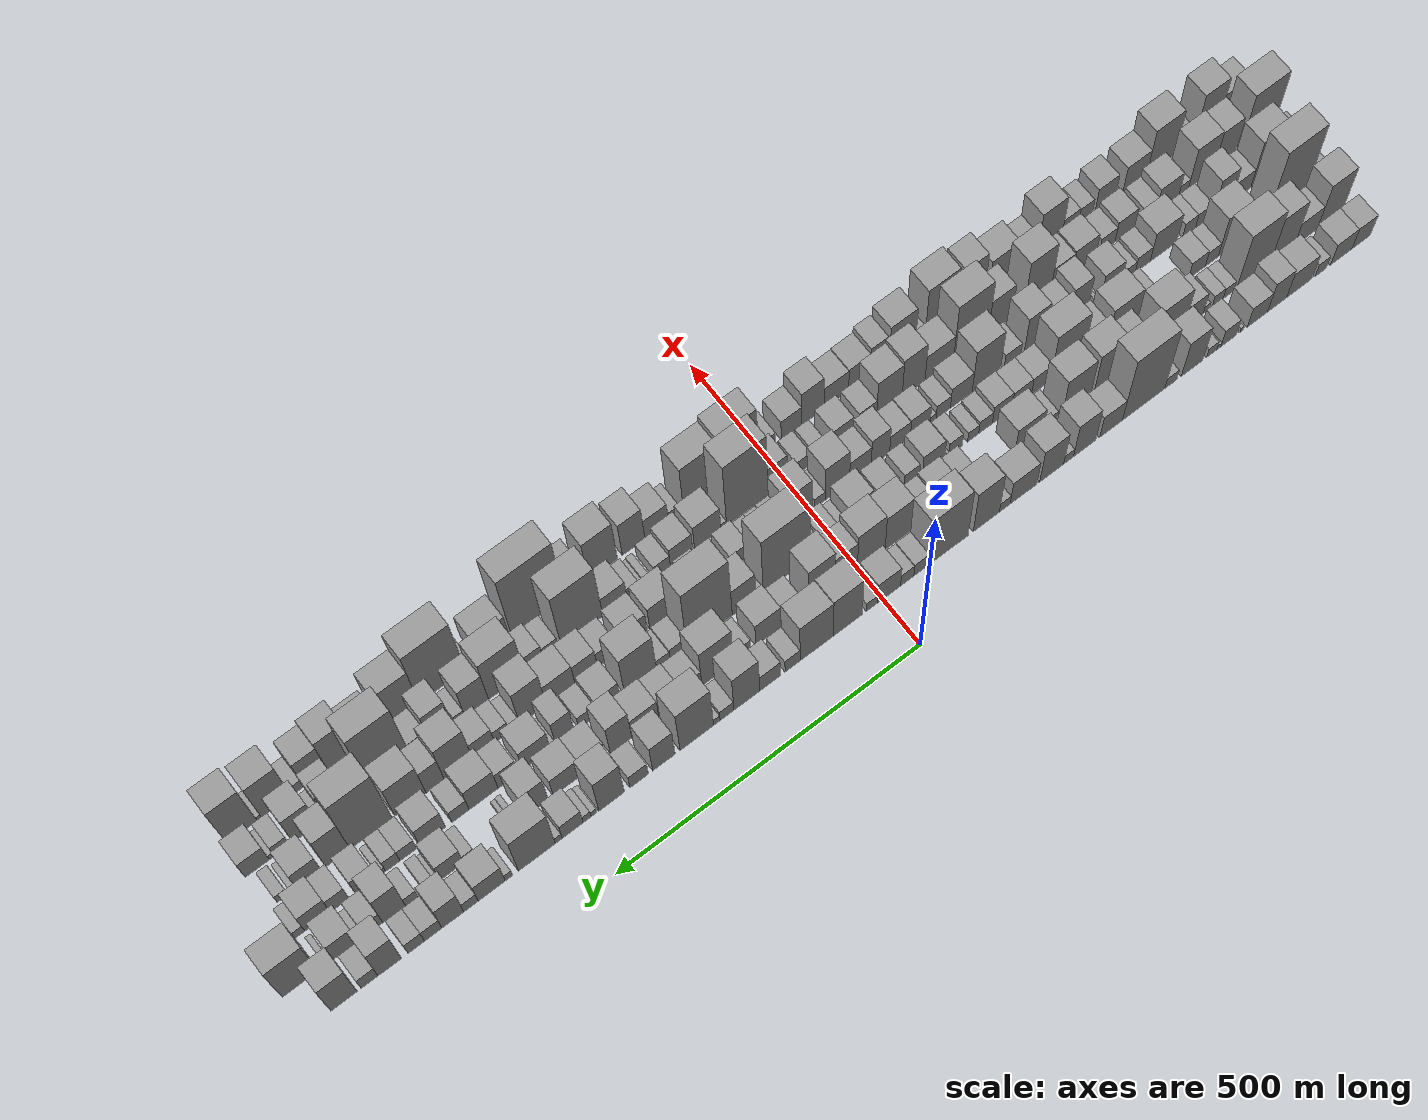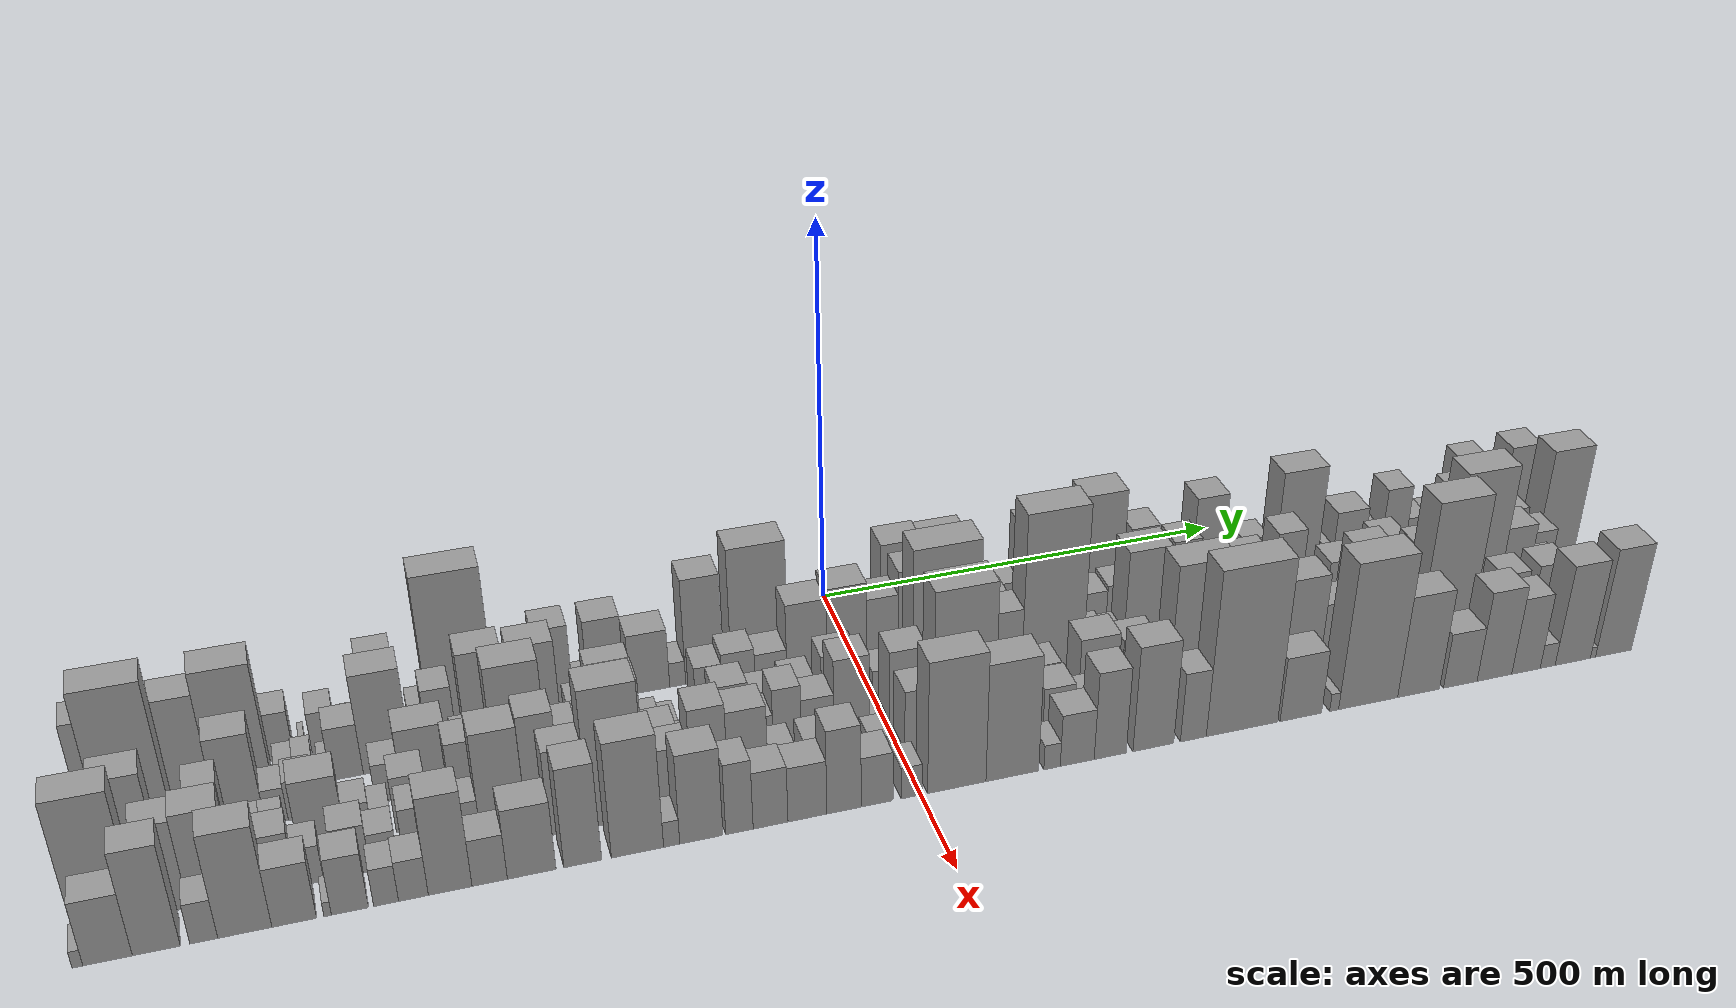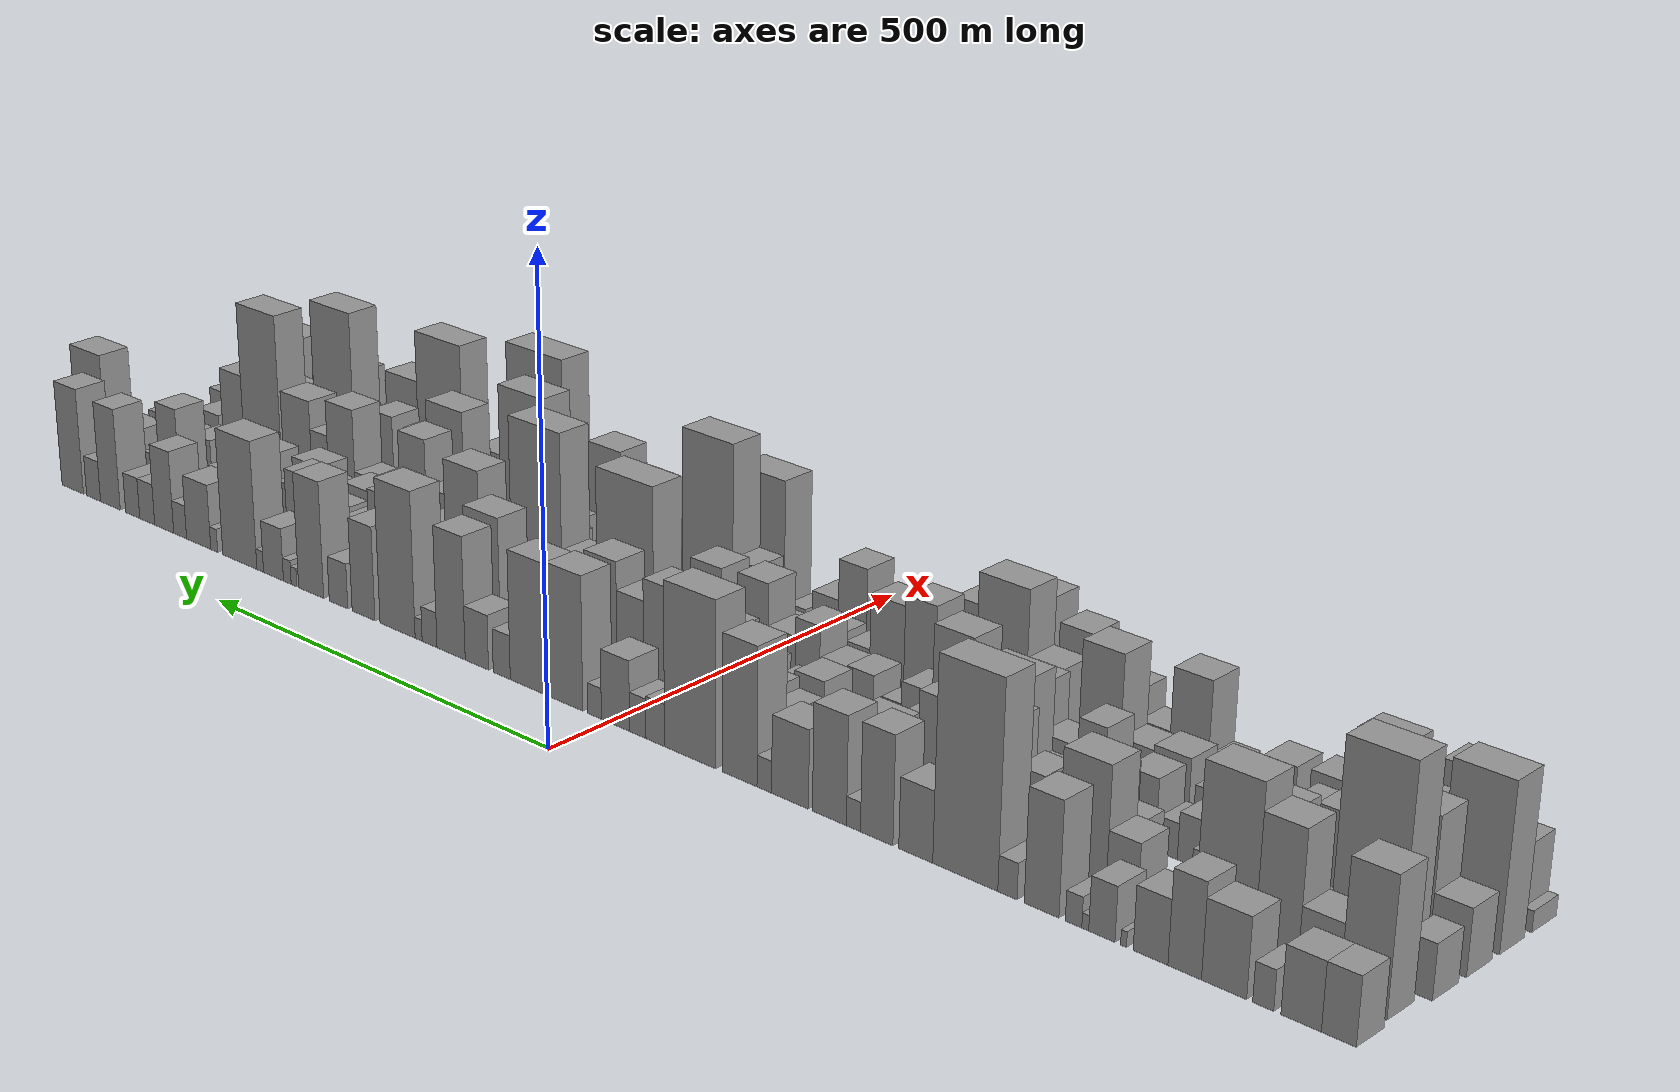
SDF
<sdf version="1.6">
 <world name="default">
  <scene>
   <sky><clouds><speed>12</speed></clouds></sky>
   <ambient>0.4 0.4 0.4 1</ambient>
   <background>0.7 0.7 0.7 1</background>
   <shadows>1</shadows>
  </scene>
  <gravity>0 0 -9.8066</gravity>
  <magnetic_field>6e-06 2.3e-05 -4.2e-05</magnetic_field>
  <physics default="0" name="default_physics" type="ode">
   <ode>
    <solver>
     <type>quick</type>
     <iters>10</iters>
     <sor>1.0</sor>
     <use_dynamic_moi_rescaling>0</use_dynamic_moi_rescaling>
    </solver>
    <constraints>
     <cfm>0</cfm>
     <erp>0.2</erp>
     <contact_max_correcting_vel>100</contact_max_correcting_vel>
     <contact_surface_layer>0.001</contact_surface_layer>
    </constraints>
   </ode>
   <max_step_size>0.004</max_step_size>
   <real_time_factor>1</real_time_factor>
   <real_time_update_rate>250</real_time_update_rate>
  </physics>
  <light name="sun" type="directional">
   <pose>0 0 10 0 0 0</pose>
   <diffuse>0.8 0.8 0.8 1</diffuse>
   <specular>0.2 0.2 0.2 1</specular>
   <attenuation>
    <range>1000</range>
    <constant>0.9</constant>
    <linear>0.01</linear>
    <quadratic>0.001</quadratic>
   </attenuation>
   <direction>-0.5 0.1 -0.9</direction>
  </light>
  <model name="building_1">
   <static>1</static>
   <pose>100.0000 -838.2706 0 0.000000 0.000000 0.000000</pose>
   <link name="link">
    <pose>0 0 33.00 0 0 0</pose>
    <collision name="collision"><geometry><box><size>40.0000 33.4589 66.0000</size></box></geometry></collision>
    <visual name="visual">
     <cast_shadows>0</cast_shadows>
     <geometry><box><size>40.0000 33.4589 66.0000</size></box></geometry>
     <material>
      <script>
       <uri>model://grey_wall/materials/scripts</uri>
       <uri>model://grey_wall/materials/textures</uri>
       <name>vrc/grey_wall</name>
      </script>
     </material>
    </visual>
   </link>
  </model>
  <model name="building_2">
   <static>1</static>
   <pose>100.0000 -801.8729 0 0.000000 0.000000 0.000000</pose>
   <link name="link">
    <pose>0 0 33.00 0 0 0</pose>
    <collision name="collision"><geometry><box><size>40.0000 39.3364 66.0000</size></box></geometry></collision>
    <visual name="visual">
     <cast_shadows>0</cast_shadows>
     <geometry><box><size>40.0000 39.3364 66.0000</size></box></geometry>
     <material>
      <script>
       <uri>model://grey_wall/materials/scripts</uri>
       <uri>model://grey_wall/materials/textures</uri>
       <name>vrc/grey_wall</name>
      </script>
     </material>
    </visual>
   </link>
  </model>
  <model name="building_3">
   <static>1</static>
   <pose>100.0000 -764.7905 0 0.000000 0.000000 0.000000</pose>
   <link name="link">
    <pose>0 0 19.50 0 0 0</pose>
    <collision name="collision"><geometry><box><size>40.0000 20.8283 39.0000</size></box></geometry></collision>
    <visual name="visual">
     <cast_shadows>0</cast_shadows>
     <geometry><box><size>40.0000 20.8283 39.0000</size></box></geometry>
     <material>
      <script>
       <uri>model://grey_wall/materials/scripts</uri>
       <uri>model://grey_wall/materials/textures</uri>
       <name>vrc/grey_wall</name>
      </script>
     </material>
    </visual>
   </link>
  </model>
  <model name="building_4">
   <static>1</static>
   <pose>100.0000 -725.6079 0 0.000000 0.000000 0.000000</pose>
   <link name="link">
    <pose>0 0 39.00 0 0 0</pose>
    <collision name="collision"><geometry><box><size>40.0000 45.5370 78.0000</size></box></geometry></collision>
    <visual name="visual">
     <cast_shadows>0</cast_shadows>
     <geometry><box><size>40.0000 45.5370 78.0000</size></box></geometry>
     <material>
      <script>
       <uri>model://grey_wall/materials/scripts</uri>
       <uri>model://grey_wall/materials/textures</uri>
       <name>vrc/grey_wall</name>
      </script>
     </material>
    </visual>
   </link>
  </model>
  <model name="building_5">
   <static>1</static>
   <pose>100.0000 -685.6051 0 0.000000 0.000000 0.000000</pose>
   <link name="link">
    <pose>0 0 46.50 0 0 0</pose>
    <collision name="collision"><geometry><box><size>40.0000 34.4686 93.0000</size></box></geometry></collision>
    <visual name="visual">
     <cast_shadows>0</cast_shadows>
     <geometry><box><size>40.0000 34.4686 93.0000</size></box></geometry>
     <material>
      <script>
       <uri>model://grey_wall/materials/scripts</uri>
       <uri>model://grey_wall/materials/textures</uri>
       <name>vrc/grey_wall</name>
      </script>
     </material>
    </visual>
   </link>
  </model>
  <model name="building_6">
   <static>1</static>
   <pose>100.0000 -650.2507 0 0.000000 0.000000 0.000000</pose>
   <link name="link">
    <pose>0 0 31.50 0 0 0</pose>
    <collision name="collision"><geometry><box><size>40.0000 36.2403 63.0000</size></box></geometry></collision>
    <visual name="visual">
     <cast_shadows>0</cast_shadows>
     <geometry><box><size>40.0000 36.2403 63.0000</size></box></geometry>
     <material>
      <script>
       <uri>model://grey_wall/materials/scripts</uri>
       <uri>model://grey_wall/materials/textures</uri>
       <name>vrc/grey_wall</name>
      </script>
     </material>
    </visual>
   </link>
  </model>
  <model name="building_7">
   <static>1</static>
   <pose>100.0000 -621.9968 0 0.000000 0.000000 0.000000</pose>
   <link name="link">
    <pose>0 0 7.50 0 0 0</pose>
    <collision name="collision"><geometry><box><size>40.0000 6.2674 15.0000</size></box></geometry></collision>
    <visual name="visual">
     <cast_shadows>0</cast_shadows>
     <geometry><box><size>40.0000 6.2674 15.0000</size></box></geometry>
     <material>
      <script>
       <uri>model://grey_wall/materials/scripts</uri>
       <uri>model://grey_wall/materials/textures</uri>
       <name>vrc/grey_wall</name>
      </script>
     </material>
    </visual>
   </link>
  </model>
  <model name="building_8">
   <static>1</static>
   <pose>100.0000 -598.8530 0 0.000000 0.000000 0.000000</pose>
   <link name="link">
    <pose>0 0 27.00 0 0 0</pose>
    <collision name="collision"><geometry><box><size>40.0000 28.0203 54.0000</size></box></geometry></collision>
    <visual name="visual">
     <cast_shadows>0</cast_shadows>
     <geometry><box><size>40.0000 28.0203 54.0000</size></box></geometry>
     <material>
      <script>
       <uri>model://grey_wall/materials/scripts</uri>
       <uri>model://grey_wall/materials/textures</uri>
       <name>vrc/grey_wall</name>
      </script>
     </material>
    </visual>
   </link>
  </model>
  <model name="building_9">
   <static>1</static>
   <pose>100.0000 -581.1232 0 0.000000 0.000000 0.000000</pose>
   <link name="link">
    <pose>0 0 7.50 0 0 0</pose>
    <collision name="collision"><geometry><box><size>40.0000 7.4392 15.0000</size></box></geometry></collision>
    <visual name="visual">
     <cast_shadows>0</cast_shadows>
     <geometry><box><size>40.0000 7.4392 15.0000</size></box></geometry>
     <material>
      <script>
       <uri>model://grey_wall/materials/scripts</uri>
       <uri>model://grey_wall/materials/textures</uri>
       <name>vrc/grey_wall</name>
      </script>
     </material>
    </visual>
   </link>
  </model>
  <model name="building_10">
   <static>1</static>
   <pose>100.0000 -568.5045 0 0.000000 0.000000 0.000000</pose>
   <link name="link">
    <pose>0 0 15.00 0 0 0</pose>
    <collision name="collision"><geometry><box><size>40.0000 17.7981 30.0000</size></box></geometry></collision>
    <visual name="visual">
     <cast_shadows>0</cast_shadows>
     <geometry><box><size>40.0000 17.7981 30.0000</size></box></geometry>
     <material>
      <script>
       <uri>model://grey_wall/materials/scripts</uri>
       <uri>model://grey_wall/materials/textures</uri>
       <name>vrc/grey_wall</name>
      </script>
     </material>
    </visual>
   </link>
  </model>
  <model name="building_11">
   <static>1</static>
   <pose>100.0000 -533.4945 0 0.000000 0.000000 0.000000</pose>
   <link name="link">
    <pose>0 0 57.00 0 0 0</pose>
    <collision name="collision"><geometry><box><size>40.0000 38.2220 114.0000</size></box></geometry></collision>
    <visual name="visual">
     <cast_shadows>0</cast_shadows>
     <geometry><box><size>40.0000 38.2220 114.0000</size></box></geometry>
     <material>
      <script>
       <uri>model://grey_wall/materials/scripts</uri>
       <uri>model://grey_wall/materials/textures</uri>
       <name>vrc/grey_wall</name>
      </script>
     </material>
    </visual>
   </link>
  </model>
  <model name="building_12">
   <static>1</static>
   <pose>100.0000 -495.6311 0 0.000000 0.000000 0.000000</pose>
   <link name="link">
    <pose>0 0 18.00 0 0 0</pose>
    <collision name="collision"><geometry><box><size>40.0000 21.5048 36.0000</size></box></geometry></collision>
    <visual name="visual">
     <cast_shadows>0</cast_shadows>
     <geometry><box><size>40.0000 21.5048 36.0000</size></box></geometry>
     <material>
      <script>
       <uri>model://grey_wall/materials/scripts</uri>
       <uri>model://grey_wall/materials/textures</uri>
       <name>vrc/grey_wall</name>
      </script>
     </material>
    </visual>
   </link>
  </model>
  <model name="building_13">
   <static>1</static>
   <pose>100.0000 -447.6939 0 0.000000 0.000000 0.000000</pose>
   <link name="link">
    <pose>0 0 103.50 0 0 0</pose>
    <collision name="collision"><geometry><box><size>40.0000 74.3696 207.0000</size></box></geometry></collision>
    <visual name="visual">
     <cast_shadows>0</cast_shadows>
     <geometry><box><size>40.0000 74.3696 207.0000</size></box></geometry>
     <material>
      <script>
       <uri>model://grey_wall/materials/scripts</uri>
       <uri>model://grey_wall/materials/textures</uri>
       <name>vrc/grey_wall</name>
      </script>
     </material>
    </visual>
   </link>
  </model>
  <model name="building_14">
   <static>1</static>
   <pose>100.0000 -390.6195 0 0.000000 0.000000 0.000000</pose>
   <link name="link">
    <pose>0 0 36.00 0 0 0</pose>
    <collision name="collision"><geometry><box><size>40.0000 39.7791 72.0000</size></box></geometry></collision>
    <visual name="visual">
     <cast_shadows>0</cast_shadows>
     <geometry><box><size>40.0000 39.7791 72.0000</size></box></geometry>
     <material>
      <script>
       <uri>model://grey_wall/materials/scripts</uri>
       <uri>model://grey_wall/materials/textures</uri>
       <name>vrc/grey_wall</name>
      </script>
     </material>
    </visual>
   </link>
  </model>
  <model name="building_15">
   <static>1</static>
   <pose>100.0000 -344.3302 0 0.000000 0.000000 0.000000</pose>
   <link name="link">
    <pose>0 0 55.50 0 0 0</pose>
    <collision name="collision"><geometry><box><size>40.0000 38.7995 111.0000</size></box></geometry></collision>
    <visual name="visual">
     <cast_shadows>0</cast_shadows>
     <geometry><box><size>40.0000 38.7995 111.0000</size></box></geometry>
     <material>
      <script>
       <uri>model://grey_wall/materials/scripts</uri>
       <uri>model://grey_wall/materials/textures</uri>
       <name>vrc/grey_wall</name>
      </script>
     </material>
    </visual>
   </link>
  </model>
  <model name="building_16">
   <static>1</static>
   <pose>100.0000 -316.4621 0 0.000000 0.000000 0.000000</pose>
   <link name="link">
    <pose>0 0 15.00 0 0 0</pose>
    <collision name="collision"><geometry><box><size>40.0000 16.9368 30.0000</size></box></geometry></collision>
    <visual name="visual">
     <cast_shadows>0</cast_shadows>
     <geometry><box><size>40.0000 16.9368 30.0000</size></box></geometry>
     <material>
      <script>
       <uri>model://grey_wall/materials/scripts</uri>
       <uri>model://grey_wall/materials/textures</uri>
       <name>vrc/grey_wall</name>
      </script>
     </material>
    </visual>
   </link>
  </model>
  <model name="building_17">
   <static>1</static>
   <pose>100.0000 -287.1883 0 0.000000 0.000000 0.000000</pose>
   <link name="link">
    <pose>0 0 55.50 0 0 0</pose>
    <collision name="collision"><geometry><box><size>40.0000 41.6107 111.0000</size></box></geometry></collision>
    <visual name="visual">
     <cast_shadows>0</cast_shadows>
     <geometry><box><size>40.0000 41.6107 111.0000</size></box></geometry>
     <material>
      <script>
       <uri>model://grey_wall/materials/scripts</uri>
       <uri>model://grey_wall/materials/textures</uri>
       <name>vrc/grey_wall</name>
      </script>
     </material>
    </visual>
   </link>
  </model>
  <model name="building_18">
   <static>1</static>
   <pose>100.0000 -238.3716 0 0.000000 0.000000 0.000000</pose>
   <link name="link">
    <pose>0 0 40.50 0 0 0</pose>
    <collision name="collision"><geometry><box><size>40.0000 46.0228 81.0000</size></box></geometry></collision>
    <visual name="visual">
     <cast_shadows>0</cast_shadows>
     <geometry><box><size>40.0000 46.0228 81.0000</size></box></geometry>
     <material>
      <script>
       <uri>model://grey_wall/materials/scripts</uri>
       <uri>model://grey_wall/materials/textures</uri>
       <name>vrc/grey_wall</name>
      </script>
     </material>
    </visual>
   </link>
  </model>
  <model name="building_19">
   <static>1</static>
   <pose>100.0000 -206.1027 0 0.000000 0.000000 0.000000</pose>
   <link name="link">
    <pose>0 0 16.50 0 0 0</pose>
    <collision name="collision"><geometry><box><size>40.0000 18.5150 33.0000</size></box></geometry></collision>
    <visual name="visual">
     <cast_shadows>0</cast_shadows>
     <geometry><box><size>40.0000 18.5150 33.0000</size></box></geometry>
     <material>
      <script>
       <uri>model://grey_wall/materials/scripts</uri>
       <uri>model://grey_wall/materials/textures</uri>
       <name>vrc/grey_wall</name>
      </script>
     </material>
    </visual>
   </link>
  </model>
  <model name="building_20">
   <static>1</static>
   <pose>100.0000 -174.6314 0 0.000000 0.000000 0.000000</pose>
   <link name="link">
    <pose>0 0 72.00 0 0 0</pose>
    <collision name="collision"><geometry><box><size>40.0000 44.4275 144.0000</size></box></geometry></collision>
    <visual name="visual">
     <cast_shadows>0</cast_shadows>
     <geometry><box><size>40.0000 44.4275 144.0000</size></box></geometry>
     <material>
      <script>
       <uri>model://grey_wall/materials/scripts</uri>
       <uri>model://grey_wall/materials/textures</uri>
       <name>vrc/grey_wall</name>
      </script>
     </material>
    </visual>
   </link>
  </model>
  <model name="building_21">
   <static>1</static>
   <pose>100.0000 -109.7464 0 0.000000 0.000000 0.000000</pose>
   <link name="link">
    <pose>0 0 87.00 0 0 0</pose>
    <collision name="collision"><geometry><box><size>40.0000 67.3426 174.0000</size></box></geometry></collision>
    <visual name="visual">
     <cast_shadows>0</cast_shadows>
     <geometry><box><size>40.0000 67.3426 174.0000</size></box></geometry>
     <material>
      <script>
       <uri>model://grey_wall/materials/scripts</uri>
       <uri>model://grey_wall/materials/textures</uri>
       <name>vrc/grey_wall</name>
      </script>
     </material>
    </visual>
   </link>
  </model>
  <model name="building_22">
   <static>1</static>
   <pose>100.0000 -63.6929 0 0.000000 0.000000 0.000000</pose>
   <link name="link">
    <pose>0 0 22.50 0 0 0</pose>
    <collision name="collision"><geometry><box><size>40.0000 24.7644 45.0000</size></box></geometry></collision>
    <visual name="visual">
     <cast_shadows>0</cast_shadows>
     <geometry><box><size>40.0000 24.7644 45.0000</size></box></geometry>
     <material>
      <script>
       <uri>model://grey_wall/materials/scripts</uri>
       <uri>model://grey_wall/materials/textures</uri>
       <name>vrc/grey_wall</name>
      </script>
     </material>
    </visual>
   </link>
  </model>
  <model name="building_23">
   <static>1</static>
   <pose>100.0000 -40.1029 0 0.000000 0.000000 0.000000</pose>
   <link name="link">
    <pose>0 0 21.00 0 0 0</pose>
    <collision name="collision"><geometry><box><size>40.0000 22.4156 42.0000</size></box></geometry></collision>
    <visual name="visual">
     <cast_shadows>0</cast_shadows>
     <geometry><box><size>40.0000 22.4156 42.0000</size></box></geometry>
     <material>
      <script>
       <uri>model://grey_wall/materials/scripts</uri>
       <uri>model://grey_wall/materials/textures</uri>
       <name>vrc/grey_wall</name>
      </script>
     </material>
    </visual>
   </link>
  </model>
  <model name="building_24">
   <static>1</static>
   <pose>100.0000 -9.5780 0 0.000000 0.000000 0.000000</pose>
   <link name="link">
    <pose>0 0 37.50 0 0 0</pose>
    <collision name="collision"><geometry><box><size>40.0000 38.6341 75.0000</size></box></geometry></collision>
    <visual name="visual">
     <cast_shadows>0</cast_shadows>
     <geometry><box><size>40.0000 38.6341 75.0000</size></box></geometry>
     <material>
      <script>
       <uri>model://grey_wall/materials/scripts</uri>
       <uri>model://grey_wall/materials/textures</uri>
       <name>vrc/grey_wall</name>
      </script>
     </material>
    </visual>
   </link>
  </model>
  <model name="building_25">
   <static>1</static>
   <pose>100.0000 19.1603 0 0.000000 0.000000 0.000000</pose>
   <link name="link">
    <pose>0 0 16.50 0 0 0</pose>
    <collision name="collision"><geometry><box><size>40.0000 18.8425 33.0000</size></box></geometry></collision>
    <visual name="visual">
     <cast_shadows>0</cast_shadows>
     <geometry><box><size>40.0000 18.8425 33.0000</size></box></geometry>
     <material>
      <script>
       <uri>model://grey_wall/materials/scripts</uri>
       <uri>model://grey_wall/materials/textures</uri>
       <name>vrc/grey_wall</name>
      </script>
     </material>
    </visual>
   </link>
  </model>
  <model name="building_26">
   <static>1</static>
   <pose>100.0000 59.8532 0 0.000000 0.000000 0.000000</pose>
   <link name="link">
    <pose>0 0 72.00 0 0 0</pose>
    <collision name="collision"><geometry><box><size>40.0000 48.5433 144.0000</size></box></geometry></collision>
    <visual name="visual">
     <cast_shadows>0</cast_shadows>
     <geometry><box><size>40.0000 48.5433 144.0000</size></box></geometry>
     <material>
      <script>
       <uri>model://grey_wall/materials/scripts</uri>
       <uri>model://grey_wall/materials/textures</uri>
       <name>vrc/grey_wall</name>
      </script>
     </material>
    </visual>
   </link>
  </model>
  <model name="building_27">
   <static>1</static>
   <pose>100.0000 111.6172 0 0.000000 0.000000 0.000000</pose>
   <link name="link">
    <pose>0 0 70.50 0 0 0</pose>
    <collision name="collision"><geometry><box><size>40.0000 54.9846 141.0000</size></box></geometry></collision>
    <visual name="visual">
     <cast_shadows>0</cast_shadows>
     <geometry><box><size>40.0000 54.9846 141.0000</size></box></geometry>
     <material>
      <script>
       <uri>model://grey_wall/materials/scripts</uri>
       <uri>model://grey_wall/materials/textures</uri>
       <name>vrc/grey_wall</name>
      </script>
     </material>
    </visual>
   </link>
  </model>
  <model name="building_28">
   <static>1</static>
   <pose>100.0000 151.5574 0 0.000000 0.000000 0.000000</pose>
   <link name="link">
    <pose>0 0 24.00 0 0 0</pose>
    <collision name="collision"><geometry><box><size>40.0000 24.8957 48.0000</size></box></geometry></collision>
    <visual name="visual">
     <cast_shadows>0</cast_shadows>
     <geometry><box><size>40.0000 24.8957 48.0000</size></box></geometry>
     <material>
      <script>
       <uri>model://grey_wall/materials/scripts</uri>
       <uri>model://grey_wall/materials/textures</uri>
       <name>vrc/grey_wall</name>
      </script>
     </material>
    </visual>
   </link>
  </model>
  <model name="building_29">
   <static>1</static>
   <pose>100.0000 188.3205 0 0.000000 0.000000 0.000000</pose>
   <link name="link">
    <pose>0 0 30.00 0 0 0</pose>
    <collision name="collision"><geometry><box><size>40.0000 34.6305 60.0000</size></box></geometry></collision>
    <visual name="visual">
     <cast_shadows>0</cast_shadows>
     <geometry><box><size>40.0000 34.6305 60.0000</size></box></geometry>
     <material>
      <script>
       <uri>model://grey_wall/materials/scripts</uri>
       <uri>model://grey_wall/materials/textures</uri>
       <name>vrc/grey_wall</name>
      </script>
     </material>
    </visual>
   </link>
  </model>
  <model name="building_30">
   <static>1</static>
   <pose>100.0000 226.8834 0 0.000000 0.000000 0.000000</pose>
   <link name="link">
    <pose>0 0 67.50 0 0 0</pose>
    <collision name="collision"><geometry><box><size>40.0000 42.4952 135.0000</size></box></geometry></collision>
    <visual name="visual">
     <cast_shadows>0</cast_shadows>
     <geometry><box><size>40.0000 42.4952 135.0000</size></box></geometry>
     <material>
      <script>
       <uri>model://grey_wall/materials/scripts</uri>
       <uri>model://grey_wall/materials/textures</uri>
       <name>vrc/grey_wall</name>
      </script>
     </material>
    </visual>
   </link>
  </model>
  <model name="building_31">
   <static>1</static>
   <pose>100.0000 259.4990 0 0.000000 0.000000 0.000000</pose>
   <link name="link">
    <pose>0 0 19.50 0 0 0</pose>
    <collision name="collision"><geometry><box><size>40.0000 22.7361 39.0000</size></box></geometry></collision>
    <visual name="visual">
     <cast_shadows>0</cast_shadows>
     <geometry><box><size>40.0000 22.7361 39.0000</size></box></geometry>
     <material>
      <script>
       <uri>model://grey_wall/materials/scripts</uri>
       <uri>model://grey_wall/materials/textures</uri>
       <name>vrc/grey_wall</name>
      </script>
     </material>
    </visual>
   </link>
  </model>
  <model name="building_32">
   <static>1</static>
   <pose>100.0000 276.2242 0 0.000000 0.000000 0.000000</pose>
   <link name="link">
    <pose>0 0 12.00 0 0 0</pose>
    <collision name="collision"><geometry><box><size>40.0000 10.7142 24.0000</size></box></geometry></collision>
    <visual name="visual">
     <cast_shadows>0</cast_shadows>
     <geometry><box><size>40.0000 10.7142 24.0000</size></box></geometry>
     <material>
      <script>
       <uri>model://grey_wall/materials/scripts</uri>
       <uri>model://grey_wall/materials/textures</uri>
       <name>vrc/grey_wall</name>
      </script>
     </material>
    </visual>
   </link>
  </model>
  <model name="building_33">
   <static>1</static>
   <pose>100.0000 308.8887 0 0.000000 0.000000 0.000000</pose>
   <link name="link">
    <pose>0 0 81.00 0 0 0</pose>
    <collision name="collision"><geometry><box><size>40.0000 54.6149 162.0000</size></box></geometry></collision>
    <visual name="visual">
     <cast_shadows>0</cast_shadows>
     <geometry><box><size>40.0000 54.6149 162.0000</size></box></geometry>
     <material>
      <script>
       <uri>model://grey_wall/materials/scripts</uri>
       <uri>model://grey_wall/materials/textures</uri>
       <name>vrc/grey_wall</name>
      </script>
     </material>
    </visual>
   </link>
  </model>
  <model name="building_34">
   <static>1</static>
   <pose>100.0000 362.2740 0 0.000000 0.000000 0.000000</pose>
   <link name="link">
    <pose>0 0 52.50 0 0 0</pose>
    <collision name="collision"><geometry><box><size>40.0000 36.1556 105.0000</size></box></geometry></collision>
    <visual name="visual">
     <cast_shadows>0</cast_shadows>
     <geometry><box><size>40.0000 36.1556 105.0000</size></box></geometry>
     <material>
      <script>
       <uri>model://grey_wall/materials/scripts</uri>
       <uri>model://grey_wall/materials/textures</uri>
       <name>vrc/grey_wall</name>
      </script>
     </material>
    </visual>
   </link>
  </model>
  <model name="building_35">
   <static>1</static>
   <pose>100.0000 402.2554 0 0.000000 0.000000 0.000000</pose>
   <link name="link">
    <pose>0 0 25.50 0 0 0</pose>
    <collision name="collision"><geometry><box><size>40.0000 29.8073 51.0000</size></box></geometry></collision>
    <visual name="visual">
     <cast_shadows>0</cast_shadows>
     <geometry><box><size>40.0000 29.8073 51.0000</size></box></geometry>
     <material>
      <script>
       <uri>model://grey_wall/materials/scripts</uri>
       <uri>model://grey_wall/materials/textures</uri>
       <name>vrc/grey_wall</name>
      </script>
     </material>
    </visual>
   </link>
  </model>
  <model name="building_36">
   <static>1</static>
   <pose>100.0000 446.6684 0 0.000000 0.000000 0.000000</pose>
   <link name="link">
    <pose>0 0 66.00 0 0 0</pose>
    <collision name="collision"><geometry><box><size>40.0000 41.0188 132.0000</size></box></geometry></collision>
    <visual name="visual">
     <cast_shadows>0</cast_shadows>
     <geometry><box><size>40.0000 41.0188 132.0000</size></box></geometry>
     <material>
      <script>
       <uri>model://grey_wall/materials/scripts</uri>
       <uri>model://grey_wall/materials/textures</uri>
       <name>vrc/grey_wall</name>
      </script>
     </material>
    </visual>
   </link>
  </model>
  <model name="building_37">
   <static>1</static>
   <pose>100.0000 474.8791 0 0.000000 0.000000 0.000000</pose>
   <link name="link">
    <pose>0 0 10.50 0 0 0</pose>
    <collision name="collision"><geometry><box><size>40.0000 9.4025 21.0000</size></box></geometry></collision>
    <visual name="visual">
     <cast_shadows>0</cast_shadows>
     <geometry><box><size>40.0000 9.4025 21.0000</size></box></geometry>
     <material>
      <script>
       <uri>model://grey_wall/materials/scripts</uri>
       <uri>model://grey_wall/materials/textures</uri>
       <name>vrc/grey_wall</name>
      </script>
     </material>
    </visual>
   </link>
  </model>
  <model name="building_38">
   <static>1</static>
   <pose>100.0000 485.9886 0 0.000000 0.000000 0.000000</pose>
   <link name="link">
    <pose>0 0 13.50 0 0 0</pose>
    <collision name="collision"><geometry><box><size>40.0000 12.8164 27.0000</size></box></geometry></collision>
    <visual name="visual">
     <cast_shadows>0</cast_shadows>
     <geometry><box><size>40.0000 12.8164 27.0000</size></box></geometry>
     <material>
      <script>
       <uri>model://grey_wall/materials/scripts</uri>
       <uri>model://grey_wall/materials/textures</uri>
       <name>vrc/grey_wall</name>
      </script>
     </material>
    </visual>
   </link>
  </model>
  <model name="building_39">
   <static>1</static>
   <pose>100.0000 509.0703 0 0.000000 0.000000 0.000000</pose>
   <link name="link">
    <pose>0 0 30.00 0 0 0</pose>
    <collision name="collision"><geometry><box><size>40.0000 33.3469 60.0000</size></box></geometry></collision>
    <visual name="visual">
     <cast_shadows>0</cast_shadows>
     <geometry><box><size>40.0000 33.3469 60.0000</size></box></geometry>
     <material>
      <script>
       <uri>model://grey_wall/materials/scripts</uri>
       <uri>model://grey_wall/materials/textures</uri>
       <name>vrc/grey_wall</name>
      </script>
     </material>
    </visual>
   </link>
  </model>
  <model name="building_40">
   <static>1</static>
   <pose>100.0000 531.3404 0 0.000000 0.000000 0.000000</pose>
   <link name="link">
    <pose>0 0 12.00 0 0 0</pose>
    <collision name="collision"><geometry><box><size>40.0000 11.1934 24.0000</size></box></geometry></collision>
    <visual name="visual">
     <cast_shadows>0</cast_shadows>
     <geometry><box><size>40.0000 11.1934 24.0000</size></box></geometry>
     <material>
      <script>
       <uri>model://grey_wall/materials/scripts</uri>
       <uri>model://grey_wall/materials/textures</uri>
       <name>vrc/grey_wall</name>
      </script>
     </material>
    </visual>
   </link>
  </model>
  <model name="building_41">
   <static>1</static>
   <pose>100.0000 566.0757 0 0.000000 0.000000 0.000000</pose>
   <link name="link">
    <pose>0 0 73.50 0 0 0</pose>
    <collision name="collision"><geometry><box><size>40.0000 58.2772 147.0000</size></box></geometry></collision>
    <visual name="visual">
     <cast_shadows>0</cast_shadows>
     <geometry><box><size>40.0000 58.2772 147.0000</size></box></geometry>
     <material>
      <script>
       <uri>model://grey_wall/materials/scripts</uri>
       <uri>model://grey_wall/materials/textures</uri>
       <name>vrc/grey_wall</name>
      </script>
     </material>
    </visual>
   </link>
  </model>
  <model name="building_42">
   <static>1</static>
   <pose>100.0000 610.1692 0 0.000000 0.000000 0.000000</pose>
   <link name="link">
    <pose>0 0 13.50 0 0 0</pose>
    <collision name="collision"><geometry><box><size>40.0000 11.9098 27.0000</size></box></geometry></collision>
    <visual name="visual">
     <cast_shadows>0</cast_shadows>
     <geometry><box><size>40.0000 11.9098 27.0000</size></box></geometry>
     <material>
      <script>
       <uri>model://grey_wall/materials/scripts</uri>
       <uri>model://grey_wall/materials/textures</uri>
       <name>vrc/grey_wall</name>
      </script>
     </material>
    </visual>
   </link>
  </model>
  <model name="building_43">
   <static>1</static>
   <pose>100.0000 637.3659 0 0.000000 0.000000 0.000000</pose>
   <link name="link">
    <pose>0 0 37.50 0 0 0</pose>
    <collision name="collision"><geometry><box><size>40.0000 42.4835 75.0000</size></box></geometry></collision>
    <visual name="visual">
     <cast_shadows>0</cast_shadows>
     <geometry><box><size>40.0000 42.4835 75.0000</size></box></geometry>
     <material>
      <script>
       <uri>model://grey_wall/materials/scripts</uri>
       <uri>model://grey_wall/materials/textures</uri>
       <name>vrc/grey_wall</name>
      </script>
     </material>
    </visual>
   </link>
  </model>
  <model name="building_44">
   <static>1</static>
   <pose>100.0000 669.9970 0 0.000000 0.000000 0.000000</pose>
   <link name="link">
    <pose>0 0 19.50 0 0 0</pose>
    <collision name="collision"><geometry><box><size>40.0000 22.7788 39.0000</size></box></geometry></collision>
    <visual name="visual">
     <cast_shadows>0</cast_shadows>
     <geometry><box><size>40.0000 22.7788 39.0000</size></box></geometry>
     <material>
      <script>
       <uri>model://grey_wall/materials/scripts</uri>
       <uri>model://grey_wall/materials/textures</uri>
       <name>vrc/grey_wall</name>
      </script>
     </material>
    </visual>
   </link>
  </model>
  <model name="building_45">
   <static>1</static>
   <pose>100.0000 698.4218 0 0.000000 0.000000 0.000000</pose>
   <link name="link">
    <pose>0 0 48.00 0 0 0</pose>
    <collision name="collision"><geometry><box><size>40.0000 34.0707 96.0000</size></box></geometry></collision>
    <visual name="visual">
     <cast_shadows>0</cast_shadows>
     <geometry><box><size>40.0000 34.0707 96.0000</size></box></geometry>
     <material>
      <script>
       <uri>model://grey_wall/materials/scripts</uri>
       <uri>model://grey_wall/materials/textures</uri>
       <name>vrc/grey_wall</name>
      </script>
     </material>
    </visual>
   </link>
  </model>
  <model name="building_46">
   <static>1</static>
   <pose>100.0000 729.0111 0 0.000000 0.000000 0.000000</pose>
   <link name="link">
    <pose>0 0 24.00 0 0 0</pose>
    <collision name="collision"><geometry><box><size>40.0000 27.1078 48.0000</size></box></geometry></collision>
    <visual name="visual">
     <cast_shadows>0</cast_shadows>
     <geometry><box><size>40.0000 27.1078 48.0000</size></box></geometry>
     <material>
      <script>
       <uri>model://grey_wall/materials/scripts</uri>
       <uri>model://grey_wall/materials/textures</uri>
       <name>vrc/grey_wall</name>
      </script>
     </material>
    </visual>
   </link>
  </model>
  <model name="building_47">
   <static>1</static>
   <pose>100.0000 755.4029 0 0.000000 0.000000 0.000000</pose>
   <link name="link">
    <pose>0 0 24.00 0 0 0</pose>
    <collision name="collision"><geometry><box><size>40.0000 25.6758 48.0000</size></box></geometry></collision>
    <visual name="visual">
     <cast_shadows>0</cast_shadows>
     <geometry><box><size>40.0000 25.6758 48.0000</size></box></geometry>
     <material>
      <script>
       <uri>model://grey_wall/materials/scripts</uri>
       <uri>model://grey_wall/materials/textures</uri>
       <name>vrc/grey_wall</name>
      </script>
     </material>
    </visual>
   </link>
  </model>
  <model name="building_48">
   <static>1</static>
   <pose>100.0000 796.5270 0 0.000000 0.000000 0.000000</pose>
   <link name="link">
    <pose>0 0 60.00 0 0 0</pose>
    <collision name="collision"><geometry><box><size>40.0000 36.5725 120.0000</size></box></geometry></collision>
    <visual name="visual">
     <cast_shadows>0</cast_shadows>
     <geometry><box><size>40.0000 36.5725 120.0000</size></box></geometry>
     <material>
      <script>
       <uri>model://grey_wall/materials/scripts</uri>
       <uri>model://grey_wall/materials/textures</uri>
       <name>vrc/grey_wall</name>
      </script>
     </material>
    </visual>
   </link>
  </model>
  <model name="building_49">
   <static>1</static>
   <pose>100.0000 827.8060 0 0.000000 0.000000 0.000000</pose>
   <link name="link">
    <pose>0 0 24.00 0 0 0</pose>
    <collision name="collision"><geometry><box><size>40.0000 25.9855 48.0000</size></box></geometry></collision>
    <visual name="visual">
     <cast_shadows>0</cast_shadows>
     <geometry><box><size>40.0000 25.9855 48.0000</size></box></geometry>
     <material>
      <script>
       <uri>model://grey_wall/materials/scripts</uri>
       <uri>model://grey_wall/materials/textures</uri>
       <name>vrc/grey_wall</name>
      </script>
     </material>
    </visual>
   </link>
  </model>
  <model name="building_50">
   <static>1</static>
   <pose>100.0000 867.0473 0 0.000000 0.000000 0.000000</pose>
   <link name="link">
    <pose>0 0 63.00 0 0 0</pose>
    <collision name="collision"><geometry><box><size>40.0000 40.4972 126.0000</size></box></geometry></collision>
    <visual name="visual">
     <cast_shadows>0</cast_shadows>
     <geometry><box><size>40.0000 40.4972 126.0000</size></box></geometry>
     <material>
      <script>
       <uri>model://grey_wall/materials/scripts</uri>
       <uri>model://grey_wall/materials/textures</uri>
       <name>vrc/grey_wall</name>
      </script>
     </material>
    </visual>
   </link>
  </model>
  <model name="building_51">
   <static>1</static>
   <pose>152.0000 -826.8438 0 0.000000 0.000000 0.000000</pose>
   <link name="link">
    <pose>0 0 67.50 0 0 0</pose>
    <collision name="collision"><geometry><box><size>40.0000 46.3125 135.0000</size></box></geometry></collision>
    <visual name="visual">
     <cast_shadows>0</cast_shadows>
     <geometry><box><size>40.0000 46.3125 135.0000</size></box></geometry>
     <material>
      <script>
       <uri>model://grey_wall/materials/scripts</uri>
       <uri>model://grey_wall/materials/textures</uri>
       <name>vrc/grey_wall</name>
      </script>
     </material>
    </visual>
   </link>
  </model>
  <model name="building_52">
   <static>1</static>
   <pose>152.0000 -782.7154 0 0.000000 0.000000 0.000000</pose>
   <link name="link">
    <pose>0 0 36.00 0 0 0</pose>
    <collision name="collision"><geometry><box><size>40.0000 41.9442 72.0000</size></box></geometry></collision>
    <visual name="visual">
     <cast_shadows>0</cast_shadows>
     <geometry><box><size>40.0000 41.9442 72.0000</size></box></geometry>
     <material>
      <script>
       <uri>model://grey_wall/materials/scripts</uri>
       <uri>model://grey_wall/materials/textures</uri>
       <name>vrc/grey_wall</name>
      </script>
     </material>
    </visual>
   </link>
  </model>
  <model name="building_53">
   <static>1</static>
   <pose>152.0000 -739.8804 0 0.000000 0.000000 0.000000</pose>
   <link name="link">
    <pose>0 0 72.00 0 0 0</pose>
    <collision name="collision"><geometry><box><size>40.0000 43.7260 144.0000</size></box></geometry></collision>
    <visual name="visual">
     <cast_shadows>0</cast_shadows>
     <geometry><box><size>40.0000 43.7260 144.0000</size></box></geometry>
     <material>
      <script>
       <uri>model://grey_wall/materials/scripts</uri>
       <uri>model://grey_wall/materials/textures</uri>
       <name>vrc/grey_wall</name>
      </script>
     </material>
    </visual>
   </link>
  </model>
  <model name="building_54">
   <static>1</static>
   <pose>152.0000 -687.4164 0 0.000000 0.000000 0.000000</pose>
   <link name="link">
    <pose>0 0 85.50 0 0 0</pose>
    <collision name="collision"><geometry><box><size>40.0000 61.2020 171.0000</size></box></geometry></collision>
    <visual name="visual">
     <cast_shadows>0</cast_shadows>
     <geometry><box><size>40.0000 61.2020 171.0000</size></box></geometry>
     <material>
      <script>
       <uri>model://grey_wall/materials/scripts</uri>
       <uri>model://grey_wall/materials/textures</uri>
       <name>vrc/grey_wall</name>
      </script>
     </material>
    </visual>
   </link>
  </model>
  <model name="building_55">
   <static>1</static>
   <pose>152.0000 -643.0392 0 0.000000 0.000000 0.000000</pose>
   <link name="link">
    <pose>0 0 16.50 0 0 0</pose>
    <collision name="collision"><geometry><box><size>40.0000 19.5524 33.0000</size></box></geometry></collision>
    <visual name="visual">
     <cast_shadows>0</cast_shadows>
     <geometry><box><size>40.0000 19.5524 33.0000</size></box></geometry>
     <material>
      <script>
       <uri>model://grey_wall/materials/scripts</uri>
       <uri>model://grey_wall/materials/textures</uri>
       <name>vrc/grey_wall</name>
      </script>
     </material>
    </visual>
   </link>
  </model>
  <model name="building_56">
   <static>1</static>
   <pose>152.0000 -623.2239 0 0.000000 0.000000 0.000000</pose>
   <link name="link">
    <pose>0 0 18.00 0 0 0</pose>
    <collision name="collision"><geometry><box><size>40.0000 20.0781 36.0000</size></box></geometry></collision>
    <visual name="visual">
     <cast_shadows>0</cast_shadows>
     <geometry><box><size>40.0000 20.0781 36.0000</size></box></geometry>
     <material>
      <script>
       <uri>model://grey_wall/materials/scripts</uri>
       <uri>model://grey_wall/materials/textures</uri>
       <name>vrc/grey_wall</name>
      </script>
     </material>
    </visual>
   </link>
  </model>
  <model name="building_57">
   <static>1</static>
   <pose>152.0000 -602.8042 0 0.000000 0.000000 0.000000</pose>
   <link name="link">
    <pose>0 0 12.00 0 0 0</pose>
    <collision name="collision"><geometry><box><size>40.0000 10.7614 24.0000</size></box></geometry></collision>
    <visual name="visual">
     <cast_shadows>0</cast_shadows>
     <geometry><box><size>40.0000 10.7614 24.0000</size></box></geometry>
     <material>
      <script>
       <uri>model://grey_wall/materials/scripts</uri>
       <uri>model://grey_wall/materials/textures</uri>
       <name>vrc/grey_wall</name>
      </script>
     </material>
    </visual>
   </link>
  </model>
  <model name="building_58">
   <static>1</static>
   <pose>152.0000 -580.1652 0 0.000000 0.000000 0.000000</pose>
   <link name="link">
    <pose>0 0 34.50 0 0 0</pose>
    <collision name="collision"><geometry><box><size>40.0000 34.5166 69.0000</size></box></geometry></collision>
    <visual name="visual">
     <cast_shadows>0</cast_shadows>
     <geometry><box><size>40.0000 34.5166 69.0000</size></box></geometry>
     <material>
      <script>
       <uri>model://grey_wall/materials/scripts</uri>
       <uri>model://grey_wall/materials/textures</uri>
       <name>vrc/grey_wall</name>
      </script>
     </material>
    </visual>
   </link>
  </model>
  <model name="building_59">
   <static>1</static>
   <pose>152.0000 -536.6272 0 0.000000 0.000000 0.000000</pose>
   <link name="link">
    <pose>0 0 66.00 0 0 0</pose>
    <collision name="collision"><geometry><box><size>40.0000 52.5594 132.0000</size></box></geometry></collision>
    <visual name="visual">
     <cast_shadows>0</cast_shadows>
     <geometry><box><size>40.0000 52.5594 132.0000</size></box></geometry>
     <material>
      <script>
       <uri>model://grey_wall/materials/scripts</uri>
       <uri>model://grey_wall/materials/textures</uri>
       <name>vrc/grey_wall</name>
      </script>
     </material>
    </visual>
   </link>
  </model>
  <model name="building_60">
   <static>1</static>
   <pose>152.0000 -501.2049 0 0.000000 0.000000 0.000000</pose>
   <link name="link">
    <pose>0 0 18.00 0 0 0</pose>
    <collision name="collision"><geometry><box><size>40.0000 18.2852 36.0000</size></box></geometry></collision>
    <visual name="visual">
     <cast_shadows>0</cast_shadows>
     <geometry><box><size>40.0000 18.2852 36.0000</size></box></geometry>
     <material>
      <script>
       <uri>model://grey_wall/materials/scripts</uri>
       <uri>model://grey_wall/materials/textures</uri>
       <name>vrc/grey_wall</name>
      </script>
     </material>
    </visual>
   </link>
  </model>
  <model name="building_61">
   <static>1</static>
   <pose>152.0000 -476.0981 0 0.000000 0.000000 0.000000</pose>
   <link name="link">
    <pose>0 0 48.00 0 0 0</pose>
    <collision name="collision"><geometry><box><size>40.0000 31.9284 96.0000</size></box></geometry></collision>
    <visual name="visual">
     <cast_shadows>0</cast_shadows>
     <geometry><box><size>40.0000 31.9284 96.0000</size></box></geometry>
     <material>
      <script>
       <uri>model://grey_wall/materials/scripts</uri>
       <uri>model://grey_wall/materials/textures</uri>
       <name>vrc/grey_wall</name>
      </script>
     </material>
    </visual>
   </link>
  </model>
  <model name="building_62">
   <static>1</static>
   <pose>152.0000 -426.9603 0 0.000000 0.000000 0.000000</pose>
   <link name="link">
    <pose>0 0 67.50 0 0 0</pose>
    <collision name="collision"><geometry><box><size>40.0000 48.3472 135.0000</size></box></geometry></collision>
    <visual name="visual">
     <cast_shadows>0</cast_shadows>
     <geometry><box><size>40.0000 48.3472 135.0000</size></box></geometry>
     <material>
      <script>
       <uri>model://grey_wall/materials/scripts</uri>
       <uri>model://grey_wall/materials/textures</uri>
       <name>vrc/grey_wall</name>
      </script>
     </material>
    </visual>
   </link>
  </model>
  <model name="building_63">
   <static>1</static>
   <pose>152.0000 -371.8332 0 0.000000 0.000000 0.000000</pose>
   <link name="link">
    <pose>0 0 66.00 0 0 0</pose>
    <collision name="collision"><geometry><box><size>40.0000 49.9071 132.0000</size></box></geometry></collision>
    <visual name="visual">
     <cast_shadows>0</cast_shadows>
     <geometry><box><size>40.0000 49.9071 132.0000</size></box></geometry>
     <material>
      <script>
       <uri>model://grey_wall/materials/scripts</uri>
       <uri>model://grey_wall/materials/textures</uri>
       <name>vrc/grey_wall</name>
      </script>
     </material>
    </visual>
   </link>
  </model>
  <model name="building_64">
   <static>1</static>
   <pose>152.0000 -326.9724 0 0.000000 0.000000 0.000000</pose>
   <link name="link">
    <pose>0 0 21.00 0 0 0</pose>
    <collision name="collision"><geometry><box><size>40.0000 23.8145 42.0000</size></box></geometry></collision>
    <visual name="visual">
     <cast_shadows>0</cast_shadows>
     <geometry><box><size>40.0000 23.8145 42.0000</size></box></geometry>
     <material>
      <script>
       <uri>model://grey_wall/materials/scripts</uri>
       <uri>model://grey_wall/materials/textures</uri>
       <name>vrc/grey_wall</name>
      </script>
     </material>
    </visual>
   </link>
  </model>
  <model name="building_65">
   <static>1</static>
   <pose>152.0000 -290.4627 0 0.000000 0.000000 0.000000</pose>
   <link name="link">
    <pose>0 0 42.00 0 0 0</pose>
    <collision name="collision"><geometry><box><size>40.0000 49.2048 84.0000</size></box></geometry></collision>
    <visual name="visual">
     <cast_shadows>0</cast_shadows>
     <geometry><box><size>40.0000 49.2048 84.0000</size></box></geometry>
     <material>
      <script>
       <uri>model://grey_wall/materials/scripts</uri>
       <uri>model://grey_wall/materials/textures</uri>
       <name>vrc/grey_wall</name>
      </script>
     </material>
    </visual>
   </link>
  </model>
  <model name="building_66">
   <static>1</static>
   <pose>152.0000 -181.2605 0 0.000000 0.000000 0.000000</pose>
   <link name="link">
    <pose>0 0 30.00 0 0 0</pose>
    <collision name="collision"><geometry><box><size>40.0000 31.0666 60.0000</size></box></geometry></collision>
    <visual name="visual">
     <cast_shadows>0</cast_shadows>
     <geometry><box><size>40.0000 31.0666 60.0000</size></box></geometry>
     <material>
      <script>
       <uri>model://grey_wall/materials/scripts</uri>
       <uri>model://grey_wall/materials/textures</uri>
       <name>vrc/grey_wall</name>
      </script>
     </material>
    </visual>
   </link>
  </model>
  <model name="building_67">
   <static>1</static>
   <pose>152.0000 -146.7193 0 0.000000 0.000000 0.000000</pose>
   <link name="link">
    <pose>0 0 36.00 0 0 0</pose>
    <collision name="collision"><geometry><box><size>40.0000 38.0157 72.0000</size></box></geometry></collision>
    <visual name="visual">
     <cast_shadows>0</cast_shadows>
     <geometry><box><size>40.0000 38.0157 72.0000</size></box></geometry>
     <material>
      <script>
       <uri>model://grey_wall/materials/scripts</uri>
       <uri>model://grey_wall/materials/textures</uri>
       <name>vrc/grey_wall</name>
      </script>
     </material>
    </visual>
   </link>
  </model>
  <model name="building_68">
   <static>1</static>
   <pose>152.0000 -109.2547 0 0.000000 0.000000 0.000000</pose>
   <link name="link">
    <pose>0 0 31.50 0 0 0</pose>
    <collision name="collision"><geometry><box><size>40.0000 36.9136 63.0000</size></box></geometry></collision>
    <visual name="visual">
     <cast_shadows>0</cast_shadows>
     <geometry><box><size>40.0000 36.9136 63.0000</size></box></geometry>
     <material>
      <script>
       <uri>model://grey_wall/materials/scripts</uri>
       <uri>model://grey_wall/materials/textures</uri>
       <name>vrc/grey_wall</name>
      </script>
     </material>
    </visual>
   </link>
  </model>
  <model name="building_69">
   <static>1</static>
   <pose>152.0000 -67.3861 0 0.000000 0.000000 0.000000</pose>
   <link name="link">
    <pose>0 0 61.50 0 0 0</pose>
    <collision name="collision"><geometry><box><size>40.0000 46.8236 123.0000</size></box></geometry></collision>
    <visual name="visual">
     <cast_shadows>0</cast_shadows>
     <geometry><box><size>40.0000 46.8236 123.0000</size></box></geometry>
     <material>
      <script>
       <uri>model://grey_wall/materials/scripts</uri>
       <uri>model://grey_wall/materials/textures</uri>
       <name>vrc/grey_wall</name>
      </script>
     </material>
    </visual>
   </link>
  </model>
  <model name="building_70">
   <static>1</static>
   <pose>152.0000 -20.4230 0 0.000000 0.000000 0.000000</pose>
   <link name="link">
    <pose>0 0 67.50 0 0 0</pose>
    <collision name="collision"><geometry><box><size>40.0000 47.1026 135.0000</size></box></geometry></collision>
    <visual name="visual">
     <cast_shadows>0</cast_shadows>
     <geometry><box><size>40.0000 47.1026 135.0000</size></box></geometry>
     <material>
      <script>
       <uri>model://grey_wall/materials/scripts</uri>
       <uri>model://grey_wall/materials/textures</uri>
       <name>vrc/grey_wall</name>
      </script>
     </material>
    </visual>
   </link>
  </model>
  <model name="building_71">
   <static>1</static>
   <pose>152.0000 21.6704 0 0.000000 0.000000 0.000000</pose>
   <link name="link">
    <pose>0 0 55.50 0 0 0</pose>
    <collision name="collision"><geometry><box><size>40.0000 37.0842 111.0000</size></box></geometry></collision>
    <visual name="visual">
     <cast_shadows>0</cast_shadows>
     <geometry><box><size>40.0000 37.0842 111.0000</size></box></geometry>
     <material>
      <script>
       <uri>model://grey_wall/materials/scripts</uri>
       <uri>model://grey_wall/materials/textures</uri>
       <name>vrc/grey_wall</name>
      </script>
     </material>
    </visual>
   </link>
  </model>
  <model name="building_72">
   <static>1</static>
   <pose>152.0000 62.4371 0 0.000000 0.000000 0.000000</pose>
   <link name="link">
    <pose>0 0 70.50 0 0 0</pose>
    <collision name="collision"><geometry><box><size>40.0000 44.4492 141.0000</size></box></geometry></collision>
    <visual name="visual">
     <cast_shadows>0</cast_shadows>
     <geometry><box><size>40.0000 44.4492 141.0000</size></box></geometry>
     <material>
      <script>
       <uri>model://grey_wall/materials/scripts</uri>
       <uri>model://grey_wall/materials/textures</uri>
       <name>vrc/grey_wall</name>
      </script>
     </material>
    </visual>
   </link>
  </model>
  <model name="building_73">
   <static>1</static>
   <pose>152.0000 109.7994 0 0.000000 0.000000 0.000000</pose>
   <link name="link">
    <pose>0 0 28.50 0 0 0</pose>
    <collision name="collision"><geometry><box><size>40.0000 30.2754 57.0000</size></box></geometry></collision>
    <visual name="visual">
     <cast_shadows>0</cast_shadows>
     <geometry><box><size>40.0000 30.2754 57.0000</size></box></geometry>
     <material>
      <script>
       <uri>model://grey_wall/materials/scripts</uri>
       <uri>model://grey_wall/materials/textures</uri>
       <name>vrc/grey_wall</name>
      </script>
     </material>
    </visual>
   </link>
  </model>
  <model name="building_74">
   <static>1</static>
   <pose>152.0000 151.1428 0 0.000000 0.000000 0.000000</pose>
   <link name="link">
    <pose>0 0 42.00 0 0 0</pose>
    <collision name="collision"><geometry><box><size>40.0000 42.4115 84.0000</size></box></geometry></collision>
    <visual name="visual">
     <cast_shadows>0</cast_shadows>
     <geometry><box><size>40.0000 42.4115 84.0000</size></box></geometry>
     <material>
      <script>
       <uri>model://grey_wall/materials/scripts</uri>
       <uri>model://grey_wall/materials/textures</uri>
       <name>vrc/grey_wall</name>
      </script>
     </material>
    </visual>
   </link>
  </model>
  <model name="building_75">
   <static>1</static>
   <pose>152.0000 192.7440 0 0.000000 0.000000 0.000000</pose>
   <link name="link">
    <pose>0 0 21.00 0 0 0</pose>
    <collision name="collision"><geometry><box><size>40.0000 24.7909 42.0000</size></box></geometry></collision>
    <visual name="visual">
     <cast_shadows>0</cast_shadows>
     <geometry><box><size>40.0000 24.7909 42.0000</size></box></geometry>
     <material>
      <script>
       <uri>model://grey_wall/materials/scripts</uri>
       <uri>model://grey_wall/materials/textures</uri>
       <name>vrc/grey_wall</name>
      </script>
     </material>
    </visual>
   </link>
  </model>
  <model name="building_76">
   <static>1</static>
   <pose>152.0000 235.0382 0 0.000000 0.000000 0.000000</pose>
   <link name="link">
    <pose>0 0 69.00 0 0 0</pose>
    <collision name="collision"><geometry><box><size>40.0000 51.7974 138.0000</size></box></geometry></collision>
    <visual name="visual">
     <cast_shadows>0</cast_shadows>
     <geometry><box><size>40.0000 51.7974 138.0000</size></box></geometry>
     <material>
      <script>
       <uri>model://grey_wall/materials/scripts</uri>
       <uri>model://grey_wall/materials/textures</uri>
       <name>vrc/grey_wall</name>
      </script>
     </material>
    </visual>
   </link>
  </model>
  <model name="building_77">
   <static>1</static>
   <pose>152.0000 277.9632 0 0.000000 0.000000 0.000000</pose>
   <link name="link">
    <pose>0 0 31.50 0 0 0</pose>
    <collision name="collision"><geometry><box><size>40.0000 34.0527 63.0000</size></box></geometry></collision>
    <visual name="visual">
     <cast_shadows>0</cast_shadows>
     <geometry><box><size>40.0000 34.0527 63.0000</size></box></geometry>
     <material>
      <script>
       <uri>model://grey_wall/materials/scripts</uri>
       <uri>model://grey_wall/materials/textures</uri>
       <name>vrc/grey_wall</name>
      </script>
     </material>
    </visual>
   </link>
  </model>
  <model name="building_78">
   <static>1</static>
   <pose>152.0000 313.0679 0 0.000000 0.000000 0.000000</pose>
   <link name="link">
    <pose>0 0 34.50 0 0 0</pose>
    <collision name="collision"><geometry><box><size>40.0000 36.1565 69.0000</size></box></geometry></collision>
    <visual name="visual">
     <cast_shadows>0</cast_shadows>
     <geometry><box><size>40.0000 36.1565 69.0000</size></box></geometry>
     <material>
      <script>
       <uri>model://grey_wall/materials/scripts</uri>
       <uri>model://grey_wall/materials/textures</uri>
       <name>vrc/grey_wall</name>
      </script>
     </material>
    </visual>
   </link>
  </model>
  <model name="building_79">
   <static>1</static>
   <pose>152.0000 353.2291 0 0.000000 0.000000 0.000000</pose>
   <link name="link">
    <pose>0 0 37.50 0 0 0</pose>
    <collision name="collision"><geometry><box><size>40.0000 44.1659 75.0000</size></box></geometry></collision>
    <visual name="visual">
     <cast_shadows>0</cast_shadows>
     <geometry><box><size>40.0000 44.1659 75.0000</size></box></geometry>
     <material>
      <script>
       <uri>model://grey_wall/materials/scripts</uri>
       <uri>model://grey_wall/materials/textures</uri>
       <name>vrc/grey_wall</name>
      </script>
     </material>
    </visual>
   </link>
  </model>
  <model name="building_80">
   <static>1</static>
   <pose>152.0000 392.7489 0 0.000000 0.000000 0.000000</pose>
   <link name="link">
    <pose>0 0 57.00 0 0 0</pose>
    <collision name="collision"><geometry><box><size>40.0000 34.8737 114.0000</size></box></geometry></collision>
    <visual name="visual">
     <cast_shadows>0</cast_shadows>
     <geometry><box><size>40.0000 34.8737 114.0000</size></box></geometry>
     <material>
      <script>
       <uri>model://grey_wall/materials/scripts</uri>
       <uri>model://grey_wall/materials/textures</uri>
       <name>vrc/grey_wall</name>
      </script>
     </material>
    </visual>
   </link>
  </model>
  <model name="building_81">
   <static>1</static>
   <pose>152.0000 437.3306 0 0.000000 0.000000 0.000000</pose>
   <link name="link">
    <pose>0 0 34.50 0 0 0</pose>
    <collision name="collision"><geometry><box><size>40.0000 40.2897 69.0000</size></box></geometry></collision>
    <visual name="visual">
     <cast_shadows>0</cast_shadows>
     <geometry><box><size>40.0000 40.2897 69.0000</size></box></geometry>
     <material>
      <script>
       <uri>model://grey_wall/materials/scripts</uri>
       <uri>model://grey_wall/materials/textures</uri>
       <name>vrc/grey_wall</name>
      </script>
     </material>
    </visual>
   </link>
  </model>
  <model name="building_82">
   <static>1</static>
   <pose>152.0000 479.6560 0 0.000000 0.000000 0.000000</pose>
   <link name="link">
    <pose>0 0 37.50 0 0 0</pose>
    <collision name="collision"><geometry><box><size>40.0000 44.3611 75.0000</size></box></geometry></collision>
    <visual name="visual">
     <cast_shadows>0</cast_shadows>
     <geometry><box><size>40.0000 44.3611 75.0000</size></box></geometry>
     <material>
      <script>
       <uri>model://grey_wall/materials/scripts</uri>
       <uri>model://grey_wall/materials/textures</uri>
       <name>vrc/grey_wall</name>
      </script>
     </material>
    </visual>
   </link>
  </model>
  <model name="building_83">
   <static>1</static>
   <pose>152.0000 528.4783 0 0.000000 0.000000 0.000000</pose>
   <link name="link">
    <pose>0 0 49.50 0 0 0</pose>
    <collision name="collision"><geometry><box><size>40.0000 37.2835 99.0000</size></box></geometry></collision>
    <visual name="visual">
     <cast_shadows>0</cast_shadows>
     <geometry><box><size>40.0000 37.2835 99.0000</size></box></geometry>
     <material>
      <script>
       <uri>model://grey_wall/materials/scripts</uri>
       <uri>model://grey_wall/materials/textures</uri>
       <name>vrc/grey_wall</name>
      </script>
     </material>
    </visual>
   </link>
  </model>
  <model name="building_84">
   <static>1</static>
   <pose>152.0000 560.4969 0 0.000000 0.000000 0.000000</pose>
   <link name="link">
    <pose>0 0 9.00 0 0 0</pose>
    <collision name="collision"><geometry><box><size>40.0000 8.7536 18.0000</size></box></geometry></collision>
    <visual name="visual">
     <cast_shadows>0</cast_shadows>
     <geometry><box><size>40.0000 8.7536 18.0000</size></box></geometry>
     <material>
      <script>
       <uri>model://grey_wall/materials/scripts</uri>
       <uri>model://grey_wall/materials/textures</uri>
       <name>vrc/grey_wall</name>
      </script>
     </material>
    </visual>
   </link>
  </model>
  <model name="building_85">
   <static>1</static>
   <pose>152.0000 568.3085 0 0.000000 0.000000 0.000000</pose>
   <link name="link">
    <pose>0 0 7.50 0 0 0</pose>
    <collision name="collision"><geometry><box><size>40.0000 6.8694 15.0000</size></box></geometry></collision>
    <visual name="visual">
     <cast_shadows>0</cast_shadows>
     <geometry><box><size>40.0000 6.8694 15.0000</size></box></geometry>
     <material>
      <script>
       <uri>model://grey_wall/materials/scripts</uri>
       <uri>model://grey_wall/materials/textures</uri>
       <name>vrc/grey_wall</name>
      </script>
     </material>
    </visual>
   </link>
  </model>
  <model name="building_86">
   <static>1</static>
   <pose>152.0000 635.3804 0 0.000000 0.000000 0.000000</pose>
   <link name="link">
    <pose>0 0 15.00 0 0 0</pose>
    <collision name="collision"><geometry><box><size>40.0000 17.7581 30.0000</size></box></geometry></collision>
    <visual name="visual">
     <cast_shadows>0</cast_shadows>
     <geometry><box><size>40.0000 17.7581 30.0000</size></box></geometry>
     <material>
      <script>
       <uri>model://grey_wall/materials/scripts</uri>
       <uri>model://grey_wall/materials/textures</uri>
       <name>vrc/grey_wall</name>
      </script>
     </material>
    </visual>
   </link>
  </model>
  <model name="building_87">
   <static>1</static>
   <pose>152.0000 663.0353 0 0.000000 0.000000 0.000000</pose>
   <link name="link">
    <pose>0 0 33.00 0 0 0</pose>
    <collision name="collision"><geometry><box><size>40.0000 37.5518 66.0000</size></box></geometry></collision>
    <visual name="visual">
     <cast_shadows>0</cast_shadows>
     <geometry><box><size>40.0000 37.5518 66.0000</size></box></geometry>
     <material>
      <script>
       <uri>model://grey_wall/materials/scripts</uri>
       <uri>model://grey_wall/materials/textures</uri>
       <name>vrc/grey_wall</name>
      </script>
     </material>
    </visual>
   </link>
  </model>
  <model name="building_88">
   <static>1</static>
   <pose>152.0000 685.1945 0 0.000000 0.000000 0.000000</pose>
   <link name="link">
    <pose>0 0 7.50 0 0 0</pose>
    <collision name="collision"><geometry><box><size>40.0000 6.7666 15.0000</size></box></geometry></collision>
    <visual name="visual">
     <cast_shadows>0</cast_shadows>
     <geometry><box><size>40.0000 6.7666 15.0000</size></box></geometry>
     <material>
      <script>
       <uri>model://grey_wall/materials/scripts</uri>
       <uri>model://grey_wall/materials/textures</uri>
       <name>vrc/grey_wall</name>
      </script>
     </material>
    </visual>
   </link>
  </model>
  <model name="building_89">
   <static>1</static>
   <pose>152.0000 697.1945 0 0.000000 0.000000 0.000000</pose>
   <link name="link">
    <pose>0 0 15.00 0 0 0</pose>
    <collision name="collision"><geometry><box><size>40.0000 17.2334 30.0000</size></box></geometry></collision>
    <visual name="visual">
     <cast_shadows>0</cast_shadows>
     <geometry><box><size>40.0000 17.2334 30.0000</size></box></geometry>
     <material>
      <script>
       <uri>model://grey_wall/materials/scripts</uri>
       <uri>model://grey_wall/materials/textures</uri>
       <name>vrc/grey_wall</name>
      </script>
     </material>
    </visual>
   </link>
  </model>
  <model name="building_90">
   <static>1</static>
   <pose>152.0000 725.5152 0 0.000000 0.000000 0.000000</pose>
   <link name="link">
    <pose>0 0 16.50 0 0 0</pose>
    <collision name="collision"><geometry><box><size>40.0000 19.4080 33.0000</size></box></geometry></collision>
    <visual name="visual">
     <cast_shadows>0</cast_shadows>
     <geometry><box><size>40.0000 19.4080 33.0000</size></box></geometry>
     <material>
      <script>
       <uri>model://grey_wall/materials/scripts</uri>
       <uri>model://grey_wall/materials/textures</uri>
       <name>vrc/grey_wall</name>
      </script>
     </material>
    </visual>
   </link>
  </model>
  <model name="building_91">
   <static>1</static>
   <pose>152.0000 753.0220 0 0.000000 0.000000 0.000000</pose>
   <link name="link">
    <pose>0 0 58.50 0 0 0</pose>
    <collision name="collision"><geometry><box><size>40.0000 35.6057 117.0000</size></box></geometry></collision>
    <visual name="visual">
     <cast_shadows>0</cast_shadows>
     <geometry><box><size>40.0000 35.6057 117.0000</size></box></geometry>
     <material>
      <script>
       <uri>model://grey_wall/materials/scripts</uri>
       <uri>model://grey_wall/materials/textures</uri>
       <name>vrc/grey_wall</name>
      </script>
     </material>
    </visual>
   </link>
  </model>
  <model name="building_92">
   <static>1</static>
   <pose>152.0000 784.8673 0 0.000000 0.000000 0.000000</pose>
   <link name="link">
    <pose>0 0 25.50 0 0 0</pose>
    <collision name="collision"><geometry><box><size>40.0000 28.0848 51.0000</size></box></geometry></collision>
    <visual name="visual">
     <cast_shadows>0</cast_shadows>
     <geometry><box><size>40.0000 28.0848 51.0000</size></box></geometry>
     <material>
      <script>
       <uri>model://grey_wall/materials/scripts</uri>
       <uri>model://grey_wall/materials/textures</uri>
       <name>vrc/grey_wall</name>
      </script>
     </material>
    </visual>
   </link>
  </model>
  <model name="building_93">
   <static>1</static>
   <pose>152.0000 804.0191 0 0.000000 0.000000 0.000000</pose>
   <link name="link">
    <pose>0 0 10.50 0 0 0</pose>
    <collision name="collision"><geometry><box><size>40.0000 10.2188 21.0000</size></box></geometry></collision>
    <visual name="visual">
     <cast_shadows>0</cast_shadows>
     <geometry><box><size>40.0000 10.2188 21.0000</size></box></geometry>
     <material>
      <script>
       <uri>model://grey_wall/materials/scripts</uri>
       <uri>model://grey_wall/materials/textures</uri>
       <name>vrc/grey_wall</name>
      </script>
     </material>
    </visual>
   </link>
  </model>
  <model name="building_94">
   <static>1</static>
   <pose>152.0000 828.7419 0 0.000000 0.000000 0.000000</pose>
   <link name="link">
    <pose>0 0 36.00 0 0 0</pose>
    <collision name="collision"><geometry><box><size>40.0000 39.2267 72.0000</size></box></geometry></collision>
    <visual name="visual">
     <cast_shadows>0</cast_shadows>
     <geometry><box><size>40.0000 39.2267 72.0000</size></box></geometry>
     <material>
      <script>
       <uri>model://grey_wall/materials/scripts</uri>
       <uri>model://grey_wall/materials/textures</uri>
       <name>vrc/grey_wall</name>
      </script>
     </material>
    </visual>
   </link>
  </model>
  <model name="building_95">
   <static>1</static>
   <pose>152.0000 855.6565 0 0.000000 0.000000 0.000000</pose>
   <link name="link">
    <pose>0 0 10.50 0 0 0</pose>
    <collision name="collision"><geometry><box><size>40.0000 8.6025 21.0000</size></box></geometry></collision>
    <visual name="visual">
     <cast_shadows>0</cast_shadows>
     <geometry><box><size>40.0000 8.6025 21.0000</size></box></geometry>
     <material>
      <script>
       <uri>model://grey_wall/materials/scripts</uri>
       <uri>model://grey_wall/materials/textures</uri>
       <name>vrc/grey_wall</name>
      </script>
     </material>
    </visual>
   </link>
  </model>
  <model name="building_96">
   <static>1</static>
   <pose>152.0000 897.8614 0 0.000000 0.000000 0.000000</pose>
   <link name="link">
    <pose>0 0 73.50 0 0 0</pose>
    <collision name="collision"><geometry><box><size>40.0000 55.8073 147.0000</size></box></geometry></collision>
    <visual name="visual">
     <cast_shadows>0</cast_shadows>
     <geometry><box><size>40.0000 55.8073 147.0000</size></box></geometry>
     <material>
      <script>
       <uri>model://grey_wall/materials/scripts</uri>
       <uri>model://grey_wall/materials/textures</uri>
       <name>vrc/grey_wall</name>
      </script>
     </material>
    </visual>
   </link>
  </model>
  <model name="building_97">
   <static>1</static>
   <pose>204.0000 -845.5998 0 0.000000 0.000000 0.000000</pose>
   <link name="link">
    <pose>0 0 27.00 0 0 0</pose>
    <collision name="collision"><geometry><box><size>40.0000 28.8004 54.0000</size></box></geometry></collision>
    <visual name="visual">
     <cast_shadows>0</cast_shadows>
     <geometry><box><size>40.0000 28.8004 54.0000</size></box></geometry>
     <material>
      <script>
       <uri>model://grey_wall/materials/scripts</uri>
       <uri>model://grey_wall/materials/textures</uri>
       <name>vrc/grey_wall</name>
      </script>
     </material>
    </visual>
   </link>
  </model>
  <model name="building_98">
   <static>1</static>
   <pose>204.0000 -792.1993 0 0.000000 0.000000 0.000000</pose>
   <link name="link">
    <pose>0 0 105.00 0 0 0</pose>
    <collision name="collision"><geometry><box><size>40.0000 70.0006 210.0000</size></box></geometry></collision>
    <visual name="visual">
     <cast_shadows>0</cast_shadows>
     <geometry><box><size>40.0000 70.0006 210.0000</size></box></geometry>
     <material>
      <script>
       <uri>model://grey_wall/materials/scripts</uri>
       <uri>model://grey_wall/materials/textures</uri>
       <name>vrc/grey_wall</name>
      </script>
     </material>
    </visual>
   </link>
  </model>
  <model name="building_99">
   <static>1</static>
   <pose>204.0000 -743.4783 0 0.000000 0.000000 0.000000</pose>
   <link name="link">
    <pose>0 0 15.00 0 0 0</pose>
    <collision name="collision"><geometry><box><size>40.0000 15.4414 30.0000</size></box></geometry></collision>
    <visual name="visual">
     <cast_shadows>0</cast_shadows>
     <geometry><box><size>40.0000 15.4414 30.0000</size></box></geometry>
     <material>
      <script>
       <uri>model://grey_wall/materials/scripts</uri>
       <uri>model://grey_wall/materials/textures</uri>
       <name>vrc/grey_wall</name>
      </script>
     </material>
    </visual>
   </link>
  </model>
  <model name="building_100">
   <static>1</static>
   <pose>204.0000 -724.7944 0 0.000000 0.000000 0.000000</pose>
   <link name="link">
    <pose>0 0 21.00 0 0 0</pose>
    <collision name="collision"><geometry><box><size>40.0000 21.9263 42.0000</size></box></geometry></collision>
    <visual name="visual">
     <cast_shadows>0</cast_shadows>
     <geometry><box><size>40.0000 21.9263 42.0000</size></box></geometry>
     <material>
      <script>
       <uri>model://grey_wall/materials/scripts</uri>
       <uri>model://grey_wall/materials/textures</uri>
       <name>vrc/grey_wall</name>
      </script>
     </material>
    </visual>
   </link>
  </model>
  <model name="building_101">
   <static>1</static>
   <pose>204.0000 -691.2227 0 0.000000 0.000000 0.000000</pose>
   <link name="link">
    <pose>0 0 61.50 0 0 0</pose>
    <collision name="collision"><geometry><box><size>40.0000 45.2170 123.0000</size></box></geometry></collision>
    <visual name="visual">
     <cast_shadows>0</cast_shadows>
     <geometry><box><size>40.0000 45.2170 123.0000</size></box></geometry>
     <material>
      <script>
       <uri>model://grey_wall/materials/scripts</uri>
       <uri>model://grey_wall/materials/textures</uri>
       <name>vrc/grey_wall</name>
      </script>
     </material>
    </visual>
   </link>
  </model>
  <model name="building_102">
   <static>1</static>
   <pose>204.0000 -657.0291 0 0.000000 0.000000 0.000000</pose>
   <link name="link">
    <pose>0 0 22.50 0 0 0</pose>
    <collision name="collision"><geometry><box><size>40.0000 23.1703 45.0000</size></box></geometry></collision>
    <visual name="visual">
     <cast_shadows>0</cast_shadows>
     <geometry><box><size>40.0000 23.1703 45.0000</size></box></geometry>
     <material>
      <script>
       <uri>model://grey_wall/materials/scripts</uri>
       <uri>model://grey_wall/materials/textures</uri>
       <name>vrc/grey_wall</name>
      </script>
     </material>
    </visual>
   </link>
  </model>
  <model name="building_103">
   <static>1</static>
   <pose>204.0000 -630.3639 0 0.000000 0.000000 0.000000</pose>
   <link name="link">
    <pose>0 0 25.50 0 0 0</pose>
    <collision name="collision"><geometry><box><size>40.0000 30.1602 51.0000</size></box></geometry></collision>
    <visual name="visual">
     <cast_shadows>0</cast_shadows>
     <geometry><box><size>40.0000 30.1602 51.0000</size></box></geometry>
     <material>
      <script>
       <uri>model://grey_wall/materials/scripts</uri>
       <uri>model://grey_wall/materials/textures</uri>
       <name>vrc/grey_wall</name>
      </script>
     </material>
    </visual>
   </link>
  </model>
  <model name="building_104">
   <static>1</static>
   <pose>204.0000 -541.0354 0 0.000000 0.000000 0.000000</pose>
   <link name="link">
    <pose>0 0 25.50 0 0 0</pose>
    <collision name="collision"><geometry><box><size>40.0000 28.1655 51.0000</size></box></geometry></collision>
    <visual name="visual">
     <cast_shadows>0</cast_shadows>
     <geometry><box><size>40.0000 28.1655 51.0000</size></box></geometry>
     <material>
      <script>
       <uri>model://grey_wall/materials/scripts</uri>
       <uri>model://grey_wall/materials/textures</uri>
       <name>vrc/grey_wall</name>
      </script>
     </material>
    </visual>
   </link>
  </model>
  <model name="building_105">
   <static>1</static>
   <pose>204.0000 -500.5286 0 0.000000 0.000000 0.000000</pose>
   <link name="link">
    <pose>0 0 45.00 0 0 0</pose>
    <collision name="collision"><geometry><box><size>40.0000 52.8481 90.0000</size></box></geometry></collision>
    <visual name="visual">
     <cast_shadows>0</cast_shadows>
     <geometry><box><size>40.0000 52.8481 90.0000</size></box></geometry>
     <material>
      <script>
       <uri>model://grey_wall/materials/scripts</uri>
       <uri>model://grey_wall/materials/textures</uri>
       <name>vrc/grey_wall</name>
      </script>
     </material>
    </visual>
   </link>
  </model>
  <model name="building_106">
   <static>1</static>
   <pose>204.0000 -447.7052 0 0.000000 0.000000 0.000000</pose>
   <link name="link">
    <pose>0 0 33.00 0 0 0</pose>
    <collision name="collision"><geometry><box><size>40.0000 38.7988 66.0000</size></box></geometry></collision>
    <visual name="visual">
     <cast_shadows>0</cast_shadows>
     <geometry><box><size>40.0000 38.7988 66.0000</size></box></geometry>
     <material>
      <script>
       <uri>model://grey_wall/materials/scripts</uri>
       <uri>model://grey_wall/materials/textures</uri>
       <name>vrc/grey_wall</name>
      </script>
     </material>
    </visual>
   </link>
  </model>
  <model name="building_107">
   <static>1</static>
   <pose>204.0000 -399.4127 0 0.000000 0.000000 0.000000</pose>
   <link name="link">
    <pose>0 0 75.00 0 0 0</pose>
    <collision name="collision"><geometry><box><size>40.0000 57.7861 150.0000</size></box></geometry></collision>
    <visual name="visual">
     <cast_shadows>0</cast_shadows>
     <geometry><box><size>40.0000 57.7861 150.0000</size></box></geometry>
     <material>
      <script>
       <uri>model://grey_wall/materials/scripts</uri>
       <uri>model://grey_wall/materials/textures</uri>
       <name>vrc/grey_wall</name>
      </script>
     </material>
    </visual>
   </link>
  </model>
  <model name="building_108">
   <static>1</static>
   <pose>204.0000 -353.8199 0 0.000000 0.000000 0.000000</pose>
   <link name="link">
    <pose>0 0 28.50 0 0 0</pose>
    <collision name="collision"><geometry><box><size>40.0000 33.3994 57.0000</size></box></geometry></collision>
    <visual name="visual">
     <cast_shadows>0</cast_shadows>
     <geometry><box><size>40.0000 33.3994 57.0000</size></box></geometry>
     <material>
      <script>
       <uri>model://grey_wall/materials/scripts</uri>
       <uri>model://grey_wall/materials/textures</uri>
       <name>vrc/grey_wall</name>
      </script>
     </material>
    </visual>
   </link>
  </model>
  <model name="building_109">
   <static>1</static>
   <pose>204.0000 -320.0826 0 0.000000 0.000000 0.000000</pose>
   <link name="link">
    <pose>0 0 28.50 0 0 0</pose>
    <collision name="collision"><geometry><box><size>40.0000 34.0753 57.0000</size></box></geometry></collision>
    <visual name="visual">
     <cast_shadows>0</cast_shadows>
     <geometry><box><size>40.0000 34.0753 57.0000</size></box></geometry>
     <material>
      <script>
       <uri>model://grey_wall/materials/scripts</uri>
       <uri>model://grey_wall/materials/textures</uri>
       <name>vrc/grey_wall</name>
      </script>
     </material>
    </visual>
   </link>
  </model>
  <model name="building_110">
   <static>1</static>
   <pose>204.0000 -286.0945 0 0.000000 0.000000 0.000000</pose>
   <link name="link">
    <pose>0 0 30.00 0 0 0</pose>
    <collision name="collision"><geometry><box><size>40.0000 33.9009 60.0000</size></box></geometry></collision>
    <visual name="visual">
     <cast_shadows>0</cast_shadows>
     <geometry><box><size>40.0000 33.9009 60.0000</size></box></geometry>
     <material>
      <script>
       <uri>model://grey_wall/materials/scripts</uri>
       <uri>model://grey_wall/materials/textures</uri>
       <name>vrc/grey_wall</name>
      </script>
     </material>
    </visual>
   </link>
  </model>
  <model name="building_111">
   <static>1</static>
   <pose>204.0000 -257.3165 0 0.000000 0.000000 0.000000</pose>
   <link name="link">
    <pose>0 0 21.00 0 0 0</pose>
    <collision name="collision"><geometry><box><size>40.0000 23.6551 42.0000</size></box></geometry></collision>
    <visual name="visual">
     <cast_shadows>0</cast_shadows>
     <geometry><box><size>40.0000 23.6551 42.0000</size></box></geometry>
     <material>
      <script>
       <uri>model://grey_wall/materials/scripts</uri>
       <uri>model://grey_wall/materials/textures</uri>
       <name>vrc/grey_wall</name>
      </script>
     </material>
    </visual>
   </link>
  </model>
  <model name="building_112">
   <static>1</static>
   <pose>204.0000 -235.9057 0 0.000000 0.000000 0.000000</pose>
   <link name="link">
    <pose>0 0 16.50 0 0 0</pose>
    <collision name="collision"><geometry><box><size>40.0000 19.1666 33.0000</size></box></geometry></collision>
    <visual name="visual">
     <cast_shadows>0</cast_shadows>
     <geometry><box><size>40.0000 19.1666 33.0000</size></box></geometry>
     <material>
      <script>
       <uri>model://grey_wall/materials/scripts</uri>
       <uri>model://grey_wall/materials/textures</uri>
       <name>vrc/grey_wall</name>
      </script>
     </material>
    </visual>
   </link>
  </model>
  <model name="building_113">
   <static>1</static>
   <pose>204.0000 -205.6547 0 0.000000 0.000000 0.000000</pose>
   <link name="link">
    <pose>0 0 22.50 0 0 0</pose>
    <collision name="collision"><geometry><box><size>40.0000 23.3354 45.0000</size></box></geometry></collision>
    <visual name="visual">
     <cast_shadows>0</cast_shadows>
     <geometry><box><size>40.0000 23.3354 45.0000</size></box></geometry>
     <material>
      <script>
       <uri>model://grey_wall/materials/scripts</uri>
       <uri>model://grey_wall/materials/textures</uri>
       <name>vrc/grey_wall</name>
      </script>
     </material>
    </visual>
   </link>
  </model>
  <model name="building_114">
   <static>1</static>
   <pose>204.0000 -190.3510 0 0.000000 0.000000 0.000000</pose>
   <link name="link">
    <pose>0 0 7.50 0 0 0</pose>
    <collision name="collision"><geometry><box><size>40.0000 7.2720 15.0000</size></box></geometry></collision>
    <visual name="visual">
     <cast_shadows>0</cast_shadows>
     <geometry><box><size>40.0000 7.2720 15.0000</size></box></geometry>
     <material>
      <script>
       <uri>model://grey_wall/materials/scripts</uri>
       <uri>model://grey_wall/materials/textures</uri>
       <name>vrc/grey_wall</name>
      </script>
     </material>
    </visual>
   </link>
  </model>
  <model name="building_115">
   <static>1</static>
   <pose>204.0000 -167.6147 0 0.000000 0.000000 0.000000</pose>
   <link name="link">
    <pose>0 0 34.50 0 0 0</pose>
    <collision name="collision"><geometry><box><size>40.0000 38.2006 69.0000</size></box></geometry></collision>
    <visual name="visual">
     <cast_shadows>0</cast_shadows>
     <geometry><box><size>40.0000 38.2006 69.0000</size></box></geometry>
     <material>
      <script>
       <uri>model://grey_wall/materials/scripts</uri>
       <uri>model://grey_wall/materials/textures</uri>
       <name>vrc/grey_wall</name>
      </script>
     </material>
    </visual>
   </link>
  </model>
  <model name="building_116">
   <static>1</static>
   <pose>204.0000 -130.4117 0 0.000000 0.000000 0.000000</pose>
   <link name="link">
    <pose>0 0 25.50 0 0 0</pose>
    <collision name="collision"><geometry><box><size>40.0000 26.2053 51.0000</size></box></geometry></collision>
    <visual name="visual">
     <cast_shadows>0</cast_shadows>
     <geometry><box><size>40.0000 26.2053 51.0000</size></box></geometry>
     <material>
      <script>
       <uri>model://grey_wall/materials/scripts</uri>
       <uri>model://grey_wall/materials/textures</uri>
       <name>vrc/grey_wall</name>
      </script>
     </material>
    </visual>
   </link>
  </model>
  <model name="building_117">
   <static>1</static>
   <pose>204.0000 -90.1696 0 0.000000 0.000000 0.000000</pose>
   <link name="link">
    <pose>0 0 30.00 0 0 0</pose>
    <collision name="collision"><geometry><box><size>40.0000 34.2790 60.0000</size></box></geometry></collision>
    <visual name="visual">
     <cast_shadows>0</cast_shadows>
     <geometry><box><size>40.0000 34.2790 60.0000</size></box></geometry>
     <material>
      <script>
       <uri>model://grey_wall/materials/scripts</uri>
       <uri>model://grey_wall/materials/textures</uri>
       <name>vrc/grey_wall</name>
      </script>
     </material>
    </visual>
   </link>
  </model>
  <model name="building_118">
   <static>1</static>
   <pose>204.0000 -43.9222 0 0.000000 0.000000 0.000000</pose>
   <link name="link">
    <pose>0 0 42.00 0 0 0</pose>
    <collision name="collision"><geometry><box><size>40.0000 42.2157 84.0000</size></box></geometry></collision>
    <visual name="visual">
     <cast_shadows>0</cast_shadows>
     <geometry><box><size>40.0000 42.2157 84.0000</size></box></geometry>
     <material>
      <script>
       <uri>model://grey_wall/materials/scripts</uri>
       <uri>model://grey_wall/materials/textures</uri>
       <name>vrc/grey_wall</name>
      </script>
     </material>
    </visual>
   </link>
  </model>
  <model name="building_119">
   <static>1</static>
   <pose>204.0000 -14.4327 0 0.000000 0.000000 0.000000</pose>
   <link name="link">
    <pose>0 0 16.50 0 0 0</pose>
    <collision name="collision"><geometry><box><size>40.0000 16.7633 33.0000</size></box></geometry></collision>
    <visual name="visual">
     <cast_shadows>0</cast_shadows>
     <geometry><box><size>40.0000 16.7633 33.0000</size></box></geometry>
     <material>
      <script>
       <uri>model://grey_wall/materials/scripts</uri>
       <uri>model://grey_wall/materials/textures</uri>
       <name>vrc/grey_wall</name>
      </script>
     </material>
    </visual>
   </link>
  </model>
  <model name="building_120">
   <static>1</static>
   <pose>204.0000 8.2425 0 0.000000 0.000000 0.000000</pose>
   <link name="link">
    <pose>0 0 25.50 0 0 0</pose>
    <collision name="collision"><geometry><box><size>40.0000 28.5871 51.0000</size></box></geometry></collision>
    <visual name="visual">
     <cast_shadows>0</cast_shadows>
     <geometry><box><size>40.0000 28.5871 51.0000</size></box></geometry>
     <material>
      <script>
       <uri>model://grey_wall/materials/scripts</uri>
       <uri>model://grey_wall/materials/textures</uri>
       <name>vrc/grey_wall</name>
      </script>
     </material>
    </visual>
   </link>
  </model>
  <model name="building_121">
   <static>1</static>
   <pose>204.0000 31.6830 0 0.000000 0.000000 0.000000</pose>
   <link name="link">
    <pose>0 0 18.00 0 0 0</pose>
    <collision name="collision"><geometry><box><size>40.0000 18.2940 36.0000</size></box></geometry></collision>
    <visual name="visual">
     <cast_shadows>0</cast_shadows>
     <geometry><box><size>40.0000 18.2940 36.0000</size></box></geometry>
     <material>
      <script>
       <uri>model://grey_wall/materials/scripts</uri>
       <uri>model://grey_wall/materials/textures</uri>
       <name>vrc/grey_wall</name>
      </script>
     </material>
    </visual>
   </link>
  </model>
  <model name="building_122">
   <static>1</static>
   <pose>204.0000 80.5087 0 0.000000 0.000000 0.000000</pose>
   <link name="link">
    <pose>0 0 102.00 0 0 0</pose>
    <collision name="collision"><geometry><box><size>40.0000 79.3574 204.0000</size></box></geometry></collision>
    <visual name="visual">
     <cast_shadows>0</cast_shadows>
     <geometry><box><size>40.0000 79.3574 204.0000</size></box></geometry>
     <material>
      <script>
       <uri>model://grey_wall/materials/scripts</uri>
       <uri>model://grey_wall/materials/textures</uri>
       <name>vrc/grey_wall</name>
      </script>
     </material>
    </visual>
   </link>
  </model>
  <model name="building_123">
   <static>1</static>
   <pose>204.0000 126.0882 0 0.000000 0.000000 0.000000</pose>
   <link name="link">
    <pose>0 0 12.00 0 0 0</pose>
    <collision name="collision"><geometry><box><size>40.0000 11.8014 24.0000</size></box></geometry></collision>
    <visual name="visual">
     <cast_shadows>0</cast_shadows>
     <geometry><box><size>40.0000 11.8014 24.0000</size></box></geometry>
     <material>
      <script>
       <uri>model://grey_wall/materials/scripts</uri>
       <uri>model://grey_wall/materials/textures</uri>
       <name>vrc/grey_wall</name>
      </script>
     </material>
    </visual>
   </link>
  </model>
  <model name="building_124">
   <static>1</static>
   <pose>204.0000 151.6730 0 0.000000 0.000000 0.000000</pose>
   <link name="link">
    <pose>0 0 49.50 0 0 0</pose>
    <collision name="collision"><geometry><box><size>40.0000 39.3682 99.0000</size></box></geometry></collision>
    <visual name="visual">
     <cast_shadows>0</cast_shadows>
     <geometry><box><size>40.0000 39.3682 99.0000</size></box></geometry>
     <material>
      <script>
       <uri>model://grey_wall/materials/scripts</uri>
       <uri>model://grey_wall/materials/textures</uri>
       <name>vrc/grey_wall</name>
      </script>
     </material>
    </visual>
   </link>
  </model>
  <model name="building_125">
   <static>1</static>
   <pose>204.0000 208.8136 0 0.000000 0.000000 0.000000</pose>
   <link name="link">
    <pose>0 0 112.50 0 0 0</pose>
    <collision name="collision"><geometry><box><size>40.0000 74.9130 225.0000</size></box></geometry></collision>
    <visual name="visual">
     <cast_shadows>0</cast_shadows>
     <geometry><box><size>40.0000 74.9130 225.0000</size></box></geometry>
     <material>
      <script>
       <uri>model://grey_wall/materials/scripts</uri>
       <uri>model://grey_wall/materials/textures</uri>
       <name>vrc/grey_wall</name>
      </script>
     </material>
    </visual>
   </link>
  </model>
  <model name="building_126">
   <static>1</static>
   <pose>204.0000 259.9060 0 0.000000 0.000000 0.000000</pose>
   <link name="link">
    <pose>0 0 24.00 0 0 0</pose>
    <collision name="collision"><geometry><box><size>40.0000 27.2720 48.0000</size></box></geometry></collision>
    <visual name="visual">
     <cast_shadows>0</cast_shadows>
     <geometry><box><size>40.0000 27.2720 48.0000</size></box></geometry>
     <material>
      <script>
       <uri>model://grey_wall/materials/scripts</uri>
       <uri>model://grey_wall/materials/textures</uri>
       <name>vrc/grey_wall</name>
      </script>
     </material>
    </visual>
   </link>
  </model>
  <model name="building_127">
   <static>1</static>
   <pose>204.0000 284.5124 0 0.000000 0.000000 0.000000</pose>
   <link name="link">
    <pose>0 0 21.00 0 0 0</pose>
    <collision name="collision"><geometry><box><size>40.0000 21.9408 42.0000</size></box></geometry></collision>
    <visual name="visual">
     <cast_shadows>0</cast_shadows>
     <geometry><box><size>40.0000 21.9408 42.0000</size></box></geometry>
     <material>
      <script>
       <uri>model://grey_wall/materials/scripts</uri>
       <uri>model://grey_wall/materials/textures</uri>
       <name>vrc/grey_wall</name>
      </script>
     </material>
    </visual>
   </link>
  </model>
  <model name="building_128">
   <static>1</static>
   <pose>204.0000 321.7038 0 0.000000 0.000000 0.000000</pose>
   <link name="link">
    <pose>0 0 75.00 0 0 0</pose>
    <collision name="collision"><geometry><box><size>40.0000 52.4421 150.0000</size></box></geometry></collision>
    <visual name="visual">
     <cast_shadows>0</cast_shadows>
     <geometry><box><size>40.0000 52.4421 150.0000</size></box></geometry>
     <material>
      <script>
       <uri>model://grey_wall/materials/scripts</uri>
       <uri>model://grey_wall/materials/textures</uri>
       <name>vrc/grey_wall</name>
      </script>
     </material>
    </visual>
   </link>
  </model>
  <model name="building_129">
   <static>1</static>
   <pose>204.0000 374.4119 0 0.000000 0.000000 0.000000</pose>
   <link name="link">
    <pose>0 0 34.50 0 0 0</pose>
    <collision name="collision"><geometry><box><size>40.0000 38.9741 69.0000</size></box></geometry></collision>
    <visual name="visual">
     <cast_shadows>0</cast_shadows>
     <geometry><box><size>40.0000 38.9741 69.0000</size></box></geometry>
     <material>
      <script>
       <uri>model://grey_wall/materials/scripts</uri>
       <uri>model://grey_wall/materials/textures</uri>
       <name>vrc/grey_wall</name>
      </script>
     </material>
    </visual>
   </link>
  </model>
  <model name="building_130">
   <static>1</static>
   <pose>204.0000 408.0770 0 0.000000 0.000000 0.000000</pose>
   <link name="link">
    <pose>0 0 24.00 0 0 0</pose>
    <collision name="collision"><geometry><box><size>40.0000 28.3561 48.0000</size></box></geometry></collision>
    <visual name="visual">
     <cast_shadows>0</cast_shadows>
     <geometry><box><size>40.0000 28.3561 48.0000</size></box></geometry>
     <material>
      <script>
       <uri>model://grey_wall/materials/scripts</uri>
       <uri>model://grey_wall/materials/textures</uri>
       <name>vrc/grey_wall</name>
      </script>
     </material>
    </visual>
   </link>
  </model>
  <model name="building_131">
   <static>1</static>
   <pose>204.0000 444.3280 0 0.000000 0.000000 0.000000</pose>
   <link name="link">
    <pose>0 0 49.50 0 0 0</pose>
    <collision name="collision"><geometry><box><size>40.0000 30.1457 99.0000</size></box></geometry></collision>
    <visual name="visual">
     <cast_shadows>0</cast_shadows>
     <geometry><box><size>40.0000 30.1457 99.0000</size></box></geometry>
     <material>
      <script>
       <uri>model://grey_wall/materials/scripts</uri>
       <uri>model://grey_wall/materials/textures</uri>
       <name>vrc/grey_wall</name>
      </script>
     </material>
    </visual>
   </link>
  </model>
  <model name="building_132">
   <static>1</static>
   <pose>204.0000 463.6852 0 0.000000 0.000000 0.000000</pose>
   <link name="link">
    <pose>0 0 10.50 0 0 0</pose>
    <collision name="collision"><geometry><box><size>40.0000 8.5686 21.0000</size></box></geometry></collision>
    <visual name="visual">
     <cast_shadows>0</cast_shadows>
     <geometry><box><size>40.0000 8.5686 21.0000</size></box></geometry>
     <material>
      <script>
       <uri>model://grey_wall/materials/scripts</uri>
       <uri>model://grey_wall/materials/textures</uri>
       <name>vrc/grey_wall</name>
      </script>
     </material>
    </visual>
   </link>
  </model>
  <model name="building_133">
   <static>1</static>
   <pose>204.0000 490.2383 0 0.000000 0.000000 0.000000</pose>
   <link name="link">
    <pose>0 0 39.00 0 0 0</pose>
    <collision name="collision"><geometry><box><size>40.0000 44.5377 78.0000</size></box></geometry></collision>
    <visual name="visual">
     <cast_shadows>0</cast_shadows>
     <geometry><box><size>40.0000 44.5377 78.0000</size></box></geometry>
     <material>
      <script>
       <uri>model://grey_wall/materials/scripts</uri>
       <uri>model://grey_wall/materials/textures</uri>
       <name>vrc/grey_wall</name>
      </script>
     </material>
    </visual>
   </link>
  </model>
  <model name="building_134">
   <static>1</static>
   <pose>204.0000 535.7047 0 0.000000 0.000000 0.000000</pose>
   <link name="link">
    <pose>0 0 31.50 0 0 0</pose>
    <collision name="collision"><geometry><box><size>40.0000 32.3950 63.0000</size></box></geometry></collision>
    <visual name="visual">
     <cast_shadows>0</cast_shadows>
     <geometry><box><size>40.0000 32.3950 63.0000</size></box></geometry>
     <material>
      <script>
       <uri>model://grey_wall/materials/scripts</uri>
       <uri>model://grey_wall/materials/textures</uri>
       <name>vrc/grey_wall</name>
      </script>
     </material>
    </visual>
   </link>
  </model>
  <model name="building_135">
   <static>1</static>
   <pose>204.0000 574.9621 0 0.000000 0.000000 0.000000</pose>
   <link name="link">
    <pose>0 0 42.00 0 0 0</pose>
    <collision name="collision"><geometry><box><size>40.0000 46.1198 84.0000</size></box></geometry></collision>
    <visual name="visual">
     <cast_shadows>0</cast_shadows>
     <geometry><box><size>40.0000 46.1198 84.0000</size></box></geometry>
     <material>
      <script>
       <uri>model://grey_wall/materials/scripts</uri>
       <uri>model://grey_wall/materials/textures</uri>
       <name>vrc/grey_wall</name>
      </script>
     </material>
    </visual>
   </link>
  </model>
  <model name="building_136">
   <static>1</static>
   <pose>204.0000 611.6609 0 0.000000 0.000000 0.000000</pose>
   <link name="link">
    <pose>0 0 24.00 0 0 0</pose>
    <collision name="collision"><geometry><box><size>40.0000 27.2777 48.0000</size></box></geometry></collision>
    <visual name="visual">
     <cast_shadows>0</cast_shadows>
     <geometry><box><size>40.0000 27.2777 48.0000</size></box></geometry>
     <material>
      <script>
       <uri>model://grey_wall/materials/scripts</uri>
       <uri>model://grey_wall/materials/textures</uri>
       <name>vrc/grey_wall</name>
      </script>
     </material>
    </visual>
   </link>
  </model>
  <model name="building_137">
   <static>1</static>
   <pose>204.0000 655.5461 0 0.000000 0.000000 0.000000</pose>
   <link name="link">
    <pose>0 0 37.50 0 0 0</pose>
    <collision name="collision"><geometry><box><size>40.0000 40.4929 75.0000</size></box></geometry></collision>
    <visual name="visual">
     <cast_shadows>0</cast_shadows>
     <geometry><box><size>40.0000 40.4929 75.0000</size></box></geometry>
     <material>
      <script>
       <uri>model://grey_wall/materials/scripts</uri>
       <uri>model://grey_wall/materials/textures</uri>
       <name>vrc/grey_wall</name>
      </script>
     </material>
    </visual>
   </link>
  </model>
  <model name="building_138">
   <static>1</static>
   <pose>204.0000 693.9142 0 0.000000 0.000000 0.000000</pose>
   <link name="link">
    <pose>0 0 22.50 0 0 0</pose>
    <collision name="collision"><geometry><box><size>40.0000 26.2432 45.0000</size></box></geometry></collision>
    <visual name="visual">
     <cast_shadows>0</cast_shadows>
     <geometry><box><size>40.0000 26.2432 45.0000</size></box></geometry>
     <material>
      <script>
       <uri>model://grey_wall/materials/scripts</uri>
       <uri>model://grey_wall/materials/textures</uri>
       <name>vrc/grey_wall</name>
      </script>
     </material>
    </visual>
   </link>
  </model>
  <model name="building_139">
   <static>1</static>
   <pose>204.0000 718.3204 0 0.000000 0.000000 0.000000</pose>
   <link name="link">
    <pose>0 0 22.50 0 0 0</pose>
    <collision name="collision"><geometry><box><size>40.0000 22.5691 45.0000</size></box></geometry></collision>
    <visual name="visual">
     <cast_shadows>0</cast_shadows>
     <geometry><box><size>40.0000 22.5691 45.0000</size></box></geometry>
     <material>
      <script>
       <uri>model://grey_wall/materials/scripts</uri>
       <uri>model://grey_wall/materials/textures</uri>
       <name>vrc/grey_wall</name>
      </script>
     </material>
    </visual>
   </link>
  </model>
  <model name="building_140">
   <static>1</static>
   <pose>204.0000 734.7813 0 0.000000 0.000000 0.000000</pose>
   <link name="link">
    <pose>0 0 10.50 0 0 0</pose>
    <collision name="collision"><geometry><box><size>40.0000 10.3527 21.0000</size></box></geometry></collision>
    <visual name="visual">
     <cast_shadows>0</cast_shadows>
     <geometry><box><size>40.0000 10.3527 21.0000</size></box></geometry>
     <material>
      <script>
       <uri>model://grey_wall/materials/scripts</uri>
       <uri>model://grey_wall/materials/textures</uri>
       <name>vrc/grey_wall</name>
      </script>
     </material>
    </visual>
   </link>
  </model>
  <model name="building_141">
   <static>1</static>
   <pose>204.0000 760.2589 0 0.000000 0.000000 0.000000</pose>
   <link name="link">
    <pose>0 0 31.50 0 0 0</pose>
    <collision name="collision"><geometry><box><size>40.0000 32.6025 63.0000</size></box></geometry></collision>
    <visual name="visual">
     <cast_shadows>0</cast_shadows>
     <geometry><box><size>40.0000 32.6025 63.0000</size></box></geometry>
     <material>
      <script>
       <uri>model://grey_wall/materials/scripts</uri>
       <uri>model://grey_wall/materials/textures</uri>
       <name>vrc/grey_wall</name>
      </script>
     </material>
    </visual>
   </link>
  </model>
  <model name="building_142">
   <static>1</static>
   <pose>204.0000 801.0625 0 0.000000 0.000000 0.000000</pose>
   <link name="link">
    <pose>0 0 28.50 0 0 0</pose>
    <collision name="collision"><geometry><box><size>40.0000 29.0048 57.0000</size></box></geometry></collision>
    <visual name="visual">
     <cast_shadows>0</cast_shadows>
     <geometry><box><size>40.0000 29.0048 57.0000</size></box></geometry>
     <material>
      <script>
       <uri>model://grey_wall/materials/scripts</uri>
       <uri>model://grey_wall/materials/textures</uri>
       <name>vrc/grey_wall</name>
      </script>
     </material>
    </visual>
   </link>
  </model>
  <model name="building_143">
   <static>1</static>
   <pose>204.0000 835.3494 0 0.000000 0.000000 0.000000</pose>
   <link name="link">
    <pose>0 0 36.00 0 0 0</pose>
    <collision name="collision"><geometry><box><size>40.0000 39.5691 72.0000</size></box></geometry></collision>
    <visual name="visual">
     <cast_shadows>0</cast_shadows>
     <geometry><box><size>40.0000 39.5691 72.0000</size></box></geometry>
     <material>
      <script>
       <uri>model://grey_wall/materials/scripts</uri>
       <uri>model://grey_wall/materials/textures</uri>
       <name>vrc/grey_wall</name>
      </script>
     </material>
    </visual>
   </link>
  </model>
  <model name="building_144">
   <static>1</static>
   <pose>204.0000 863.1640 0 0.000000 0.000000 0.000000</pose>
   <link name="link">
    <pose>0 0 15.00 0 0 0</pose>
    <collision name="collision"><geometry><box><size>40.0000 16.0599 30.0000</size></box></geometry></collision>
    <visual name="visual">
     <cast_shadows>0</cast_shadows>
     <geometry><box><size>40.0000 16.0599 30.0000</size></box></geometry>
     <material>
      <script>
       <uri>model://grey_wall/materials/scripts</uri>
       <uri>model://grey_wall/materials/textures</uri>
       <name>vrc/grey_wall</name>
      </script>
     </material>
    </visual>
   </link>
  </model>
  <model name="building_145">
   <static>1</static>
   <pose>256.0000 -841.3039 0 0.000000 0.000000 0.000000</pose>
   <link name="link">
    <pose>0 0 33.00 0 0 0</pose>
    <collision name="collision"><geometry><box><size>40.0000 37.3922 66.0000</size></box></geometry></collision>
    <visual name="visual">
     <cast_shadows>0</cast_shadows>
     <geometry><box><size>40.0000 37.3922 66.0000</size></box></geometry>
     <material>
      <script>
       <uri>model://grey_wall/materials/scripts</uri>
       <uri>model://grey_wall/materials/textures</uri>
       <name>vrc/grey_wall</name>
      </script>
     </material>
    </visual>
   </link>
  </model>
  <model name="building_146">
   <static>1</static>
   <pose>256.0000 -797.4799 0 0.000000 0.000000 0.000000</pose>
   <link name="link">
    <pose>0 0 69.00 0 0 0</pose>
    <collision name="collision"><geometry><box><size>40.0000 50.2558 138.0000</size></box></geometry></collision>
    <visual name="visual">
     <cast_shadows>0</cast_shadows>
     <geometry><box><size>40.0000 50.2558 138.0000</size></box></geometry>
     <material>
      <script>
       <uri>model://grey_wall/materials/scripts</uri>
       <uri>model://grey_wall/materials/textures</uri>
       <name>vrc/grey_wall</name>
      </script>
     </material>
    </visual>
   </link>
  </model>
  <model name="building_147">
   <static>1</static>
   <pose>256.0000 -756.6283 0 0.000000 0.000000 0.000000</pose>
   <link name="link">
    <pose>0 0 28.50 0 0 0</pose>
    <collision name="collision"><geometry><box><size>40.0000 31.4475 57.0000</size></box></geometry></collision>
    <visual name="visual">
     <cast_shadows>0</cast_shadows>
     <geometry><box><size>40.0000 31.4475 57.0000</size></box></geometry>
     <material>
      <script>
       <uri>model://grey_wall/materials/scripts</uri>
       <uri>model://grey_wall/materials/textures</uri>
       <name>vrc/grey_wall</name>
      </script>
     </material>
    </visual>
   </link>
  </model>
  <model name="building_148">
   <static>1</static>
   <pose>256.0000 -720.3949 0 0.000000 0.000000 0.000000</pose>
   <link name="link">
    <pose>0 0 54.00 0 0 0</pose>
    <collision name="collision"><geometry><box><size>40.0000 33.0193 108.0000</size></box></geometry></collision>
    <visual name="visual">
     <cast_shadows>0</cast_shadows>
     <geometry><box><size>40.0000 33.0193 108.0000</size></box></geometry>
     <material>
      <script>
       <uri>model://grey_wall/materials/scripts</uri>
       <uri>model://grey_wall/materials/textures</uri>
       <name>vrc/grey_wall</name>
      </script>
     </material>
    </visual>
   </link>
  </model>
  <model name="building_149">
   <static>1</static>
   <pose>256.0000 -684.8244 0 0.000000 0.000000 0.000000</pose>
   <link name="link">
    <pose>0 0 22.50 0 0 0</pose>
    <collision name="collision"><geometry><box><size>40.0000 26.1219 45.0000</size></box></geometry></collision>
    <visual name="visual">
     <cast_shadows>0</cast_shadows>
     <geometry><box><size>40.0000 26.1219 45.0000</size></box></geometry>
     <material>
      <script>
       <uri>model://grey_wall/materials/scripts</uri>
       <uri>model://grey_wall/materials/textures</uri>
       <name>vrc/grey_wall</name>
      </script>
     </material>
    </visual>
   </link>
  </model>
  <model name="building_150">
   <static>1</static>
   <pose>256.0000 -660.0914 0 0.000000 0.000000 0.000000</pose>
   <link name="link">
    <pose>0 0 22.50 0 0 0</pose>
    <collision name="collision"><geometry><box><size>40.0000 23.3440 45.0000</size></box></geometry></collision>
    <visual name="visual">
     <cast_shadows>0</cast_shadows>
     <geometry><box><size>40.0000 23.3440 45.0000</size></box></geometry>
     <material>
      <script>
       <uri>model://grey_wall/materials/scripts</uri>
       <uri>model://grey_wall/materials/textures</uri>
       <name>vrc/grey_wall</name>
      </script>
     </material>
    </visual>
   </link>
  </model>
  <model name="building_151">
   <static>1</static>
   <pose>256.0000 -614.3917 0 0.000000 0.000000 0.000000</pose>
   <link name="link">
    <pose>0 0 45.00 0 0 0</pose>
    <collision name="collision"><geometry><box><size>40.0000 48.0555 90.0000</size></box></geometry></collision>
    <visual name="visual">
     <cast_shadows>0</cast_shadows>
     <geometry><box><size>40.0000 48.0555 90.0000</size></box></geometry>
     <material>
      <script>
       <uri>model://grey_wall/materials/scripts</uri>
       <uri>model://grey_wall/materials/textures</uri>
       <name>vrc/grey_wall</name>
      </script>
     </material>
    </visual>
   </link>
  </model>
  <model name="building_152">
   <static>1</static>
   <pose>256.0000 -576.9121 0 0.000000 0.000000 0.000000</pose>
   <link name="link">
    <pose>0 0 24.00 0 0 0</pose>
    <collision name="collision"><geometry><box><size>40.0000 26.9036 48.0000</size></box></geometry></collision>
    <visual name="visual">
     <cast_shadows>0</cast_shadows>
     <geometry><box><size>40.0000 26.9036 48.0000</size></box></geometry>
     <material>
      <script>
       <uri>model://grey_wall/materials/scripts</uri>
       <uri>model://grey_wall/materials/textures</uri>
       <name>vrc/grey_wall</name>
      </script>
     </material>
    </visual>
   </link>
  </model>
  <model name="building_153">
   <static>1</static>
   <pose>256.0000 -552.8810 0 0.000000 0.000000 0.000000</pose>
   <link name="link">
    <pose>0 0 18.00 0 0 0</pose>
    <collision name="collision"><geometry><box><size>40.0000 21.1588 36.0000</size></box></geometry></collision>
    <visual name="visual">
     <cast_shadows>0</cast_shadows>
     <geometry><box><size>40.0000 21.1588 36.0000</size></box></geometry>
     <material>
      <script>
       <uri>model://grey_wall/materials/scripts</uri>
       <uri>model://grey_wall/materials/textures</uri>
       <name>vrc/grey_wall</name>
      </script>
     </material>
    </visual>
   </link>
  </model>
  <model name="building_154">
   <static>1</static>
   <pose>256.0000 -521.2130 0 0.000000 0.000000 0.000000</pose>
   <link name="link">
    <pose>0 0 36.00 0 0 0</pose>
    <collision name="collision"><geometry><box><size>40.0000 36.1773 72.0000</size></box></geometry></collision>
    <visual name="visual">
     <cast_shadows>0</cast_shadows>
     <geometry><box><size>40.0000 36.1773 72.0000</size></box></geometry>
     <material>
      <script>
       <uri>model://grey_wall/materials/scripts</uri>
       <uri>model://grey_wall/materials/textures</uri>
       <name>vrc/grey_wall</name>
      </script>
     </material>
    </visual>
   </link>
  </model>
  <model name="building_155">
   <static>1</static>
   <pose>256.0000 -492.0850 0 0.000000 0.000000 0.000000</pose>
   <link name="link">
    <pose>0 0 7.50 0 0 0</pose>
    <collision name="collision"><geometry><box><size>40.0000 6.0787 15.0000</size></box></geometry></collision>
    <visual name="visual">
     <cast_shadows>0</cast_shadows>
     <geometry><box><size>40.0000 6.0787 15.0000</size></box></geometry>
     <material>
      <script>
       <uri>model://grey_wall/materials/scripts</uri>
       <uri>model://grey_wall/materials/textures</uri>
       <name>vrc/grey_wall</name>
      </script>
     </material>
    </visual>
   </link>
  </model>
  <model name="building_156">
   <static>1</static>
   <pose>256.0000 -464.0402 0 0.000000 0.000000 0.000000</pose>
   <link name="link">
    <pose>0 0 51.00 0 0 0</pose>
    <collision name="collision"><geometry><box><size>40.0000 32.0108 102.0000</size></box></geometry></collision>
    <visual name="visual">
     <cast_shadows>0</cast_shadows>
     <geometry><box><size>40.0000 32.0108 102.0000</size></box></geometry>
     <material>
      <script>
       <uri>model://grey_wall/materials/scripts</uri>
       <uri>model://grey_wall/materials/textures</uri>
       <name>vrc/grey_wall</name>
      </script>
     </material>
    </visual>
   </link>
  </model>
  <model name="building_157">
   <static>1</static>
   <pose>256.0000 -426.6441 0 0.000000 0.000000 0.000000</pose>
   <link name="link">
    <pose>0 0 36.00 0 0 0</pose>
    <collision name="collision"><geometry><box><size>40.0000 42.7813 72.0000</size></box></geometry></collision>
    <visual name="visual">
     <cast_shadows>0</cast_shadows>
     <geometry><box><size>40.0000 42.7813 72.0000</size></box></geometry>
     <material>
      <script>
       <uri>model://grey_wall/materials/scripts</uri>
       <uri>model://grey_wall/materials/textures</uri>
       <name>vrc/grey_wall</name>
      </script>
     </material>
    </visual>
   </link>
  </model>
  <model name="building_158">
   <static>1</static>
   <pose>256.0000 -385.9003 0 0.000000 0.000000 0.000000</pose>
   <link name="link">
    <pose>0 0 60.00 0 0 0</pose>
    <collision name="collision"><geometry><box><size>40.0000 38.7063 120.0000</size></box></geometry></collision>
    <visual name="visual">
     <cast_shadows>0</cast_shadows>
     <geometry><box><size>40.0000 38.7063 120.0000</size></box></geometry>
     <material>
      <script>
       <uri>model://grey_wall/materials/scripts</uri>
       <uri>model://grey_wall/materials/textures</uri>
       <name>vrc/grey_wall</name>
      </script>
     </material>
    </visual>
   </link>
  </model>
  <model name="building_159">
   <static>1</static>
   <pose>256.0000 -346.1716 0 0.000000 0.000000 0.000000</pose>
   <link name="link">
    <pose>0 0 24.00 0 0 0</pose>
    <collision name="collision"><geometry><box><size>40.0000 28.7510 48.0000</size></box></geometry></collision>
    <visual name="visual">
     <cast_shadows>0</cast_shadows>
     <geometry><box><size>40.0000 28.7510 48.0000</size></box></geometry>
     <material>
      <script>
       <uri>model://grey_wall/materials/scripts</uri>
       <uri>model://grey_wall/materials/textures</uri>
       <name>vrc/grey_wall</name>
      </script>
     </material>
    </visual>
   </link>
  </model>
  <model name="building_160">
   <static>1</static>
   <pose>256.0000 -300.4626 0 0.000000 0.000000 0.000000</pose>
   <link name="link">
    <pose>0 0 70.50 0 0 0</pose>
    <collision name="collision"><geometry><box><size>40.0000 48.6669 141.0000</size></box></geometry></collision>
    <visual name="visual">
     <cast_shadows>0</cast_shadows>
     <geometry><box><size>40.0000 48.6669 141.0000</size></box></geometry>
     <material>
      <script>
       <uri>model://grey_wall/materials/scripts</uri>
       <uri>model://grey_wall/materials/textures</uri>
       <name>vrc/grey_wall</name>
      </script>
     </material>
    </visual>
   </link>
  </model>
  <model name="building_161">
   <static>1</static>
   <pose>256.0000 -257.2404 0 0.000000 0.000000 0.000000</pose>
   <link name="link">
    <pose>0 0 34.50 0 0 0</pose>
    <collision name="collision"><geometry><box><size>40.0000 37.7776 69.0000</size></box></geometry></collision>
    <visual name="visual">
     <cast_shadows>0</cast_shadows>
     <geometry><box><size>40.0000 37.7776 69.0000</size></box></geometry>
     <material>
      <script>
       <uri>model://grey_wall/materials/scripts</uri>
       <uri>model://grey_wall/materials/textures</uri>
       <name>vrc/grey_wall</name>
      </script>
     </material>
    </visual>
   </link>
  </model>
  <model name="building_162">
   <static>1</static>
   <pose>256.0000 -225.9784 0 0.000000 0.000000 0.000000</pose>
   <link name="link">
    <pose>0 0 22.50 0 0 0</pose>
    <collision name="collision"><geometry><box><size>40.0000 24.7464 45.0000</size></box></geometry></collision>
    <visual name="visual">
     <cast_shadows>0</cast_shadows>
     <geometry><box><size>40.0000 24.7464 45.0000</size></box></geometry>
     <material>
      <script>
       <uri>model://grey_wall/materials/scripts</uri>
       <uri>model://grey_wall/materials/textures</uri>
       <name>vrc/grey_wall</name>
      </script>
     </material>
    </visual>
   </link>
  </model>
  <model name="building_163">
   <static>1</static>
   <pose>256.0000 -208.5320 0 0.000000 0.000000 0.000000</pose>
   <link name="link">
    <pose>0 0 10.50 0 0 0</pose>
    <collision name="collision"><geometry><box><size>40.0000 10.1464 21.0000</size></box></geometry></collision>
    <visual name="visual">
     <cast_shadows>0</cast_shadows>
     <geometry><box><size>40.0000 10.1464 21.0000</size></box></geometry>
     <material>
      <script>
       <uri>model://grey_wall/materials/scripts</uri>
       <uri>model://grey_wall/materials/textures</uri>
       <name>vrc/grey_wall</name>
      </script>
     </material>
    </visual>
   </link>
  </model>
  <model name="building_164">
   <static>1</static>
   <pose>256.0000 -186.3960 0 0.000000 0.000000 0.000000</pose>
   <link name="link">
    <pose>0 0 31.50 0 0 0</pose>
    <collision name="collision"><geometry><box><size>40.0000 34.1256 63.0000</size></box></geometry></collision>
    <visual name="visual">
     <cast_shadows>0</cast_shadows>
     <geometry><box><size>40.0000 34.1256 63.0000</size></box></geometry>
     <material>
      <script>
       <uri>model://grey_wall/materials/scripts</uri>
       <uri>model://grey_wall/materials/textures</uri>
       <name>vrc/grey_wall</name>
      </script>
     </material>
    </visual>
   </link>
  </model>
  <model name="building_165">
   <static>1</static>
   <pose>256.0000 -151.6770 0 0.000000 0.000000 0.000000</pose>
   <link name="link">
    <pose>0 0 30.00 0 0 0</pose>
    <collision name="collision"><geometry><box><size>40.0000 35.3124 60.0000</size></box></geometry></collision>
    <visual name="visual">
     <cast_shadows>0</cast_shadows>
     <geometry><box><size>40.0000 35.3124 60.0000</size></box></geometry>
     <material>
      <script>
       <uri>model://grey_wall/materials/scripts</uri>
       <uri>model://grey_wall/materials/textures</uri>
       <name>vrc/grey_wall</name>
      </script>
     </material>
    </visual>
   </link>
  </model>
  <model name="building_166">
   <static>1</static>
   <pose>256.0000 -118.1718 0 0.000000 0.000000 0.000000</pose>
   <link name="link">
    <pose>0 0 46.50 0 0 0</pose>
    <collision name="collision"><geometry><box><size>40.0000 31.6980 93.0000</size></box></geometry></collision>
    <visual name="visual">
     <cast_shadows>0</cast_shadows>
     <geometry><box><size>40.0000 31.6980 93.0000</size></box></geometry>
     <material>
      <script>
       <uri>model://grey_wall/materials/scripts</uri>
       <uri>model://grey_wall/materials/textures</uri>
       <name>vrc/grey_wall</name>
      </script>
     </material>
    </visual>
   </link>
  </model>
  <model name="building_167">
   <static>1</static>
   <pose>256.0000 -83.9338 0 0.000000 0.000000 0.000000</pose>
   <link name="link">
    <pose>0 0 36.00 0 0 0</pose>
    <collision name="collision"><geometry><box><size>40.0000 36.7781 72.0000</size></box></geometry></collision>
    <visual name="visual">
     <cast_shadows>0</cast_shadows>
     <geometry><box><size>40.0000 36.7781 72.0000</size></box></geometry>
     <material>
      <script>
       <uri>model://grey_wall/materials/scripts</uri>
       <uri>model://grey_wall/materials/textures</uri>
       <name>vrc/grey_wall</name>
      </script>
     </material>
    </visual>
   </link>
  </model>
  <model name="building_168">
   <static>1</static>
   <pose>256.0000 -45.1205 0 0.000000 0.000000 0.000000</pose>
   <link name="link">
    <pose>0 0 58.50 0 0 0</pose>
    <collision name="collision"><geometry><box><size>40.0000 40.8484 117.0000</size></box></geometry></collision>
    <visual name="visual">
     <cast_shadows>0</cast_shadows>
     <geometry><box><size>40.0000 40.8484 117.0000</size></box></geometry>
     <material>
      <script>
       <uri>model://grey_wall/materials/scripts</uri>
       <uri>model://grey_wall/materials/textures</uri>
       <name>vrc/grey_wall</name>
      </script>
     </material>
    </visual>
   </link>
  </model>
  <model name="building_169">
   <static>1</static>
   <pose>256.0000 -15.5825 0 0.000000 0.000000 0.000000</pose>
   <link name="link">
    <pose>0 0 16.50 0 0 0</pose>
    <collision name="collision"><geometry><box><size>40.0000 18.2276 33.0000</size></box></geometry></collision>
    <visual name="visual">
     <cast_shadows>0</cast_shadows>
     <geometry><box><size>40.0000 18.2276 33.0000</size></box></geometry>
     <material>
      <script>
       <uri>model://grey_wall/materials/scripts</uri>
       <uri>model://grey_wall/materials/textures</uri>
       <name>vrc/grey_wall</name>
      </script>
     </material>
    </visual>
   </link>
  </model>
  <model name="building_170">
   <static>1</static>
   <pose>256.0000 18.9138 0 0.000000 0.000000 0.000000</pose>
   <link name="link">
    <pose>0 0 57.00 0 0 0</pose>
    <collision name="collision"><geometry><box><size>40.0000 42.7650 114.0000</size></box></geometry></collision>
    <visual name="visual">
     <cast_shadows>0</cast_shadows>
     <geometry><box><size>40.0000 42.7650 114.0000</size></box></geometry>
     <material>
      <script>
       <uri>model://grey_wall/materials/scripts</uri>
       <uri>model://grey_wall/materials/textures</uri>
       <name>vrc/grey_wall</name>
      </script>
     </material>
    </visual>
   </link>
  </model>
  <model name="building_171">
   <static>1</static>
   <pose>256.0000 51.3563 0 0.000000 0.000000 0.000000</pose>
   <link name="link">
    <pose>0 0 21.00 0 0 0</pose>
    <collision name="collision"><geometry><box><size>40.0000 22.1200 42.0000</size></box></geometry></collision>
    <visual name="visual">
     <cast_shadows>0</cast_shadows>
     <geometry><box><size>40.0000 22.1200 42.0000</size></box></geometry>
     <material>
      <script>
       <uri>model://grey_wall/materials/scripts</uri>
       <uri>model://grey_wall/materials/textures</uri>
       <name>vrc/grey_wall</name>
      </script>
     </material>
    </visual>
   </link>
  </model>
  <model name="building_172">
   <static>1</static>
   <pose>256.0000 72.2350 0 0.000000 0.000000 0.000000</pose>
   <link name="link">
    <pose>0 0 19.50 0 0 0</pose>
    <collision name="collision"><geometry><box><size>40.0000 19.6375 39.0000</size></box></geometry></collision>
    <visual name="visual">
     <cast_shadows>0</cast_shadows>
     <geometry><box><size>40.0000 19.6375 39.0000</size></box></geometry>
     <material>
      <script>
       <uri>model://grey_wall/materials/scripts</uri>
       <uri>model://grey_wall/materials/textures</uri>
       <name>vrc/grey_wall</name>
      </script>
     </material>
    </visual>
   </link>
  </model>
  <model name="building_173">
   <static>1</static>
   <pose>256.0000 92.5784 0 0.000000 0.000000 0.000000</pose>
   <link name="link">
    <pose>0 0 19.50 0 0 0</pose>
    <collision name="collision"><geometry><box><size>40.0000 21.0493 39.0000</size></box></geometry></collision>
    <visual name="visual">
     <cast_shadows>0</cast_shadows>
     <geometry><box><size>40.0000 21.0493 39.0000</size></box></geometry>
     <material>
      <script>
       <uri>model://grey_wall/materials/scripts</uri>
       <uri>model://grey_wall/materials/textures</uri>
       <name>vrc/grey_wall</name>
      </script>
     </material>
    </visual>
   </link>
  </model>
  <model name="building_174">
   <static>1</static>
   <pose>256.0000 118.8743 0 0.000000 0.000000 0.000000</pose>
   <link name="link">
    <pose>0 0 27.00 0 0 0</pose>
    <collision name="collision"><geometry><box><size>40.0000 31.5424 54.0000</size></box></geometry></collision>
    <visual name="visual">
     <cast_shadows>0</cast_shadows>
     <geometry><box><size>40.0000 31.5424 54.0000</size></box></geometry>
     <material>
      <script>
       <uri>model://grey_wall/materials/scripts</uri>
       <uri>model://grey_wall/materials/textures</uri>
       <name>vrc/grey_wall</name>
      </script>
     </material>
    </visual>
   </link>
  </model>
  <model name="building_175">
   <static>1</static>
   <pose>256.0000 150.2202 0 0.000000 0.000000 0.000000</pose>
   <link name="link">
    <pose>0 0 22.50 0 0 0</pose>
    <collision name="collision"><geometry><box><size>40.0000 23.1495 45.0000</size></box></geometry></collision>
    <visual name="visual">
     <cast_shadows>0</cast_shadows>
     <geometry><box><size>40.0000 23.1495 45.0000</size></box></geometry>
     <material>
      <script>
       <uri>model://grey_wall/materials/scripts</uri>
       <uri>model://grey_wall/materials/textures</uri>
       <name>vrc/grey_wall</name>
      </script>
     </material>
    </visual>
   </link>
  </model>
  <model name="building_176">
   <static>1</static>
   <pose>256.0000 183.4563 0 0.000000 0.000000 0.000000</pose>
   <link name="link">
    <pose>0 0 28.50 0 0 0</pose>
    <collision name="collision"><geometry><box><size>40.0000 29.3226 57.0000</size></box></geometry></collision>
    <visual name="visual">
     <cast_shadows>0</cast_shadows>
     <geometry><box><size>40.0000 29.3226 57.0000</size></box></geometry>
     <material>
      <script>
       <uri>model://grey_wall/materials/scripts</uri>
       <uri>model://grey_wall/materials/textures</uri>
       <name>vrc/grey_wall</name>
      </script>
     </material>
    </visual>
   </link>
  </model>
  <model name="building_177">
   <static>1</static>
   <pose>256.0000 208.7952 0 0.000000 0.000000 0.000000</pose>
   <link name="link">
    <pose>0 0 10.50 0 0 0</pose>
    <collision name="collision"><geometry><box><size>40.0000 9.3552 21.0000</size></box></geometry></collision>
    <visual name="visual">
     <cast_shadows>0</cast_shadows>
     <geometry><box><size>40.0000 9.3552 21.0000</size></box></geometry>
     <material>
      <script>
       <uri>model://grey_wall/materials/scripts</uri>
       <uri>model://grey_wall/materials/textures</uri>
       <name>vrc/grey_wall</name>
      </script>
     </material>
    </visual>
   </link>
  </model>
  <model name="building_178">
   <static>1</static>
   <pose>256.0000 217.0879 0 0.000000 0.000000 0.000000</pose>
   <link name="link">
    <pose>0 0 7.50 0 0 0</pose>
    <collision name="collision"><geometry><box><size>40.0000 7.2303 15.0000</size></box></geometry></collision>
    <visual name="visual">
     <cast_shadows>0</cast_shadows>
     <geometry><box><size>40.0000 7.2303 15.0000</size></box></geometry>
     <material>
      <script>
       <uri>model://grey_wall/materials/scripts</uri>
       <uri>model://grey_wall/materials/textures</uri>
       <name>vrc/grey_wall</name>
      </script>
     </material>
    </visual>
   </link>
  </model>
  <model name="building_179">
   <static>1</static>
   <pose>256.0000 244.4377 0 0.000000 0.000000 0.000000</pose>
   <link name="link">
    <pose>0 0 40.50 0 0 0</pose>
    <collision name="collision"><geometry><box><size>40.0000 47.4692 81.0000</size></box></geometry></collision>
    <visual name="visual">
     <cast_shadows>0</cast_shadows>
     <geometry><box><size>40.0000 47.4692 81.0000</size></box></geometry>
     <material>
      <script>
       <uri>model://grey_wall/materials/scripts</uri>
       <uri>model://grey_wall/materials/textures</uri>
       <name>vrc/grey_wall</name>
      </script>
     </material>
    </visual>
   </link>
  </model>
  <model name="building_180">
   <static>1</static>
   <pose>256.0000 292.7930 0 0.000000 0.000000 0.000000</pose>
   <link name="link">
    <pose>0 0 34.50 0 0 0</pose>
    <collision name="collision"><geometry><box><size>40.0000 41.2415 69.0000</size></box></geometry></collision>
    <visual name="visual">
     <cast_shadows>0</cast_shadows>
     <geometry><box><size>40.0000 41.2415 69.0000</size></box></geometry>
     <material>
      <script>
       <uri>model://grey_wall/materials/scripts</uri>
       <uri>model://grey_wall/materials/textures</uri>
       <name>vrc/grey_wall</name>
      </script>
     </material>
    </visual>
   </link>
  </model>
  <model name="building_181">
   <static>1</static>
   <pose>256.0000 337.4040 0 0.000000 0.000000 0.000000</pose>
   <link name="link">
    <pose>0 0 28.50 0 0 0</pose>
    <collision name="collision"><geometry><box><size>40.0000 31.9804 57.0000</size></box></geometry></collision>
    <visual name="visual">
     <cast_shadows>0</cast_shadows>
     <geometry><box><size>40.0000 31.9804 57.0000</size></box></geometry>
     <material>
      <script>
       <uri>model://grey_wall/materials/scripts</uri>
       <uri>model://grey_wall/materials/textures</uri>
       <name>vrc/grey_wall</name>
      </script>
     </material>
    </visual>
   </link>
  </model>
  <model name="building_182">
   <static>1</static>
   <pose>256.0000 371.7634 0 0.000000 0.000000 0.000000</pose>
   <link name="link">
    <pose>0 0 36.00 0 0 0</pose>
    <collision name="collision"><geometry><box><size>40.0000 36.7384 72.0000</size></box></geometry></collision>
    <visual name="visual">
     <cast_shadows>0</cast_shadows>
     <geometry><box><size>40.0000 36.7384 72.0000</size></box></geometry>
     <material>
      <script>
       <uri>model://grey_wall/materials/scripts</uri>
       <uri>model://grey_wall/materials/textures</uri>
       <name>vrc/grey_wall</name>
      </script>
     </material>
    </visual>
   </link>
  </model>
  <model name="building_183">
   <static>1</static>
   <pose>256.0000 413.4472 0 0.000000 0.000000 0.000000</pose>
   <link name="link">
    <pose>0 0 39.00 0 0 0</pose>
    <collision name="collision"><geometry><box><size>40.0000 46.6291 78.0000</size></box></geometry></collision>
    <visual name="visual">
     <cast_shadows>0</cast_shadows>
     <geometry><box><size>40.0000 46.6291 78.0000</size></box></geometry>
     <material>
      <script>
       <uri>model://grey_wall/materials/scripts</uri>
       <uri>model://grey_wall/materials/textures</uri>
       <name>vrc/grey_wall</name>
      </script>
     </material>
    </visual>
   </link>
  </model>
  <model name="building_184">
   <static>1</static>
   <pose>256.0000 458.1449 0 0.000000 0.000000 0.000000</pose>
   <link name="link">
    <pose>0 0 66.00 0 0 0</pose>
    <collision name="collision"><geometry><box><size>40.0000 42.7664 132.0000</size></box></geometry></collision>
    <visual name="visual">
     <cast_shadows>0</cast_shadows>
     <geometry><box><size>40.0000 42.7664 132.0000</size></box></geometry>
     <material>
      <script>
       <uri>model://grey_wall/materials/scripts</uri>
       <uri>model://grey_wall/materials/textures</uri>
       <name>vrc/grey_wall</name>
      </script>
     </material>
    </visual>
   </link>
  </model>
  <model name="building_185">
   <static>1</static>
   <pose>256.0000 487.8728 0 0.000000 0.000000 0.000000</pose>
   <link name="link">
    <pose>0 0 15.00 0 0 0</pose>
    <collision name="collision"><geometry><box><size>40.0000 16.6893 30.0000</size></box></geometry></collision>
    <visual name="visual">
     <cast_shadows>0</cast_shadows>
     <geometry><box><size>40.0000 16.6893 30.0000</size></box></geometry>
     <material>
      <script>
       <uri>model://grey_wall/materials/scripts</uri>
       <uri>model://grey_wall/materials/textures</uri>
       <name>vrc/grey_wall</name>
      </script>
     </material>
    </visual>
   </link>
  </model>
  <model name="building_186">
   <static>1</static>
   <pose>256.0000 507.9400 0 0.000000 0.000000 0.000000</pose>
   <link name="link">
    <pose>0 0 22.50 0 0 0</pose>
    <collision name="collision"><geometry><box><size>40.0000 23.4451 45.0000</size></box></geometry></collision>
    <visual name="visual">
     <cast_shadows>0</cast_shadows>
     <geometry><box><size>40.0000 23.4451 45.0000</size></box></geometry>
     <material>
      <script>
       <uri>model://grey_wall/materials/scripts</uri>
       <uri>model://grey_wall/materials/textures</uri>
       <name>vrc/grey_wall</name>
      </script>
     </material>
    </visual>
   </link>
  </model>
  <model name="building_187">
   <static>1</static>
   <pose>256.0000 537.2613 0 0.000000 0.000000 0.000000</pose>
   <link name="link">
    <pose>0 0 31.50 0 0 0</pose>
    <collision name="collision"><geometry><box><size>40.0000 35.1974 63.0000</size></box></geometry></collision>
    <visual name="visual">
     <cast_shadows>0</cast_shadows>
     <geometry><box><size>40.0000 35.1974 63.0000</size></box></geometry>
     <material>
      <script>
       <uri>model://grey_wall/materials/scripts</uri>
       <uri>model://grey_wall/materials/textures</uri>
       <name>vrc/grey_wall</name>
      </script>
     </material>
    </visual>
   </link>
  </model>
  <model name="building_188">
   <static>1</static>
   <pose>256.0000 577.3942 0 0.000000 0.000000 0.000000</pose>
   <link name="link">
    <pose>0 0 67.50 0 0 0</pose>
    <collision name="collision"><geometry><box><size>40.0000 45.0685 135.0000</size></box></geometry></collision>
    <visual name="visual">
     <cast_shadows>0</cast_shadows>
     <geometry><box><size>40.0000 45.0685 135.0000</size></box></geometry>
     <material>
      <script>
       <uri>model://grey_wall/materials/scripts</uri>
       <uri>model://grey_wall/materials/textures</uri>
       <name>vrc/grey_wall</name>
      </script>
     </material>
    </visual>
   </link>
  </model>
  <model name="building_189">
   <static>1</static>
   <pose>256.0000 614.4289 0 0.000000 0.000000 0.000000</pose>
   <link name="link">
    <pose>0 0 46.50 0 0 0</pose>
    <collision name="collision"><geometry><box><size>40.0000 29.0008 93.0000</size></box></geometry></collision>
    <visual name="visual">
     <cast_shadows>0</cast_shadows>
     <geometry><box><size>40.0000 29.0008 93.0000</size></box></geometry>
     <material>
      <script>
       <uri>model://grey_wall/materials/scripts</uri>
       <uri>model://grey_wall/materials/textures</uri>
       <name>vrc/grey_wall</name>
      </script>
     </material>
    </visual>
   </link>
  </model>
  <model name="building_190">
   <static>1</static>
   <pose>256.0000 653.5761 0 0.000000 0.000000 0.000000</pose>
   <link name="link">
    <pose>0 0 63.00 0 0 0</pose>
    <collision name="collision"><geometry><box><size>40.0000 49.2937 126.0000</size></box></geometry></collision>
    <visual name="visual">
     <cast_shadows>0</cast_shadows>
     <geometry><box><size>40.0000 49.2937 126.0000</size></box></geometry>
     <material>
      <script>
       <uri>model://grey_wall/materials/scripts</uri>
       <uri>model://grey_wall/materials/textures</uri>
       <name>vrc/grey_wall</name>
      </script>
     </material>
    </visual>
   </link>
  </model>
  <model name="building_191">
   <static>1</static>
   <pose>256.0000 715.4002 0 0.000000 0.000000 0.000000</pose>
   <link name="link">
    <pose>0 0 106.50 0 0 0</pose>
    <collision name="collision"><geometry><box><size>40.0000 66.3545 213.0000</size></box></geometry></collision>
    <visual name="visual">
     <cast_shadows>0</cast_shadows>
     <geometry><box><size>40.0000 66.3545 213.0000</size></box></geometry>
     <material>
      <script>
       <uri>model://grey_wall/materials/scripts</uri>
       <uri>model://grey_wall/materials/textures</uri>
       <name>vrc/grey_wall</name>
      </script>
     </material>
    </visual>
   </link>
  </model>
  <model name="building_192">
   <static>1</static>
   <pose>256.0000 767.5799 0 0.000000 0.000000 0.000000</pose>
   <link name="link">
    <pose>0 0 63.00 0 0 0</pose>
    <collision name="collision"><geometry><box><size>40.0000 38.0048 126.0000</size></box></geometry></collision>
    <visual name="visual">
     <cast_shadows>0</cast_shadows>
     <geometry><box><size>40.0000 38.0048 126.0000</size></box></geometry>
     <material>
      <script>
       <uri>model://grey_wall/materials/scripts</uri>
       <uri>model://grey_wall/materials/textures</uri>
       <name>vrc/grey_wall</name>
      </script>
     </material>
    </visual>
   </link>
  </model>
  <model name="building_193">
   <static>1</static>
   <pose>256.0000 813.0000 0 0.000000 0.000000 0.000000</pose>
   <link name="link">
    <pose>0 0 33.00 0 0 0</pose>
    <collision name="collision"><geometry><box><size>40.0000 38.8354 66.0000</size></box></geometry></collision>
    <visual name="visual">
     <cast_shadows>0</cast_shadows>
     <geometry><box><size>40.0000 38.8354 66.0000</size></box></geometry>
     <material>
      <script>
       <uri>model://grey_wall/materials/scripts</uri>
       <uri>model://grey_wall/materials/textures</uri>
       <name>vrc/grey_wall</name>
      </script>
     </material>
    </visual>
   </link>
  </model>
  <model name="building_194">
   <static>1</static>
   <pose>256.0000 836.7324 0 0.000000 0.000000 0.000000</pose>
   <link name="link">
    <pose>0 0 9.00 0 0 0</pose>
    <collision name="collision"><geometry><box><size>40.0000 8.6293 18.0000</size></box></geometry></collision>
    <visual name="visual">
     <cast_shadows>0</cast_shadows>
     <geometry><box><size>40.0000 8.6293 18.0000</size></box></geometry>
     <material>
      <script>
       <uri>model://grey_wall/materials/scripts</uri>
       <uri>model://grey_wall/materials/textures</uri>
       <name>vrc/grey_wall</name>
      </script>
     </material>
    </visual>
   </link>
  </model>
  <model name="building_195">
   <static>1</static>
   <pose>256.0000 853.5252 0 0.000000 0.000000 0.000000</pose>
   <link name="link">
    <pose>0 0 15.00 0 0 0</pose>
    <collision name="collision"><geometry><box><size>40.0000 16.9563 30.0000</size></box></geometry></collision>
    <visual name="visual">
     <cast_shadows>0</cast_shadows>
     <geometry><box><size>40.0000 16.9563 30.0000</size></box></geometry>
     <material>
      <script>
       <uri>model://grey_wall/materials/scripts</uri>
       <uri>model://grey_wall/materials/textures</uri>
       <name>vrc/grey_wall</name>
      </script>
     </material>
    </visual>
   </link>
  </model>
  <model name="building_196">
   <static>1</static>
   <pose>308.0000 -828.8700 0 0.000000 0.000000 0.000000</pose>
   <link name="link">
    <pose>0 0 82.50 0 0 0</pose>
    <collision name="collision"><geometry><box><size>40.0000 62.2599 165.0000</size></box></geometry></collision>
    <visual name="visual">
     <cast_shadows>0</cast_shadows>
     <geometry><box><size>40.0000 62.2599 165.0000</size></box></geometry>
     <material>
      <script>
       <uri>model://grey_wall/materials/scripts</uri>
       <uri>model://grey_wall/materials/textures</uri>
       <name>vrc/grey_wall</name>
      </script>
     </material>
    </visual>
   </link>
  </model>
  <model name="building_197">
   <static>1</static>
   <pose>308.0000 -768.7288 0 0.000000 0.000000 0.000000</pose>
   <link name="link">
    <pose>0 0 57.00 0 0 0</pose>
    <collision name="collision"><geometry><box><size>40.0000 38.0225 114.0000</size></box></geometry></collision>
    <visual name="visual">
     <cast_shadows>0</cast_shadows>
     <geometry><box><size>40.0000 38.0225 114.0000</size></box></geometry>
     <material>
      <script>
       <uri>model://grey_wall/materials/scripts</uri>
       <uri>model://grey_wall/materials/textures</uri>
       <name>vrc/grey_wall</name>
      </script>
     </material>
    </visual>
   </link>
  </model>
  <model name="building_198">
   <static>1</static>
   <pose>308.0000 -726.5670 0 0.000000 0.000000 0.000000</pose>
   <link name="link">
    <pose>0 0 60.00 0 0 0</pose>
    <collision name="collision"><geometry><box><size>40.0000 46.3011 120.0000</size></box></geometry></collision>
    <visual name="visual">
     <cast_shadows>0</cast_shadows>
     <geometry><box><size>40.0000 46.3011 120.0000</size></box></geometry>
     <material>
      <script>
       <uri>model://grey_wall/materials/scripts</uri>
       <uri>model://grey_wall/materials/textures</uri>
       <name>vrc/grey_wall</name>
      </script>
     </material>
    </visual>
   </link>
  </model>
  <model name="building_199">
   <static>1</static>
   <pose>308.0000 -694.7154 0 0.000000 0.000000 0.000000</pose>
   <link name="link">
    <pose>0 0 15.00 0 0 0</pose>
    <collision name="collision"><geometry><box><size>40.0000 17.4020 30.0000</size></box></geometry></collision>
    <visual name="visual">
     <cast_shadows>0</cast_shadows>
     <geometry><box><size>40.0000 17.4020 30.0000</size></box></geometry>
     <material>
      <script>
       <uri>model://grey_wall/materials/scripts</uri>
       <uri>model://grey_wall/materials/textures</uri>
       <name>vrc/grey_wall</name>
      </script>
     </material>
    </visual>
   </link>
  </model>
  <model name="building_200">
   <static>1</static>
   <pose>308.0000 -665.4667 0 0.000000 0.000000 0.000000</pose>
   <link name="link">
    <pose>0 0 36.00 0 0 0</pose>
    <collision name="collision"><geometry><box><size>40.0000 41.0956 72.0000</size></box></geometry></collision>
    <visual name="visual">
     <cast_shadows>0</cast_shadows>
     <geometry><box><size>40.0000 41.0956 72.0000</size></box></geometry>
     <material>
      <script>
       <uri>model://grey_wall/materials/scripts</uri>
       <uri>model://grey_wall/materials/textures</uri>
       <name>vrc/grey_wall</name>
      </script>
     </material>
    </visual>
   </link>
  </model>
  <model name="building_201">
   <static>1</static>
   <pose>308.0000 -631.1732 0 0.000000 0.000000 0.000000</pose>
   <link name="link">
    <pose>0 0 24.00 0 0 0</pose>
    <collision name="collision"><geometry><box><size>40.0000 27.4913 48.0000</size></box></geometry></collision>
    <visual name="visual">
     <cast_shadows>0</cast_shadows>
     <geometry><box><size>40.0000 27.4913 48.0000</size></box></geometry>
     <material>
      <script>
       <uri>model://grey_wall/materials/scripts</uri>
       <uri>model://grey_wall/materials/textures</uri>
       <name>vrc/grey_wall</name>
      </script>
     </material>
    </visual>
   </link>
  </model>
  <model name="building_202">
   <static>1</static>
   <pose>308.0000 -611.9041 0 0.000000 0.000000 0.000000</pose>
   <link name="link">
    <pose>0 0 12.00 0 0 0</pose>
    <collision name="collision"><geometry><box><size>40.0000 11.0469 24.0000</size></box></geometry></collision>
    <visual name="visual">
     <cast_shadows>0</cast_shadows>
     <geometry><box><size>40.0000 11.0469 24.0000</size></box></geometry>
     <material>
      <script>
       <uri>model://grey_wall/materials/scripts</uri>
       <uri>model://grey_wall/materials/textures</uri>
       <name>vrc/grey_wall</name>
      </script>
     </material>
    </visual>
   </link>
  </model>
  <model name="building_203">
   <static>1</static>
   <pose>308.0000 -588.6320 0 0.000000 0.000000 0.000000</pose>
   <link name="link">
    <pose>0 0 31.50 0 0 0</pose>
    <collision name="collision"><geometry><box><size>40.0000 35.4973 63.0000</size></box></geometry></collision>
    <visual name="visual">
     <cast_shadows>0</cast_shadows>
     <geometry><box><size>40.0000 35.4973 63.0000</size></box></geometry>
     <material>
      <script>
       <uri>model://grey_wall/materials/scripts</uri>
       <uri>model://grey_wall/materials/textures</uri>
       <name>vrc/grey_wall</name>
      </script>
     </material>
    </visual>
   </link>
  </model>
  <model name="building_204">
   <static>1</static>
   <pose>308.0000 -556.6472 0 0.000000 0.000000 0.000000</pose>
   <link name="link">
    <pose>0 0 24.00 0 0 0</pose>
    <collision name="collision"><geometry><box><size>40.0000 28.4723 48.0000</size></box></geometry></collision>
    <visual name="visual">
     <cast_shadows>0</cast_shadows>
     <geometry><box><size>40.0000 28.4723 48.0000</size></box></geometry>
     <material>
      <script>
       <uri>model://grey_wall/materials/scripts</uri>
       <uri>model://grey_wall/materials/textures</uri>
       <name>vrc/grey_wall</name>
      </script>
     </material>
    </visual>
   </link>
  </model>
  <model name="building_205">
   <static>1</static>
   <pose>308.0000 -515.7743 0 0.000000 0.000000 0.000000</pose>
   <link name="link">
    <pose>0 0 36.00 0 0 0</pose>
    <collision name="collision"><geometry><box><size>40.0000 41.2733 72.0000</size></box></geometry></collision>
    <visual name="visual">
     <cast_shadows>0</cast_shadows>
     <geometry><box><size>40.0000 41.2733 72.0000</size></box></geometry>
     <material>
      <script>
       <uri>model://grey_wall/materials/scripts</uri>
       <uri>model://grey_wall/materials/textures</uri>
       <name>vrc/grey_wall</name>
      </script>
     </material>
    </visual>
   </link>
  </model>
  <model name="building_206">
   <static>1</static>
   <pose>308.0000 -476.1664 0 0.000000 0.000000 0.000000</pose>
   <link name="link">
    <pose>0 0 33.00 0 0 0</pose>
    <collision name="collision"><geometry><box><size>40.0000 37.9426 66.0000</size></box></geometry></collision>
    <visual name="visual">
     <cast_shadows>0</cast_shadows>
     <geometry><box><size>40.0000 37.9426 66.0000</size></box></geometry>
     <material>
      <script>
       <uri>model://grey_wall/materials/scripts</uri>
       <uri>model://grey_wall/materials/textures</uri>
       <name>vrc/grey_wall</name>
      </script>
     </material>
    </visual>
   </link>
  </model>
  <model name="building_207">
   <static>1</static>
   <pose>308.0000 -433.2798 0 0.000000 0.000000 0.000000</pose>
   <link name="link">
    <pose>0 0 75.00 0 0 0</pose>
    <collision name="collision"><geometry><box><size>40.0000 47.8307 150.0000</size></box></geometry></collision>
    <visual name="visual">
     <cast_shadows>0</cast_shadows>
     <geometry><box><size>40.0000 47.8307 150.0000</size></box></geometry>
     <material>
      <script>
       <uri>model://grey_wall/materials/scripts</uri>
       <uri>model://grey_wall/materials/textures</uri>
       <name>vrc/grey_wall</name>
      </script>
     </material>
    </visual>
   </link>
  </model>
  <model name="building_208">
   <static>1</static>
   <pose>308.0000 -405.4737 0 0.000000 0.000000 0.000000</pose>
   <link name="link">
    <pose>0 0 9.00 0 0 0</pose>
    <collision name="collision"><geometry><box><size>40.0000 7.7814 18.0000</size></box></geometry></collision>
    <visual name="visual">
     <cast_shadows>0</cast_shadows>
     <geometry><box><size>40.0000 7.7814 18.0000</size></box></geometry>
     <material>
      <script>
       <uri>model://grey_wall/materials/scripts</uri>
       <uri>model://grey_wall/materials/textures</uri>
       <name>vrc/grey_wall</name>
      </script>
     </material>
    </visual>
   </link>
  </model>
  <model name="building_209">
   <static>1</static>
   <pose>308.0000 -396.2074 0 0.000000 0.000000 0.000000</pose>
   <link name="link">
    <pose>0 0 12.00 0 0 0</pose>
    <collision name="collision"><geometry><box><size>40.0000 10.7511 24.0000</size></box></geometry></collision>
    <visual name="visual">
     <cast_shadows>0</cast_shadows>
     <geometry><box><size>40.0000 10.7511 24.0000</size></box></geometry>
     <material>
      <script>
       <uri>model://grey_wall/materials/scripts</uri>
       <uri>model://grey_wall/materials/textures</uri>
       <name>vrc/grey_wall</name>
      </script>
     </material>
    </visual>
   </link>
  </model>
  <model name="building_210">
   <static>1</static>
   <pose>308.0000 -367.0975 0 0.000000 0.000000 0.000000</pose>
   <link name="link">
    <pose>0 0 55.50 0 0 0</pose>
    <collision name="collision"><geometry><box><size>40.0000 41.4688 111.0000</size></box></geometry></collision>
    <visual name="visual">
     <cast_shadows>0</cast_shadows>
     <geometry><box><size>40.0000 41.4688 111.0000</size></box></geometry>
     <material>
      <script>
       <uri>model://grey_wall/materials/scripts</uri>
       <uri>model://grey_wall/materials/textures</uri>
       <name>vrc/grey_wall</name>
      </script>
     </material>
    </visual>
   </link>
  </model>
  <model name="building_211">
   <static>1</static>
   <pose>308.0000 -316.0216 0 0.000000 0.000000 0.000000</pose>
   <link name="link">
    <pose>0 0 90.00 0 0 0</pose>
    <collision name="collision"><geometry><box><size>40.0000 60.6829 180.0000</size></box></geometry></collision>
    <visual name="visual">
     <cast_shadows>0</cast_shadows>
     <geometry><box><size>40.0000 60.6829 180.0000</size></box></geometry>
     <material>
      <script>
       <uri>model://grey_wall/materials/scripts</uri>
       <uri>model://grey_wall/materials/textures</uri>
       <name>vrc/grey_wall</name>
      </script>
     </material>
    </visual>
   </link>
  </model>
  <model name="building_212">
   <static>1</static>
   <pose>308.0000 -260.9920 0 0.000000 0.000000 0.000000</pose>
   <link name="link">
    <pose>0 0 42.00 0 0 0</pose>
    <collision name="collision"><geometry><box><size>40.0000 49.3765 84.0000</size></box></geometry></collision>
    <visual name="visual">
     <cast_shadows>0</cast_shadows>
     <geometry><box><size>40.0000 49.3765 84.0000</size></box></geometry>
     <material>
      <script>
       <uri>model://grey_wall/materials/scripts</uri>
       <uri>model://grey_wall/materials/textures</uri>
       <name>vrc/grey_wall</name>
      </script>
     </material>
    </visual>
   </link>
  </model>
  <model name="building_213">
   <static>1</static>
   <pose>308.0000 -216.5000 0 0.000000 0.000000 0.000000</pose>
   <link name="link">
    <pose>0 0 64.50 0 0 0</pose>
    <collision name="collision"><geometry><box><size>40.0000 39.6074 129.0000</size></box></geometry></collision>
    <visual name="visual">
     <cast_shadows>0</cast_shadows>
     <geometry><box><size>40.0000 39.6074 129.0000</size></box></geometry>
     <material>
      <script>
       <uri>model://grey_wall/materials/scripts</uri>
       <uri>model://grey_wall/materials/textures</uri>
       <name>vrc/grey_wall</name>
      </script>
     </material>
    </visual>
   </link>
  </model>
  <model name="building_214">
   <static>1</static>
   <pose>308.0000 -174.8145 0 0.000000 0.000000 0.000000</pose>
   <link name="link">
    <pose>0 0 58.50 0 0 0</pose>
    <collision name="collision"><geometry><box><size>40.0000 43.7637 117.0000</size></box></geometry></collision>
    <visual name="visual">
     <cast_shadows>0</cast_shadows>
     <geometry><box><size>40.0000 43.7637 117.0000</size></box></geometry>
     <material>
      <script>
       <uri>model://grey_wall/materials/scripts</uri>
       <uri>model://grey_wall/materials/textures</uri>
       <name>vrc/grey_wall</name>
      </script>
     </material>
    </visual>
   </link>
  </model>
  <model name="building_215">
   <static>1</static>
   <pose>308.0000 -137.7593 0 0.000000 0.000000 0.000000</pose>
   <link name="link">
    <pose>0 0 28.50 0 0 0</pose>
    <collision name="collision"><geometry><box><size>40.0000 30.3467 57.0000</size></box></geometry></collision>
    <visual name="visual">
     <cast_shadows>0</cast_shadows>
     <geometry><box><size>40.0000 30.3467 57.0000</size></box></geometry>
     <material>
      <script>
       <uri>model://grey_wall/materials/scripts</uri>
       <uri>model://grey_wall/materials/textures</uri>
       <name>vrc/grey_wall</name>
      </script>
     </material>
    </visual>
   </link>
  </model>
  <model name="building_216">
   <static>1</static>
   <pose>308.0000 -95.8387 0 0.000000 0.000000 0.000000</pose>
   <link name="link">
    <pose>0 0 30.00 0 0 0</pose>
    <collision name="collision"><geometry><box><size>40.0000 35.4945 60.0000</size></box></geometry></collision>
    <visual name="visual">
     <cast_shadows>0</cast_shadows>
     <geometry><box><size>40.0000 35.4945 60.0000</size></box></geometry>
     <material>
      <script>
       <uri>model://grey_wall/materials/scripts</uri>
       <uri>model://grey_wall/materials/textures</uri>
       <name>vrc/grey_wall</name>
      </script>
     </material>
    </visual>
   </link>
  </model>
  <model name="building_217">
   <static>1</static>
   <pose>308.0000 -56.4118 0 0.000000 0.000000 0.000000</pose>
   <link name="link">
    <pose>0 0 21.00 0 0 0</pose>
    <collision name="collision"><geometry><box><size>40.0000 23.3593 42.0000</size></box></geometry></collision>
    <visual name="visual">
     <cast_shadows>0</cast_shadows>
     <geometry><box><size>40.0000 23.3593 42.0000</size></box></geometry>
     <material>
      <script>
       <uri>model://grey_wall/materials/scripts</uri>
       <uri>model://grey_wall/materials/textures</uri>
       <name>vrc/grey_wall</name>
      </script>
     </material>
    </visual>
   </link>
  </model>
  <model name="building_218">
   <static>1</static>
   <pose>308.0000 -28.4515 0 0.000000 0.000000 0.000000</pose>
   <link name="link">
    <pose>0 0 22.50 0 0 0</pose>
    <collision name="collision"><geometry><box><size>40.0000 24.5613 45.0000</size></box></geometry></collision>
    <visual name="visual">
     <cast_shadows>0</cast_shadows>
     <geometry><box><size>40.0000 24.5613 45.0000</size></box></geometry>
     <material>
      <script>
       <uri>model://grey_wall/materials/scripts</uri>
       <uri>model://grey_wall/materials/textures</uri>
       <name>vrc/grey_wall</name>
      </script>
     </material>
    </visual>
   </link>
  </model>
  <model name="building_219">
   <static>1</static>
   <pose>308.0000 -13.0621 0 0.000000 0.000000 0.000000</pose>
   <link name="link">
    <pose>0 0 7.50 0 0 0</pose>
    <collision name="collision"><geometry><box><size>40.0000 6.2174 15.0000</size></box></geometry></collision>
    <visual name="visual">
     <cast_shadows>0</cast_shadows>
     <geometry><box><size>40.0000 6.2174 15.0000</size></box></geometry>
     <material>
      <script>
       <uri>model://grey_wall/materials/scripts</uri>
       <uri>model://grey_wall/materials/textures</uri>
       <name>vrc/grey_wall</name>
      </script>
     </material>
    </visual>
   </link>
  </model>
  <model name="building_220">
   <static>1</static>
   <pose>308.0000 -5.6148 0 0.000000 0.000000 0.000000</pose>
   <link name="link">
    <pose>0 0 10.50 0 0 0</pose>
    <collision name="collision"><geometry><box><size>40.0000 8.6774 21.0000</size></box></geometry></collision>
    <visual name="visual">
     <cast_shadows>0</cast_shadows>
     <geometry><box><size>40.0000 8.6774 21.0000</size></box></geometry>
     <material>
      <script>
       <uri>model://grey_wall/materials/scripts</uri>
       <uri>model://grey_wall/materials/textures</uri>
       <name>vrc/grey_wall</name>
      </script>
     </material>
    </visual>
   </link>
  </model>
  <model name="building_221">
   <static>1</static>
   <pose>308.0000 14.8966 0 0.000000 0.000000 0.000000</pose>
   <link name="link">
    <pose>0 0 49.50 0 0 0</pose>
    <collision name="collision"><geometry><box><size>40.0000 32.3455 99.0000</size></box></geometry></collision>
    <visual name="visual">
     <cast_shadows>0</cast_shadows>
     <geometry><box><size>40.0000 32.3455 99.0000</size></box></geometry>
     <material>
      <script>
       <uri>model://grey_wall/materials/scripts</uri>
       <uri>model://grey_wall/materials/textures</uri>
       <name>vrc/grey_wall</name>
      </script>
     </material>
    </visual>
   </link>
  </model>
  <model name="building_222">
   <static>1</static>
   <pose>308.0000 66.2620 0 0.000000 0.000000 0.000000</pose>
   <link name="link">
    <pose>0 0 111.00 0 0 0</pose>
    <collision name="collision"><geometry><box><size>40.0000 70.3853 222.0000</size></box></geometry></collision>
    <visual name="visual">
     <cast_shadows>0</cast_shadows>
     <geometry><box><size>40.0000 70.3853 222.0000</size></box></geometry>
     <material>
      <script>
       <uri>model://grey_wall/materials/scripts</uri>
       <uri>model://grey_wall/materials/textures</uri>
       <name>vrc/grey_wall</name>
      </script>
     </material>
    </visual>
   </link>
  </model>
  <model name="building_223">
   <static>1</static>
   <pose>308.0000 106.1286 0 0.000000 0.000000 0.000000</pose>
   <link name="link">
    <pose>0 0 10.50 0 0 0</pose>
    <collision name="collision"><geometry><box><size>40.0000 9.3480 21.0000</size></box></geometry></collision>
    <visual name="visual">
     <cast_shadows>0</cast_shadows>
     <geometry><box><size>40.0000 9.3480 21.0000</size></box></geometry>
     <material>
      <script>
       <uri>model://grey_wall/materials/scripts</uri>
       <uri>model://grey_wall/materials/textures</uri>
       <name>vrc/grey_wall</name>
      </script>
     </material>
    </visual>
   </link>
  </model>
  <model name="building_224">
   <static>1</static>
   <pose>308.0000 132.8977 0 0.000000 0.000000 0.000000</pose>
   <link name="link">
    <pose>0 0 42.00 0 0 0</pose>
    <collision name="collision"><geometry><box><size>40.0000 44.1903 84.0000</size></box></geometry></collision>
    <visual name="visual">
     <cast_shadows>0</cast_shadows>
     <geometry><box><size>40.0000 44.1903 84.0000</size></box></geometry>
     <material>
      <script>
       <uri>model://grey_wall/materials/scripts</uri>
       <uri>model://grey_wall/materials/textures</uri>
       <name>vrc/grey_wall</name>
      </script>
     </material>
    </visual>
   </link>
  </model>
  <model name="building_225">
   <static>1</static>
   <pose>308.0000 176.4152 0 0.000000 0.000000 0.000000</pose>
   <link name="link">
    <pose>0 0 33.00 0 0 0</pose>
    <collision name="collision"><geometry><box><size>40.0000 36.8447 66.0000</size></box></geometry></collision>
    <visual name="visual">
     <cast_shadows>0</cast_shadows>
     <geometry><box><size>40.0000 36.8447 66.0000</size></box></geometry>
     <material>
      <script>
       <uri>model://grey_wall/materials/scripts</uri>
       <uri>model://grey_wall/materials/textures</uri>
       <name>vrc/grey_wall</name>
      </script>
     </material>
    </visual>
   </link>
  </model>
  <model name="building_226">
   <static>1</static>
   <pose>308.0000 208.1064 0 0.000000 0.000000 0.000000</pose>
   <link name="link">
    <pose>0 0 22.50 0 0 0</pose>
    <collision name="collision"><geometry><box><size>40.0000 26.5377 45.0000</size></box></geometry></collision>
    <visual name="visual">
     <cast_shadows>0</cast_shadows>
     <geometry><box><size>40.0000 26.5377 45.0000</size></box></geometry>
     <material>
      <script>
       <uri>model://grey_wall/materials/scripts</uri>
       <uri>model://grey_wall/materials/textures</uri>
       <name>vrc/grey_wall</name>
      </script>
     </material>
    </visual>
   </link>
  </model>
  <model name="building_227">
   <static>1</static>
   <pose>308.0000 232.8546 0 0.000000 0.000000 0.000000</pose>
   <link name="link">
    <pose>0 0 12.00 0 0 0</pose>
    <collision name="collision"><geometry><box><size>40.0000 10.9585 24.0000</size></box></geometry></collision>
    <visual name="visual">
     <cast_shadows>0</cast_shadows>
     <geometry><box><size>40.0000 10.9585 24.0000</size></box></geometry>
     <material>
      <script>
       <uri>model://grey_wall/materials/scripts</uri>
       <uri>model://grey_wall/materials/textures</uri>
       <name>vrc/grey_wall</name>
      </script>
     </material>
    </visual>
   </link>
  </model>
  <model name="building_228">
   <static>1</static>
   <pose>308.0000 242.3555 0 0.000000 0.000000 0.000000</pose>
   <link name="link">
    <pose>0 0 9.00 0 0 0</pose>
    <collision name="collision"><geometry><box><size>40.0000 8.0434 18.0000</size></box></geometry></collision>
    <visual name="visual">
     <cast_shadows>0</cast_shadows>
     <geometry><box><size>40.0000 8.0434 18.0000</size></box></geometry>
     <material>
      <script>
       <uri>model://grey_wall/materials/scripts</uri>
       <uri>model://grey_wall/materials/textures</uri>
       <name>vrc/grey_wall</name>
      </script>
     </material>
    </visual>
   </link>
  </model>
  <model name="building_229">
   <static>1</static>
   <pose>308.0000 256.4591 0 0.000000 0.000000 0.000000</pose>
   <link name="link">
    <pose>0 0 18.00 0 0 0</pose>
    <collision name="collision"><geometry><box><size>40.0000 20.1637 36.0000</size></box></geometry></collision>
    <visual name="visual">
     <cast_shadows>0</cast_shadows>
     <geometry><box><size>40.0000 20.1637 36.0000</size></box></geometry>
     <material>
      <script>
       <uri>model://grey_wall/materials/scripts</uri>
       <uri>model://grey_wall/materials/textures</uri>
       <name>vrc/grey_wall</name>
      </script>
     </material>
    </visual>
   </link>
  </model>
  <model name="building_230">
   <static>1</static>
   <pose>308.0000 286.3737 0 0.000000 0.000000 0.000000</pose>
   <link name="link">
    <pose>0 0 34.50 0 0 0</pose>
    <collision name="collision"><geometry><box><size>40.0000 39.6655 69.0000</size></box></geometry></collision>
    <visual name="visual">
     <cast_shadows>0</cast_shadows>
     <geometry><box><size>40.0000 39.6655 69.0000</size></box></geometry>
     <material>
      <script>
       <uri>model://grey_wall/materials/scripts</uri>
       <uri>model://grey_wall/materials/textures</uri>
       <name>vrc/grey_wall</name>
      </script>
     </material>
    </visual>
   </link>
  </model>
  <model name="building_231">
   <static>1</static>
   <pose>308.0000 340.2815 0 0.000000 0.000000 0.000000</pose>
   <link name="link">
    <pose>0 0 99.00 0 0 0</pose>
    <collision name="collision"><geometry><box><size>40.0000 68.1500 198.0000</size></box></geometry></collision>
    <visual name="visual">
     <cast_shadows>0</cast_shadows>
     <geometry><box><size>40.0000 68.1500 198.0000</size></box></geometry>
     <material>
      <script>
       <uri>model://grey_wall/materials/scripts</uri>
       <uri>model://grey_wall/materials/textures</uri>
       <name>vrc/grey_wall</name>
      </script>
     </material>
    </visual>
   </link>
  </model>
  <model name="building_232">
   <static>1</static>
   <pose>308.0000 390.8756 0 0.000000 0.000000 0.000000</pose>
   <link name="link">
    <pose>0 0 22.50 0 0 0</pose>
    <collision name="collision"><geometry><box><size>40.0000 25.0383 45.0000</size></box></geometry></collision>
    <visual name="visual">
     <cast_shadows>0</cast_shadows>
     <geometry><box><size>40.0000 25.0383 45.0000</size></box></geometry>
     <material>
      <script>
       <uri>model://grey_wall/materials/scripts</uri>
       <uri>model://grey_wall/materials/textures</uri>
       <name>vrc/grey_wall</name>
      </script>
     </material>
    </visual>
   </link>
  </model>
  <model name="building_233">
   <static>1</static>
   <pose>308.0000 418.5465 0 0.000000 0.000000 0.000000</pose>
   <link name="link">
    <pose>0 0 30.00 0 0 0</pose>
    <collision name="collision"><geometry><box><size>40.0000 30.3036 60.0000</size></box></geometry></collision>
    <visual name="visual">
     <cast_shadows>0</cast_shadows>
     <geometry><box><size>40.0000 30.3036 60.0000</size></box></geometry>
     <material>
      <script>
       <uri>model://grey_wall/materials/scripts</uri>
       <uri>model://grey_wall/materials/textures</uri>
       <name>vrc/grey_wall</name>
      </script>
     </material>
    </visual>
   </link>
  </model>
  <model name="building_234">
   <static>1</static>
   <pose>308.0000 462.8063 0 0.000000 0.000000 0.000000</pose>
   <link name="link">
    <pose>0 0 75.00 0 0 0</pose>
    <collision name="collision"><geometry><box><size>40.0000 58.2160 150.0000</size></box></geometry></collision>
    <visual name="visual">
     <cast_shadows>0</cast_shadows>
     <geometry><box><size>40.0000 58.2160 150.0000</size></box></geometry>
     <material>
      <script>
       <uri>model://grey_wall/materials/scripts</uri>
       <uri>model://grey_wall/materials/textures</uri>
       <name>vrc/grey_wall</name>
      </script>
     </material>
    </visual>
   </link>
  </model>
  <model name="building_235">
   <static>1</static>
   <pose>308.0000 510.7890 0 0.000000 0.000000 0.000000</pose>
   <link name="link">
    <pose>0 0 54.00 0 0 0</pose>
    <collision name="collision"><geometry><box><size>40.0000 37.7494 108.0000</size></box></geometry></collision>
    <visual name="visual">
     <cast_shadows>0</cast_shadows>
     <geometry><box><size>40.0000 37.7494 108.0000</size></box></geometry>
     <material>
      <script>
       <uri>model://grey_wall/materials/scripts</uri>
       <uri>model://grey_wall/materials/textures</uri>
       <name>vrc/grey_wall</name>
      </script>
     </material>
    </visual>
   </link>
  </model>
  <model name="building_236">
   <static>1</static>
   <pose>308.0000 537.6875 0 0.000000 0.000000 0.000000</pose>
   <link name="link">
    <pose>0 0 15.00 0 0 0</pose>
    <collision name="collision"><geometry><box><size>40.0000 16.0476 30.0000</size></box></geometry></collision>
    <visual name="visual">
     <cast_shadows>0</cast_shadows>
     <geometry><box><size>40.0000 16.0476 30.0000</size></box></geometry>
     <material>
      <script>
       <uri>model://grey_wall/materials/scripts</uri>
       <uri>model://grey_wall/materials/textures</uri>
       <name>vrc/grey_wall</name>
      </script>
     </material>
    </visual>
   </link>
  </model>
  <model name="building_237">
   <static>1</static>
   <pose>308.0000 567.7026 0 0.000000 0.000000 0.000000</pose>
   <link name="link">
    <pose>0 0 57.00 0 0 0</pose>
    <collision name="collision"><geometry><box><size>40.0000 35.9826 114.0000</size></box></geometry></collision>
    <visual name="visual">
     <cast_shadows>0</cast_shadows>
     <geometry><box><size>40.0000 35.9826 114.0000</size></box></geometry>
     <material>
      <script>
       <uri>model://grey_wall/materials/scripts</uri>
       <uri>model://grey_wall/materials/textures</uri>
       <name>vrc/grey_wall</name>
      </script>
     </material>
    </visual>
   </link>
  </model>
  <model name="building_238">
   <static>1</static>
   <pose>308.0000 600.7025 0 0.000000 0.000000 0.000000</pose>
   <link name="link">
    <pose>0 0 27.00 0 0 0</pose>
    <collision name="collision"><geometry><box><size>40.0000 30.0172 54.0000</size></box></geometry></collision>
    <visual name="visual">
     <cast_shadows>0</cast_shadows>
     <geometry><box><size>40.0000 30.0172 54.0000</size></box></geometry>
     <material>
      <script>
       <uri>model://grey_wall/materials/scripts</uri>
       <uri>model://grey_wall/materials/textures</uri>
       <name>vrc/grey_wall</name>
      </script>
     </material>
    </visual>
   </link>
  </model>
  <model name="building_239">
   <static>1</static>
   <pose>308.0000 649.3122 0 0.000000 0.000000 0.000000</pose>
   <link name="link">
    <pose>0 0 109.50 0 0 0</pose>
    <collision name="collision"><geometry><box><size>40.0000 67.2022 219.0000</size></box></geometry></collision>
    <visual name="visual">
     <cast_shadows>0</cast_shadows>
     <geometry><box><size>40.0000 67.2022 219.0000</size></box></geometry>
     <material>
      <script>
       <uri>model://grey_wall/materials/scripts</uri>
       <uri>model://grey_wall/materials/textures</uri>
       <name>vrc/grey_wall</name>
      </script>
     </material>
    </visual>
   </link>
  </model>
  <model name="building_240">
   <static>1</static>
   <pose>308.0000 695.9622 0 0.000000 0.000000 0.000000</pose>
   <link name="link">
    <pose>0 0 22.50 0 0 0</pose>
    <collision name="collision"><geometry><box><size>40.0000 26.0978 45.0000</size></box></geometry></collision>
    <visual name="visual">
     <cast_shadows>0</cast_shadows>
     <geometry><box><size>40.0000 26.0978 45.0000</size></box></geometry>
     <material>
      <script>
       <uri>model://grey_wall/materials/scripts</uri>
       <uri>model://grey_wall/materials/textures</uri>
       <name>vrc/grey_wall</name>
      </script>
     </material>
    </visual>
   </link>
  </model>
  <model name="building_241">
   <static>1</static>
   <pose>308.0000 732.0961 0 0.000000 0.000000 0.000000</pose>
   <link name="link">
    <pose>0 0 51.00 0 0 0</pose>
    <collision name="collision"><geometry><box><size>40.0000 36.1700 102.0000</size></box></geometry></collision>
    <visual name="visual">
     <cast_shadows>0</cast_shadows>
     <geometry><box><size>40.0000 36.1700 102.0000</size></box></geometry>
     <material>
      <script>
       <uri>model://grey_wall/materials/scripts</uri>
       <uri>model://grey_wall/materials/textures</uri>
       <name>vrc/grey_wall</name>
      </script>
     </material>
    </visual>
   </link>
  </model>
  <model name="building_242">
   <static>1</static>
   <pose>308.0000 756.0918 0 0.000000 0.000000 0.000000</pose>
   <link name="link">
    <pose>0 0 13.50 0 0 0</pose>
    <collision name="collision"><geometry><box><size>40.0000 11.8213 27.0000</size></box></geometry></collision>
    <visual name="visual">
     <cast_shadows>0</cast_shadows>
     <geometry><box><size>40.0000 11.8213 27.0000</size></box></geometry>
     <material>
      <script>
       <uri>model://grey_wall/materials/scripts</uri>
       <uri>model://grey_wall/materials/textures</uri>
       <name>vrc/grey_wall</name>
      </script>
     </material>
    </visual>
   </link>
  </model>
  <model name="building_243">
   <static>1</static>
   <pose>308.0000 781.7515 0 0.000000 0.000000 0.000000</pose>
   <link name="link">
    <pose>0 0 52.50 0 0 0</pose>
    <collision name="collision"><geometry><box><size>40.0000 39.4983 105.0000</size></box></geometry></collision>
    <visual name="visual">
     <cast_shadows>0</cast_shadows>
     <geometry><box><size>40.0000 39.4983 105.0000</size></box></geometry>
     <material>
      <script>
       <uri>model://grey_wall/materials/scripts</uri>
       <uri>model://grey_wall/materials/textures</uri>
       <name>vrc/grey_wall</name>
      </script>
     </material>
    </visual>
   </link>
  </model>
  <model name="building_244">
   <static>1</static>
   <pose>308.0000 818.5686 0 0.000000 0.000000 0.000000</pose>
   <link name="link">
    <pose>0 0 21.00 0 0 0</pose>
    <collision name="collision"><geometry><box><size>40.0000 24.1359 42.0000</size></box></geometry></collision>
    <visual name="visual">
     <cast_shadows>0</cast_shadows>
     <geometry><box><size>40.0000 24.1359 42.0000</size></box></geometry>
     <material>
      <script>
       <uri>model://grey_wall/materials/scripts</uri>
       <uri>model://grey_wall/materials/textures</uri>
       <name>vrc/grey_wall</name>
      </script>
     </material>
    </visual>
   </link>
  </model>
  <model name="building_245">
   <static>1</static>
   <pose>308.0000 834.3516 0 0.000000 0.000000 0.000000</pose>
   <link name="link">
    <pose>0 0 9.00 0 0 0</pose>
    <collision name="collision"><geometry><box><size>40.0000 7.4300 18.0000</size></box></geometry></collision>
    <visual name="visual">
     <cast_shadows>0</cast_shadows>
     <geometry><box><size>40.0000 7.4300 18.0000</size></box></geometry>
     <material>
      <script>
       <uri>model://grey_wall/materials/scripts</uri>
       <uri>model://grey_wall/materials/textures</uri>
       <name>vrc/grey_wall</name>
      </script>
     </material>
    </visual>
   </link>
  </model>
  <model name="building_246">
   <static>1</static>
   <pose>308.0000 856.8795 0 0.000000 0.000000 0.000000</pose>
   <link name="link">
    <pose>0 0 33.00 0 0 0</pose>
    <collision name="collision"><geometry><box><size>40.0000 37.6259 66.0000</size></box></geometry></collision>
    <visual name="visual">
     <cast_shadows>0</cast_shadows>
     <geometry><box><size>40.0000 37.6259 66.0000</size></box></geometry>
     <material>
      <script>
       <uri>model://grey_wall/materials/scripts</uri>
       <uri>model://grey_wall/materials/textures</uri>
       <name>vrc/grey_wall</name>
      </script>
     </material>
    </visual>
   </link>
  </model>
  <model name="building_247">
   <static>1</static>
   <pose>360.0000 -855.0214 0 0.000000 0.000000 0.000000</pose>
   <link name="link">
    <pose>0 0 10.50 0 0 0</pose>
    <collision name="collision"><geometry><box><size>40.0000 9.9573 21.0000</size></box></geometry></collision>
    <visual name="visual">
     <cast_shadows>0</cast_shadows>
     <geometry><box><size>40.0000 9.9573 21.0000</size></box></geometry>
     <material>
      <script>
       <uri>model://grey_wall/materials/scripts</uri>
       <uri>model://grey_wall/materials/textures</uri>
       <name>vrc/grey_wall</name>
      </script>
     </material>
    </visual>
   </link>
  </model>
  <model name="building_248">
   <static>1</static>
   <pose>360.0000 -827.0814 0 0.000000 0.000000 0.000000</pose>
   <link name="link">
    <pose>0 0 40.50 0 0 0</pose>
    <collision name="collision"><geometry><box><size>40.0000 45.9227 81.0000</size></box></geometry></collision>
    <visual name="visual">
     <cast_shadows>0</cast_shadows>
     <geometry><box><size>40.0000 45.9227 81.0000</size></box></geometry>
     <material>
      <script>
       <uri>model://grey_wall/materials/scripts</uri>
       <uri>model://grey_wall/materials/textures</uri>
       <name>vrc/grey_wall</name>
      </script>
     </material>
    </visual>
   </link>
  </model>
  <model name="building_249">
   <static>1</static>
   <pose>360.0000 -781.6936 0 0.000000 0.000000 0.000000</pose>
   <link name="link">
    <pose>0 0 66.00 0 0 0</pose>
    <collision name="collision"><geometry><box><size>40.0000 44.8528 132.0000</size></box></geometry></collision>
    <visual name="visual">
     <cast_shadows>0</cast_shadows>
     <geometry><box><size>40.0000 44.8528 132.0000</size></box></geometry>
     <material>
      <script>
       <uri>model://grey_wall/materials/scripts</uri>
       <uri>model://grey_wall/materials/textures</uri>
       <name>vrc/grey_wall</name>
      </script>
     </material>
    </visual>
   </link>
  </model>
  <model name="building_250">
   <static>1</static>
   <pose>360.0000 -737.0689 0 0.000000 0.000000 0.000000</pose>
   <link name="link">
    <pose>0 0 25.50 0 0 0</pose>
    <collision name="collision"><geometry><box><size>40.0000 26.3966 51.0000</size></box></geometry></collision>
    <visual name="visual">
     <cast_shadows>0</cast_shadows>
     <geometry><box><size>40.0000 26.3966 51.0000</size></box></geometry>
     <material>
      <script>
       <uri>model://grey_wall/materials/scripts</uri>
       <uri>model://grey_wall/materials/textures</uri>
       <name>vrc/grey_wall</name>
      </script>
     </material>
    </visual>
   </link>
  </model>
  <model name="building_251">
   <static>1</static>
   <pose>360.0000 -697.9933 0 0.000000 0.000000 0.000000</pose>
   <link name="link">
    <pose>0 0 66.00 0 0 0</pose>
    <collision name="collision"><geometry><box><size>40.0000 51.7545 132.0000</size></box></geometry></collision>
    <visual name="visual">
     <cast_shadows>0</cast_shadows>
     <geometry><box><size>40.0000 51.7545 132.0000</size></box></geometry>
     <material>
      <script>
       <uri>model://grey_wall/materials/scripts</uri>
       <uri>model://grey_wall/materials/textures</uri>
       <name>vrc/grey_wall</name>
      </script>
     </material>
    </visual>
   </link>
  </model>
  <model name="building_252">
   <static>1</static>
   <pose>360.0000 -650.4907 0 0.000000 0.000000 0.000000</pose>
   <link name="link">
    <pose>0 0 37.50 0 0 0</pose>
    <collision name="collision"><geometry><box><size>40.0000 43.2508 75.0000</size></box></geometry></collision>
    <visual name="visual">
     <cast_shadows>0</cast_shadows>
     <geometry><box><size>40.0000 43.2508 75.0000</size></box></geometry>
     <material>
      <script>
       <uri>model://grey_wall/materials/scripts</uri>
       <uri>model://grey_wall/materials/textures</uri>
       <name>vrc/grey_wall</name>
      </script>
     </material>
    </visual>
   </link>
  </model>
  <model name="building_253">
   <static>1</static>
   <pose>360.0000 -618.2134 0 0.000000 0.000000 0.000000</pose>
   <link name="link">
    <pose>0 0 9.00 0 0 0</pose>
    <collision name="collision"><geometry><box><size>40.0000 7.3037 18.0000</size></box></geometry></collision>
    <visual name="visual">
     <cast_shadows>0</cast_shadows>
     <geometry><box><size>40.0000 7.3037 18.0000</size></box></geometry>
     <material>
      <script>
       <uri>model://grey_wall/materials/scripts</uri>
       <uri>model://grey_wall/materials/textures</uri>
       <name>vrc/grey_wall</name>
      </script>
     </material>
    </visual>
   </link>
  </model>
  <model name="building_254">
   <static>1</static>
   <pose>360.0000 -596.3751 0 0.000000 0.000000 0.000000</pose>
   <link name="link">
    <pose>0 0 36.00 0 0 0</pose>
    <collision name="collision"><geometry><box><size>40.0000 36.3730 72.0000</size></box></geometry></collision>
    <visual name="visual">
     <cast_shadows>0</cast_shadows>
     <geometry><box><size>40.0000 36.3730 72.0000</size></box></geometry>
     <material>
      <script>
       <uri>model://grey_wall/materials/scripts</uri>
       <uri>model://grey_wall/materials/textures</uri>
       <name>vrc/grey_wall</name>
      </script>
     </material>
    </visual>
   </link>
  </model>
  <model name="building_255">
   <static>1</static>
   <pose>360.0000 -560.8925 0 0.000000 0.000000 0.000000</pose>
   <link name="link">
    <pose>0 0 24.00 0 0 0</pose>
    <collision name="collision"><geometry><box><size>40.0000 24.5923 48.0000</size></box></geometry></collision>
    <visual name="visual">
     <cast_shadows>0</cast_shadows>
     <geometry><box><size>40.0000 24.5923 48.0000</size></box></geometry>
     <material>
      <script>
       <uri>model://grey_wall/materials/scripts</uri>
       <uri>model://grey_wall/materials/textures</uri>
       <name>vrc/grey_wall</name>
      </script>
     </material>
    </visual>
   </link>
  </model>
  <model name="building_256">
   <static>1</static>
   <pose>360.0000 -533.8107 0 0.000000 0.000000 0.000000</pose>
   <link name="link">
    <pose>0 0 25.50 0 0 0</pose>
    <collision name="collision"><geometry><box><size>40.0000 29.5712 51.0000</size></box></geometry></collision>
    <visual name="visual">
     <cast_shadows>0</cast_shadows>
     <geometry><box><size>40.0000 29.5712 51.0000</size></box></geometry>
     <material>
      <script>
       <uri>model://grey_wall/materials/scripts</uri>
       <uri>model://grey_wall/materials/textures</uri>
       <name>vrc/grey_wall</name>
      </script>
     </material>
    </visual>
   </link>
  </model>
  <model name="building_257">
   <static>1</static>
   <pose>360.0000 -497.1707 0 0.000000 0.000000 0.000000</pose>
   <link name="link">
    <pose>0 0 63.00 0 0 0</pose>
    <collision name="collision"><geometry><box><size>40.0000 43.7088 126.0000</size></box></geometry></collision>
    <visual name="visual">
     <cast_shadows>0</cast_shadows>
     <geometry><box><size>40.0000 43.7088 126.0000</size></box></geometry>
     <material>
      <script>
       <uri>model://grey_wall/materials/scripts</uri>
       <uri>model://grey_wall/materials/textures</uri>
       <name>vrc/grey_wall</name>
      </script>
     </material>
    </visual>
   </link>
  </model>
  <model name="building_258">
   <static>1</static>
   <pose>360.0000 -457.4712 0 0.000000 0.000000 0.000000</pose>
   <link name="link">
    <pose>0 0 30.00 0 0 0</pose>
    <collision name="collision"><geometry><box><size>40.0000 35.6901 60.0000</size></box></geometry></collision>
    <visual name="visual">
     <cast_shadows>0</cast_shadows>
     <geometry><box><size>40.0000 35.6901 60.0000</size></box></geometry>
     <material>
      <script>
       <uri>model://grey_wall/materials/scripts</uri>
       <uri>model://grey_wall/materials/textures</uri>
       <name>vrc/grey_wall</name>
      </script>
     </material>
    </visual>
   </link>
  </model>
  <model name="building_259">
   <static>1</static>
   <pose>360.0000 -414.8452 0 0.000000 0.000000 0.000000</pose>
   <link name="link">
    <pose>0 0 45.00 0 0 0</pose>
    <collision name="collision"><geometry><box><size>40.0000 49.5619 90.0000</size></box></geometry></collision>
    <visual name="visual">
     <cast_shadows>0</cast_shadows>
     <geometry><box><size>40.0000 49.5619 90.0000</size></box></geometry>
     <material>
      <script>
       <uri>model://grey_wall/materials/scripts</uri>
       <uri>model://grey_wall/materials/textures</uri>
       <name>vrc/grey_wall</name>
      </script>
     </material>
    </visual>
   </link>
  </model>
  <model name="building_260">
   <static>1</static>
   <pose>360.0000 -362.5283 0 0.000000 0.000000 0.000000</pose>
   <link name="link">
    <pose>0 0 64.50 0 0 0</pose>
    <collision name="collision"><geometry><box><size>40.0000 39.0718 129.0000</size></box></geometry></collision>
    <visual name="visual">
     <cast_shadows>0</cast_shadows>
     <geometry><box><size>40.0000 39.0718 129.0000</size></box></geometry>
     <material>
      <script>
       <uri>model://grey_wall/materials/scripts</uri>
       <uri>model://grey_wall/materials/textures</uri>
       <name>vrc/grey_wall</name>
      </script>
     </material>
    </visual>
   </link>
  </model>
  <model name="building_261">
   <static>1</static>
   <pose>360.0000 -305.6884 0 0.000000 0.000000 0.000000</pose>
   <link name="link">
    <pose>0 0 75.00 0 0 0</pose>
    <collision name="collision"><geometry><box><size>40.0000 54.6081 150.0000</size></box></geometry></collision>
    <visual name="visual">
     <cast_shadows>0</cast_shadows>
     <geometry><box><size>40.0000 54.6081 150.0000</size></box></geometry>
     <material>
      <script>
       <uri>model://grey_wall/materials/scripts</uri>
       <uri>model://grey_wall/materials/textures</uri>
       <name>vrc/grey_wall</name>
      </script>
     </material>
    </visual>
   </link>
  </model>
  <model name="building_262">
   <static>1</static>
   <pose>360.0000 -269.8836 0 0.000000 0.000000 0.000000</pose>
   <link name="link">
    <pose>0 0 16.50 0 0 0</pose>
    <collision name="collision"><geometry><box><size>40.0000 17.0015 33.0000</size></box></geometry></collision>
    <visual name="visual">
     <cast_shadows>0</cast_shadows>
     <geometry><box><size>40.0000 17.0015 33.0000</size></box></geometry>
     <material>
      <script>
       <uri>model://grey_wall/materials/scripts</uri>
       <uri>model://grey_wall/materials/textures</uri>
       <name>vrc/grey_wall</name>
      </script>
     </material>
    </visual>
   </link>
  </model>
  <model name="building_263">
   <static>1</static>
   <pose>360.0000 -238.5072 0 0.000000 0.000000 0.000000</pose>
   <link name="link">
    <pose>0 0 58.50 0 0 0</pose>
    <collision name="collision"><geometry><box><size>40.0000 45.7513 117.0000</size></box></geometry></collision>
    <visual name="visual">
     <cast_shadows>0</cast_shadows>
     <geometry><box><size>40.0000 45.7513 117.0000</size></box></geometry>
     <material>
      <script>
       <uri>model://grey_wall/materials/scripts</uri>
       <uri>model://grey_wall/materials/textures</uri>
       <name>vrc/grey_wall</name>
      </script>
     </material>
    </visual>
   </link>
  </model>
  <model name="building_264">
   <static>1</static>
   <pose>360.0000 -197.9433 0 0.000000 0.000000 0.000000</pose>
   <link name="link">
    <pose>0 0 46.50 0 0 0</pose>
    <collision name="collision"><geometry><box><size>40.0000 29.3766 93.0000</size></box></geometry></collision>
    <visual name="visual">
     <cast_shadows>0</cast_shadows>
     <geometry><box><size>40.0000 29.3766 93.0000</size></box></geometry>
     <material>
      <script>
       <uri>model://grey_wall/materials/scripts</uri>
       <uri>model://grey_wall/materials/textures</uri>
       <name>vrc/grey_wall</name>
      </script>
     </material>
    </visual>
   </link>
  </model>
  <model name="building_265">
   <static>1</static>
   <pose>360.0000 -164.4855 0 0.000000 0.000000 0.000000</pose>
   <link name="link">
    <pose>0 0 37.50 0 0 0</pose>
    <collision name="collision"><geometry><box><size>40.0000 37.5389 75.0000</size></box></geometry></collision>
    <visual name="visual">
     <cast_shadows>0</cast_shadows>
     <geometry><box><size>40.0000 37.5389 75.0000</size></box></geometry>
     <material>
      <script>
       <uri>model://grey_wall/materials/scripts</uri>
       <uri>model://grey_wall/materials/textures</uri>
       <name>vrc/grey_wall</name>
      </script>
     </material>
    </visual>
   </link>
  </model>
  <model name="building_266">
   <static>1</static>
   <pose>360.0000 -124.5469 0 0.000000 0.000000 0.000000</pose>
   <link name="link">
    <pose>0 0 36.00 0 0 0</pose>
    <collision name="collision"><geometry><box><size>40.0000 42.3383 72.0000</size></box></geometry></collision>
    <visual name="visual">
     <cast_shadows>0</cast_shadows>
     <geometry><box><size>40.0000 42.3383 72.0000</size></box></geometry>
     <material>
      <script>
       <uri>model://grey_wall/materials/scripts</uri>
       <uri>model://grey_wall/materials/textures</uri>
       <name>vrc/grey_wall</name>
      </script>
     </material>
    </visual>
   </link>
  </model>
  <model name="building_267">
   <static>1</static>
   <pose>360.0000 -84.5170 0 0.000000 0.000000 0.000000</pose>
   <link name="link">
    <pose>0 0 55.50 0 0 0</pose>
    <collision name="collision"><geometry><box><size>40.0000 37.7216 111.0000</size></box></geometry></collision>
    <visual name="visual">
     <cast_shadows>0</cast_shadows>
     <geometry><box><size>40.0000 37.7216 111.0000</size></box></geometry>
     <material>
      <script>
       <uri>model://grey_wall/materials/scripts</uri>
       <uri>model://grey_wall/materials/textures</uri>
       <name>vrc/grey_wall</name>
      </script>
     </material>
    </visual>
   </link>
  </model>
  <model name="building_268">
   <static>1</static>
   <pose>360.0000 -48.1561 0 0.000000 0.000000 0.000000</pose>
   <link name="link">
    <pose>0 0 33.00 0 0 0</pose>
    <collision name="collision"><geometry><box><size>40.0000 35.0003 66.0000</size></box></geometry></collision>
    <visual name="visual">
     <cast_shadows>0</cast_shadows>
     <geometry><box><size>40.0000 35.0003 66.0000</size></box></geometry>
     <material>
      <script>
       <uri>model://grey_wall/materials/scripts</uri>
       <uri>model://grey_wall/materials/textures</uri>
       <name>vrc/grey_wall</name>
      </script>
     </material>
    </visual>
   </link>
  </model>
  <model name="building_269">
   <static>1</static>
   <pose>360.0000 -9.8816 0 0.000000 0.000000 0.000000</pose>
   <link name="link">
    <pose>0 0 21.00 0 0 0</pose>
    <collision name="collision"><geometry><box><size>40.0000 23.5488 42.0000</size></box></geometry></collision>
    <visual name="visual">
     <cast_shadows>0</cast_shadows>
     <geometry><box><size>40.0000 23.5488 42.0000</size></box></geometry>
     <material>
      <script>
       <uri>model://grey_wall/materials/scripts</uri>
       <uri>model://grey_wall/materials/textures</uri>
       <name>vrc/grey_wall</name>
      </script>
     </material>
    </visual>
   </link>
  </model>
  <model name="building_270">
   <static>1</static>
   <pose>360.0000 40.7946 0 0.000000 0.000000 0.000000</pose>
   <link name="link">
    <pose>0 0 87.00 0 0 0</pose>
    <collision name="collision"><geometry><box><size>40.0000 65.8035 174.0000</size></box></geometry></collision>
    <visual name="visual">
     <cast_shadows>0</cast_shadows>
     <geometry><box><size>40.0000 65.8035 174.0000</size></box></geometry>
     <material>
      <script>
       <uri>model://grey_wall/materials/scripts</uri>
       <uri>model://grey_wall/materials/textures</uri>
       <name>vrc/grey_wall</name>
      </script>
     </material>
    </visual>
   </link>
  </model>
  <model name="building_271">
   <static>1</static>
   <pose>360.0000 103.8154 0 0.000000 0.000000 0.000000</pose>
   <link name="link">
    <pose>0 0 78.00 0 0 0</pose>
    <collision name="collision"><geometry><box><size>40.0000 60.2380 156.0000</size></box></geometry></collision>
    <visual name="visual">
     <cast_shadows>0</cast_shadows>
     <geometry><box><size>40.0000 60.2380 156.0000</size></box></geometry>
     <material>
      <script>
       <uri>model://grey_wall/materials/scripts</uri>
       <uri>model://grey_wall/materials/textures</uri>
       <name>vrc/grey_wall</name>
      </script>
     </material>
    </visual>
   </link>
  </model>
  <model name="building_272">
   <static>1</static>
   <pose>360.0000 149.3962 0 0.000000 0.000000 0.000000</pose>
   <link name="link">
    <pose>0 0 16.50 0 0 0</pose>
    <collision name="collision"><geometry><box><size>40.0000 18.9237 33.0000</size></box></geometry></collision>
    <visual name="visual">
     <cast_shadows>0</cast_shadows>
     <geometry><box><size>40.0000 18.9237 33.0000</size></box></geometry>
     <material>
      <script>
       <uri>model://grey_wall/materials/scripts</uri>
       <uri>model://grey_wall/materials/textures</uri>
       <name>vrc/grey_wall</name>
      </script>
     </material>
    </visual>
   </link>
  </model>
  <model name="building_273">
   <static>1</static>
   <pose>360.0000 178.5382 0 0.000000 0.000000 0.000000</pose>
   <link name="link">
    <pose>0 0 34.50 0 0 0</pose>
    <collision name="collision"><geometry><box><size>40.0000 39.3603 69.0000</size></box></geometry></collision>
    <visual name="visual">
     <cast_shadows>0</cast_shadows>
     <geometry><box><size>40.0000 39.3603 69.0000</size></box></geometry>
     <material>
      <script>
       <uri>model://grey_wall/materials/scripts</uri>
       <uri>model://grey_wall/materials/textures</uri>
       <name>vrc/grey_wall</name>
      </script>
     </material>
    </visual>
   </link>
  </model>
  <model name="building_274">
   <static>1</static>
   <pose>360.0000 216.9501 0 0.000000 0.000000 0.000000</pose>
   <link name="link">
    <pose>0 0 58.50 0 0 0</pose>
    <collision name="collision"><geometry><box><size>40.0000 37.4635 117.0000</size></box></geometry></collision>
    <visual name="visual">
     <cast_shadows>0</cast_shadows>
     <geometry><box><size>40.0000 37.4635 117.0000</size></box></geometry>
     <material>
      <script>
       <uri>model://grey_wall/materials/scripts</uri>
       <uri>model://grey_wall/materials/textures</uri>
       <name>vrc/grey_wall</name>
      </script>
     </material>
    </visual>
   </link>
  </model>
  <model name="building_275">
   <static>1</static>
   <pose>360.0000 267.7917 0 0.000000 0.000000 0.000000</pose>
   <link name="link">
    <pose>0 0 70.50 0 0 0</pose>
    <collision name="collision"><geometry><box><size>40.0000 48.2196 141.0000</size></box></geometry></collision>
    <visual name="visual">
     <cast_shadows>0</cast_shadows>
     <geometry><box><size>40.0000 48.2196 141.0000</size></box></geometry>
     <material>
      <script>
       <uri>model://grey_wall/materials/scripts</uri>
       <uri>model://grey_wall/materials/textures</uri>
       <name>vrc/grey_wall</name>
      </script>
     </material>
    </visual>
   </link>
  </model>
  <model name="building_276">
   <static>1</static>
   <pose>360.0000 315.3524 0 0.000000 0.000000 0.000000</pose>
   <link name="link">
    <pose>0 0 46.50 0 0 0</pose>
    <collision name="collision"><geometry><box><size>40.0000 30.9020 93.0000</size></box></geometry></collision>
    <visual name="visual">
     <cast_shadows>0</cast_shadows>
     <geometry><box><size>40.0000 30.9020 93.0000</size></box></geometry>
     <material>
      <script>
       <uri>model://grey_wall/materials/scripts</uri>
       <uri>model://grey_wall/materials/textures</uri>
       <name>vrc/grey_wall</name>
      </script>
     </material>
    </visual>
   </link>
  </model>
  <model name="building_277">
   <static>1</static>
   <pose>360.0000 374.0166 0 0.000000 0.000000 0.000000</pose>
   <link name="link">
    <pose>0 0 111.00 0 0 0</pose>
    <collision name="collision"><geometry><box><size>40.0000 86.4263 222.0000</size></box></geometry></collision>
    <visual name="visual">
     <cast_shadows>0</cast_shadows>
     <geometry><box><size>40.0000 86.4263 222.0000</size></box></geometry>
     <material>
      <script>
       <uri>model://grey_wall/materials/scripts</uri>
       <uri>model://grey_wall/materials/textures</uri>
       <name>vrc/grey_wall</name>
      </script>
     </material>
    </visual>
   </link>
  </model>
  <model name="building_278">
   <static>1</static>
   <pose>360.0000 445.6751 0 0.000000 0.000000 0.000000</pose>
   <link name="link">
    <pose>0 0 43.50 0 0 0</pose>
    <collision name="collision"><geometry><box><size>40.0000 50.8908 87.0000</size></box></geometry></collision>
    <visual name="visual">
     <cast_shadows>0</cast_shadows>
     <geometry><box><size>40.0000 50.8908 87.0000</size></box></geometry>
     <material>
      <script>
       <uri>model://grey_wall/materials/scripts</uri>
       <uri>model://grey_wall/materials/textures</uri>
       <name>vrc/grey_wall</name>
      </script>
     </material>
    </visual>
   </link>
  </model>
  <model name="building_279">
   <static>1</static>
   <pose>360.0000 486.6427 0 0.000000 0.000000 0.000000</pose>
   <link name="link">
    <pose>0 0 12.00 0 0 0</pose>
    <collision name="collision"><geometry><box><size>40.0000 11.0444 24.0000</size></box></geometry></collision>
    <visual name="visual">
     <cast_shadows>0</cast_shadows>
     <geometry><box><size>40.0000 11.0444 24.0000</size></box></geometry>
     <material>
      <script>
       <uri>model://grey_wall/materials/scripts</uri>
       <uri>model://grey_wall/materials/textures</uri>
       <name>vrc/grey_wall</name>
      </script>
     </material>
    </visual>
   </link>
  </model>
  <model name="building_280">
   <static>1</static>
   <pose>360.0000 529.0645 0 0.000000 0.000000 0.000000</pose>
   <link name="link">
    <pose>0 0 99.00 0 0 0</pose>
    <collision name="collision"><geometry><box><size>40.0000 73.7992 198.0000</size></box></geometry></collision>
    <visual name="visual">
     <cast_shadows>0</cast_shadows>
     <geometry><box><size>40.0000 73.7992 198.0000</size></box></geometry>
     <material>
      <script>
       <uri>model://grey_wall/materials/scripts</uri>
       <uri>model://grey_wall/materials/textures</uri>
       <name>vrc/grey_wall</name>
      </script>
     </material>
    </visual>
   </link>
  </model>
  <model name="building_281">
   <static>1</static>
   <pose>360.0000 592.4614 0 0.000000 0.000000 0.000000</pose>
   <link name="link">
    <pose>0 0 69.00 0 0 0</pose>
    <collision name="collision"><geometry><box><size>40.0000 52.9945 138.0000</size></box></geometry></collision>
    <visual name="visual">
     <cast_shadows>0</cast_shadows>
     <geometry><box><size>40.0000 52.9945 138.0000</size></box></geometry>
     <material>
      <script>
       <uri>model://grey_wall/materials/scripts</uri>
       <uri>model://grey_wall/materials/textures</uri>
       <name>vrc/grey_wall</name>
      </script>
     </material>
    </visual>
   </link>
  </model>
  <model name="building_282">
   <static>1</static>
   <pose>360.0000 645.4327 0 0.000000 0.000000 0.000000</pose>
   <link name="link">
    <pose>0 0 37.50 0 0 0</pose>
    <collision name="collision"><geometry><box><size>40.0000 42.9482 75.0000</size></box></geometry></collision>
    <visual name="visual">
     <cast_shadows>0</cast_shadows>
     <geometry><box><size>40.0000 42.9482 75.0000</size></box></geometry>
     <material>
      <script>
       <uri>model://grey_wall/materials/scripts</uri>
       <uri>model://grey_wall/materials/textures</uri>
       <name>vrc/grey_wall</name>
      </script>
     </material>
    </visual>
   </link>
  </model>
  <model name="building_283">
   <static>1</static>
   <pose>360.0000 689.3318 0 0.000000 0.000000 0.000000</pose>
   <link name="link">
    <pose>0 0 61.50 0 0 0</pose>
    <collision name="collision"><geometry><box><size>40.0000 44.8501 123.0000</size></box></geometry></collision>
    <visual name="visual">
     <cast_shadows>0</cast_shadows>
     <geometry><box><size>40.0000 44.8501 123.0000</size></box></geometry>
     <material>
      <script>
       <uri>model://grey_wall/materials/scripts</uri>
       <uri>model://grey_wall/materials/textures</uri>
       <name>vrc/grey_wall</name>
      </script>
     </material>
    </visual>
   </link>
  </model>
  <model name="building_284">
   <static>1</static>
   <pose>360.0000 730.2241 0 0.000000 0.000000 0.000000</pose>
   <link name="link">
    <pose>0 0 52.50 0 0 0</pose>
    <collision name="collision"><geometry><box><size>40.0000 36.9344 105.0000</size></box></geometry></collision>
    <visual name="visual">
     <cast_shadows>0</cast_shadows>
     <geometry><box><size>40.0000 36.9344 105.0000</size></box></geometry>
     <material>
      <script>
       <uri>model://grey_wall/materials/scripts</uri>
       <uri>model://grey_wall/materials/textures</uri>
       <name>vrc/grey_wall</name>
      </script>
     </material>
    </visual>
   </link>
  </model>
  <model name="building_285">
   <static>1</static>
   <pose>360.0000 758.5003 0 0.000000 0.000000 0.000000</pose>
   <link name="link">
    <pose>0 0 16.50 0 0 0</pose>
    <collision name="collision"><geometry><box><size>40.0000 19.6181 33.0000</size></box></geometry></collision>
    <visual name="visual">
     <cast_shadows>0</cast_shadows>
     <geometry><box><size>40.0000 19.6181 33.0000</size></box></geometry>
     <material>
      <script>
       <uri>model://grey_wall/materials/scripts</uri>
       <uri>model://grey_wall/materials/textures</uri>
       <name>vrc/grey_wall</name>
      </script>
     </material>
    </visual>
   </link>
  </model>
  <model name="building_286">
   <static>1</static>
   <pose>360.0000 791.5544 0 0.000000 0.000000 0.000000</pose>
   <link name="link">
    <pose>0 0 69.00 0 0 0</pose>
    <collision name="collision"><geometry><box><size>40.0000 46.4899 138.0000</size></box></geometry></collision>
    <visual name="visual">
     <cast_shadows>0</cast_shadows>
     <geometry><box><size>40.0000 46.4899 138.0000</size></box></geometry>
     <material>
      <script>
       <uri>model://grey_wall/materials/scripts</uri>
       <uri>model://grey_wall/materials/textures</uri>
       <name>vrc/grey_wall</name>
      </script>
     </material>
    </visual>
   </link>
  </model>
  <model name="building_287">
   <static>1</static>
   <pose>360.0000 818.2084 0 0.000000 0.000000 0.000000</pose>
   <link name="link">
    <pose>0 0 7.50 0 0 0</pose>
    <collision name="collision"><geometry><box><size>40.0000 6.8182 15.0000</size></box></geometry></collision>
    <visual name="visual">
     <cast_shadows>0</cast_shadows>
     <geometry><box><size>40.0000 6.8182 15.0000</size></box></geometry>
     <material>
      <script>
       <uri>model://grey_wall/materials/scripts</uri>
       <uri>model://grey_wall/materials/textures</uri>
       <name>vrc/grey_wall</name>
      </script>
     </material>
    </visual>
   </link>
  </model>
  <model name="building_288">
   <static>1</static>
   <pose>360.0000 845.4366 0 0.000000 0.000000 0.000000</pose>
   <link name="link">
    <pose>0 0 75.00 0 0 0</pose>
    <collision name="collision"><geometry><box><size>40.0000 47.6383 150.0000</size></box></geometry></collision>
    <visual name="visual">
     <cast_shadows>0</cast_shadows>
     <geometry><box><size>40.0000 47.6383 150.0000</size></box></geometry>
     <material>
      <script>
       <uri>model://grey_wall/materials/scripts</uri>
       <uri>model://grey_wall/materials/textures</uri>
       <name>vrc/grey_wall</name>
      </script>
     </material>
    </visual>
   </link>
  </model>
 </world>
</sdf>
